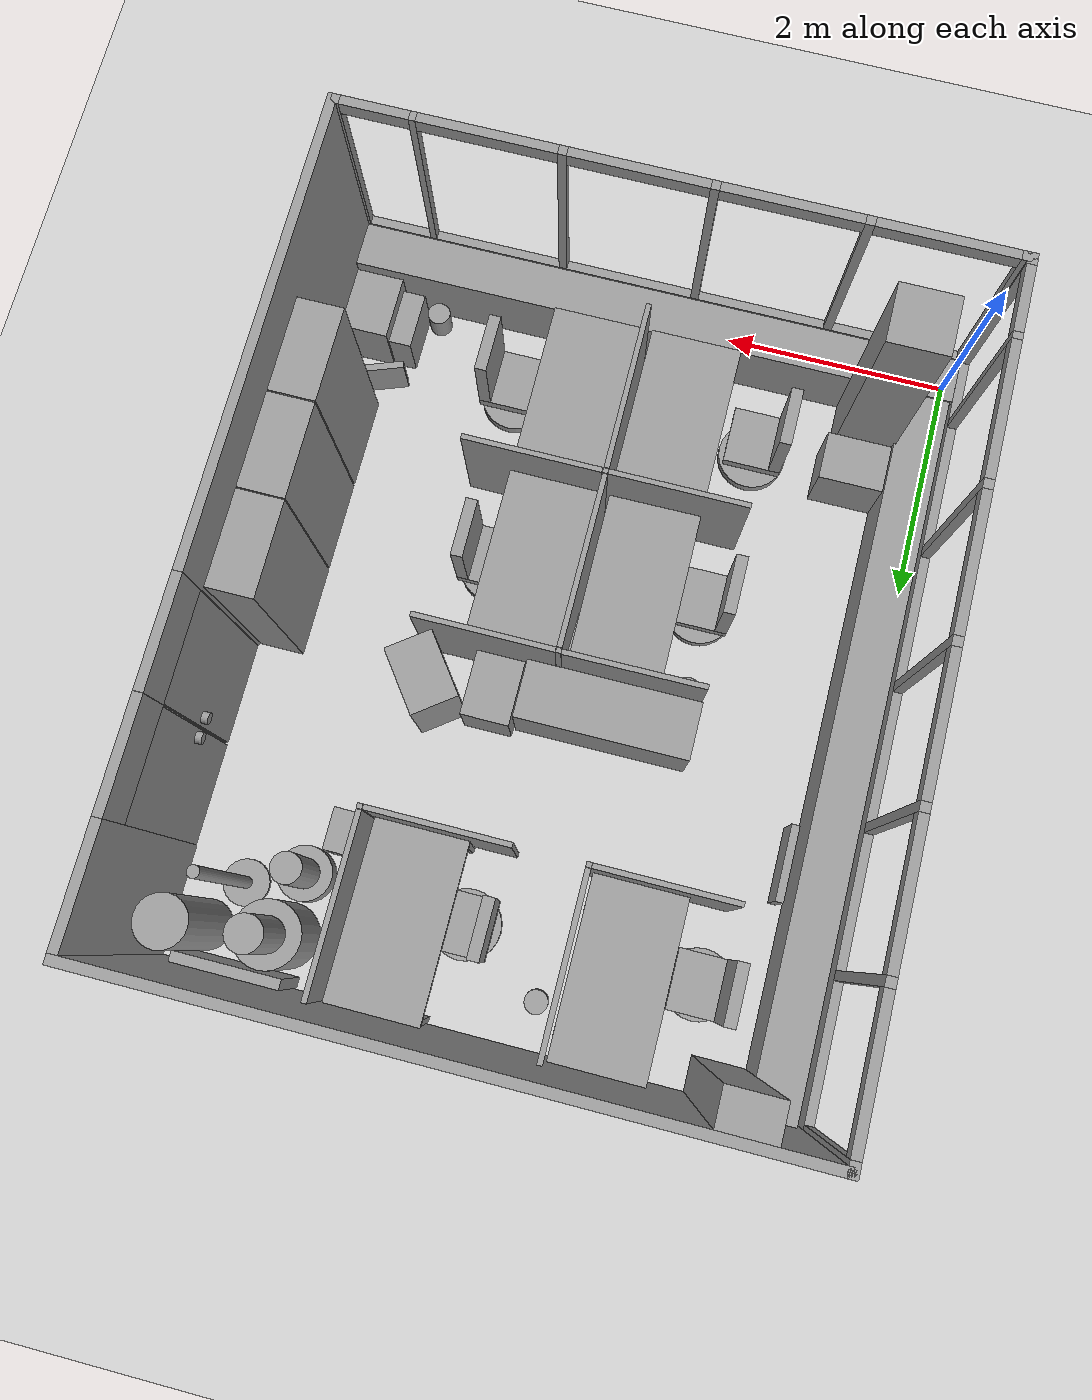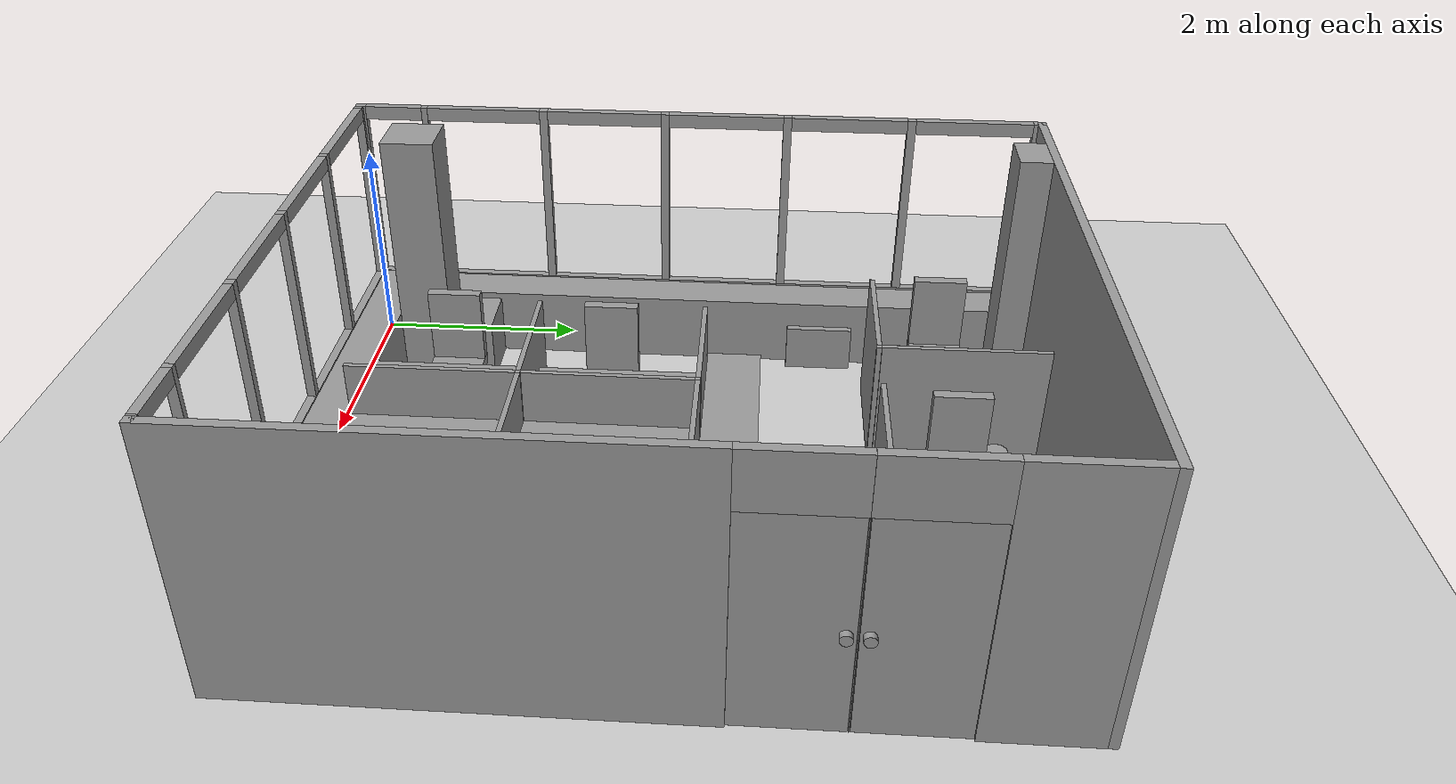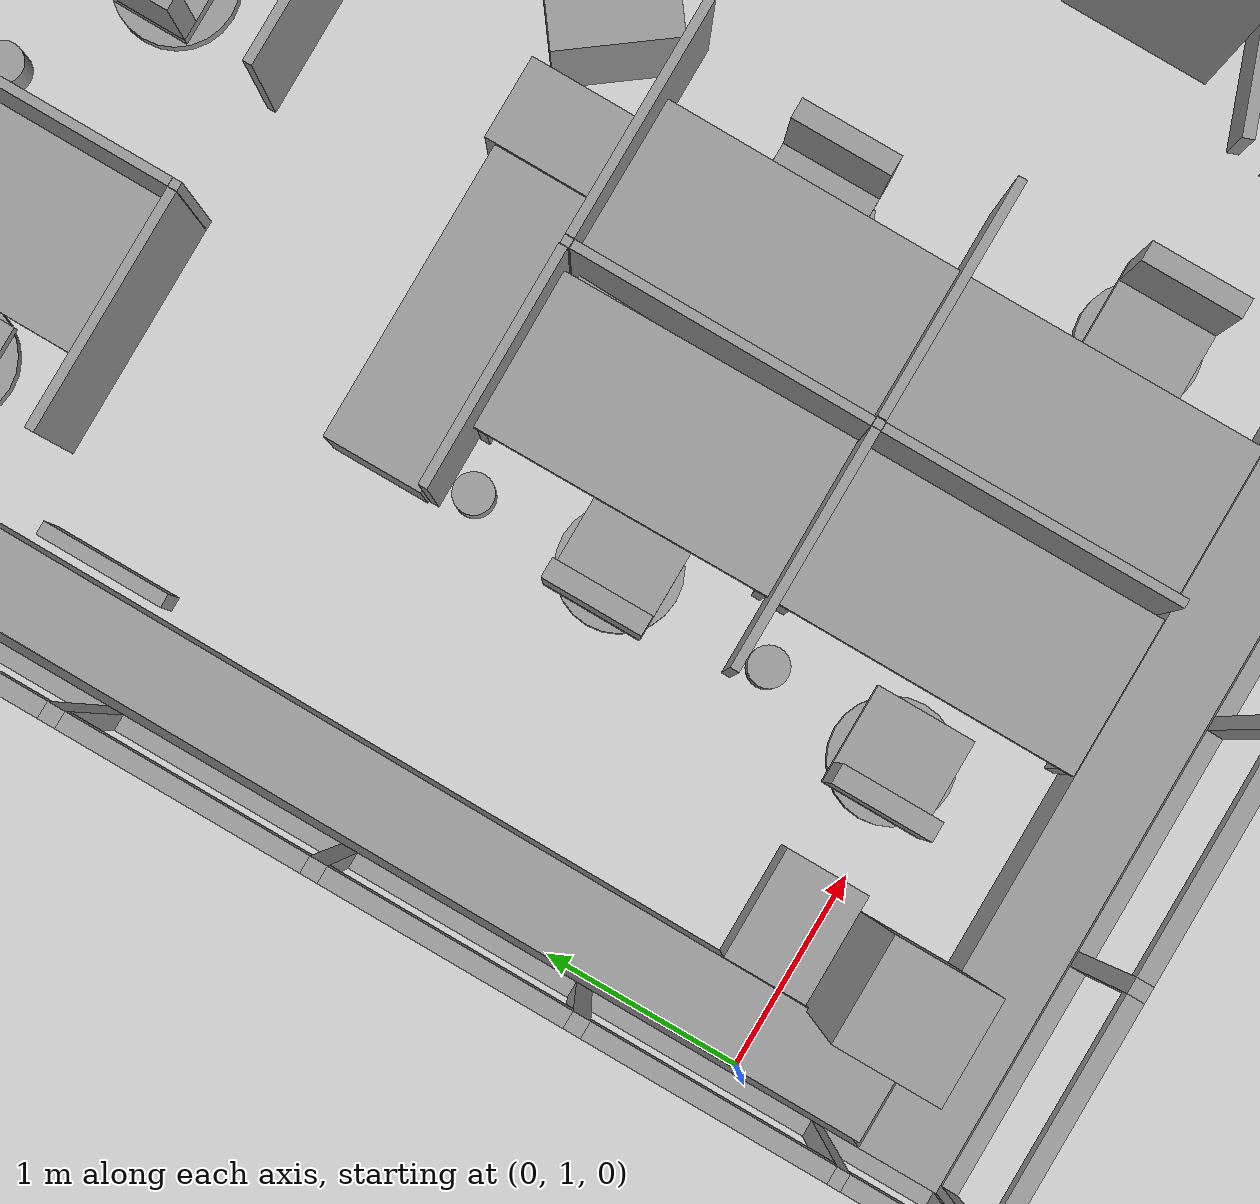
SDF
<sdf version="1.6">
 <world name="default">
  <light name="sun" type="directional">
   <pose>0 0 10 0 -0 0</pose>
   <diffuse>0.8 0.8 0.8 1</diffuse>
   <specular>0.1 0.1 0.1 1</specular>
   <attenuation>
    <range>1000</range>
    <constant>0.9</constant>
    <linear>0.01</linear>
    <quadratic>0.001</quadratic>
   </attenuation>
   <direction>-0.5 0.5 -1</direction>
  </light>
  <model name="ground_plane">
   <static>1</static>
   <link name="link">
    <collision name="collision">
     <geometry><plane><normal>0 0 1</normal><size>100 100</size></plane></geometry>
     <surface><friction><ode><mu>100</mu><mu2>50</mu2></ode></friction></surface>
    </collision>
    <visual name="visual">
     <cast_shadows>0</cast_shadows>
     <geometry><plane><normal>0 0 1</normal><size>100 100</size></plane></geometry>
     <material>
      <script><uri>file://media/materials/scripts/gazebo.material</uri><name>Gazebo/Grey</name></script>
     </material>
    </visual>
   </link>
  </model>
  <gravity>0 0 -9.8</gravity>
  <magnetic_field>6e-06 2.3e-05 -4.2e-05</magnetic_field>
  <atmosphere type="adiabatic"/>
  <physics name="default_physics" default="0" type="ode">
   <max_step_size>0.001</max_step_size>
   <real_time_factor>1</real_time_factor>
   <real_time_update_rate>1000</real_time_update_rate>
  </physics>
  <scene><ambient>0.4 0.4 0.4 1</ambient><background>0.7 0.7 0.7 1</background><shadows>1</shadows></scene>
  <spherical_coordinates>
   <surface_model>EARTH_WGS84</surface_model>
   <latitude_deg>0</latitude_deg>
   <longitude_deg>0</longitude_deg>
   <elevation>0</elevation>
   <heading_deg>0</heading_deg>
  </spherical_coordinates>
  <model name="L8401_room">
   <pose>2.69658 3.29747 0 0 -0 0</pose>
   <link name="Wall_10">
    <pose>2.74 0 0 0 -0 1.5708</pose>
    <visual name="Wall_10_Visual_0">
     <pose>-1.41 0 1.25 0 -0 0</pose>
     <geometry><box><size>3.94 0.08 2.5</size></box></geometry>
     <material>
      <script><uri>file://media/materials/scripts/gazebo.material</uri><name>Gazebo/Grey</name></script>
      <ambient>1 1 1 1</ambient>
     </material>
    </visual>
    <collision name="Wall_10_Collision_0">
     <geometry><box><size>3.94 0.08 2.5</size></box></geometry>
     <pose>-1.41 0 1.25 0 -0 0</pose>
    </collision>
    <visual name="Wall_10_Visual_1">
     <pose>1.46 0 1.25 0 -0 0</pose>
     <geometry><box><size>0.001 0.08 2.5</size></box></geometry>
     <material>
      <script><uri>file://media/materials/scripts/gazebo.material</uri><name>Gazebo/Grey</name></script>
      <ambient>1 1 1 1</ambient>
     </material>
    </visual>
    <collision name="Wall_10_Collision_1">
     <geometry><box><size>0.001 0.08 2.5</size></box></geometry>
     <pose>1.46 0 1.25 0 -0 0</pose>
    </collision>
    <visual name="Wall_10_Visual_2">
     <pose>2.87 0 1.25 0 -0 0</pose>
     <geometry><box><size>1.02 0.08 2.5</size></box></geometry>
     <material>
      <script><uri>file://media/materials/scripts/gazebo.material</uri><name>Gazebo/Grey</name></script>
      <ambient>1 1 1 1</ambient>
     </material>
    </visual>
    <collision name="Wall_10_Collision_2">
     <geometry><box><size>1.02 0.08 2.5</size></box></geometry>
     <pose>2.87 0 1.25 0 -0 0</pose>
    </collision>
    <visual name="Wall_10_Visual_3">
     <pose>1.01 0 2.25 0 -0 0</pose>
     <geometry><box><size>0.9 0.08 0.5</size></box></geometry>
     <material>
      <script><uri>file://media/materials/scripts/gazebo.material</uri><name>Gazebo/Grey</name></script>
      <ambient>1 1 1 1</ambient>
     </material>
    </visual>
    <collision name="Wall_10_Collision_3">
     <geometry><box><size>0.9 0.08 0.5</size></box></geometry>
     <pose>1.01 0 2.25 0 -0 0</pose>
    </collision>
    <visual name="Wall_10_Visual_4">
     <pose>1.91 0 2.25 0 -0 0</pose>
     <geometry><box><size>0.9 0.08 0.5</size></box></geometry>
     <material>
      <script><uri>file://media/materials/scripts/gazebo.material</uri><name>Gazebo/Grey</name></script>
      <ambient>1 1 1 1</ambient>
     </material>
    </visual>
    <collision name="Wall_10_Collision_4">
     <geometry><box><size>0.9 0.08 0.5</size></box></geometry>
     <pose>1.91 0 2.25 0 -0 0</pose>
    </collision>
   </link>
   <link name="Wall_12">
    <collision name="Wall_12_Collision">
     <geometry><box><size>5.56 0.08 2.5</size></box></geometry>
     <pose>0 0 1.25 0 -0 0</pose>
    </collision>
    <visual name="Wall_12_Visual">
     <pose>0 0 1.25 0 -0 0</pose>
     <geometry><box><size>5.56 0.08 2.5</size></box></geometry>
     <material>
      <script><uri>file://media/materials/scripts/gazebo.material</uri><name>Gazebo/Grey</name></script>
      <ambient>1 1 1 1</ambient>
     </material>
    </visual>
    <pose>0 3.34 0 0 -0 0</pose>
   </link>
   <link name="Wall_22">
    <collision name="Wall_22_Collision">
     <geometry><box><size>0.5 0.5 2.5</size></box></geometry>
     <pose>0 0 1.25 0 -0 0</pose>
    </collision>
    <visual name="Wall_22_Visual">
     <pose>0 0 1.25 0 -0 0</pose>
     <geometry><box><size>0.5 0.5 2.5</size></box></geometry>
     <material>
      <script><uri>file://media/materials/scripts/gazebo.material</uri><name>Gazebo/Grey</name></script>
      <ambient>1 1 1 1</ambient>
     </material>
    </visual>
    <pose>-2.05 -2.65 0 0 -0 0</pose>
   </link>
   <link name="Wall_24">
    <collision name="Wall_24_Collision">
     <geometry><box><size>0.45 0.3 2.5</size></box></geometry>
     <pose>0 0 1.25 0 -0 0</pose>
    </collision>
    <visual name="Wall_24_Visual">
     <pose>0 0 1.25 0 -0 0</pose>
     <geometry><box><size>0.45 0.3 2.5</size></box></geometry>
     <material>
      <script><uri>file://media/materials/scripts/gazebo.material</uri><name>Gazebo/Grey</name></script>
      <ambient>1 1 1 1</ambient>
     </material>
    </visual>
    <pose>-2.025 3.15 0 0 -0 0</pose>
   </link>
   <link name="Wall_4">
    <pose>0 -3.34 0 0 -0 0</pose>
    <visual name="Wall_4_Visual_0">
     <pose>-2.72 0 1.25 0 -0 0</pose>
     <geometry><box><size>0.12 0.08 2.5</size></box></geometry>
     <material>
      <script><uri>file://media/materials/scripts/gazebo.material</uri><name>Gazebo/Grey</name></script>
      <ambient>1 1 1 1</ambient>
     </material>
    </visual>
    <collision name="Wall_4_Collision_0">
     <geometry><box><size>0.12 0.08 2.5</size></box></geometry>
     <pose>-2.72 0 1.25 0 -0 0</pose>
    </collision>
    <visual name="Wall_4_Visual_1">
     <pose>0.06 0 0.335 0 -0 0</pose>
     <geometry><box><size>5.44 0.08 0.67</size></box></geometry>
     <material>
      <script><uri>file://media/materials/scripts/gazebo.material</uri><name>Gazebo/Grey</name></script>
      <ambient>1 1 1 1</ambient>
     </material>
    </visual>
    <collision name="Wall_4_Collision_1">
     <geometry><box><size>5.44 0.08 0.67</size></box></geometry>
     <pose>0.06 0 0.335 0 -0 0</pose>
    </collision>
    <visual name="Wall_4_Visual_2">
     <pose>-1.5025 0 1.585 0 -0 0</pose>
     <geometry><box><size>0.075 0.08 1.83</size></box></geometry>
     <material>
      <script><uri>file://media/materials/scripts/gazebo.material</uri><name>Gazebo/Grey</name></script>
      <ambient>1 1 1 1</ambient>
     </material>
    </visual>
    <collision name="Wall_4_Collision_2">
     <geometry><box><size>0.075 0.08 1.83</size></box></geometry>
     <pose>-1.5025 0 1.585 0 -0 0</pose>
    </collision>
    <visual name="Wall_4_Visual_3">
     <pose>-0.3 0 1.585 0 -0 0</pose>
     <geometry><box><size>0.07 0.08 1.83</size></box></geometry>
     <material>
      <script><uri>file://media/materials/scripts/gazebo.material</uri><name>Gazebo/Grey</name></script>
      <ambient>1 1 1 1</ambient>
     </material>
    </visual>
    <collision name="Wall_4_Collision_3">
     <geometry><box><size>0.07 0.08 1.83</size></box></geometry>
     <pose>-0.3 0 1.585 0 -0 0</pose>
    </collision>
    <visual name="Wall_4_Visual_4">
     <pose>0.900568 0 1.585 0 -0 0</pose>
     <geometry><box><size>0.071135 0.08 1.83</size></box></geometry>
     <material>
      <script><uri>file://media/materials/scripts/gazebo.material</uri><name>Gazebo/Grey</name></script>
      <ambient>1 1 1 1</ambient>
     </material>
    </visual>
    <collision name="Wall_4_Collision_4">
     <geometry><box><size>0.071135 0.08 1.83</size></box></geometry>
     <pose>0.900568 0 1.585 0 -0 0</pose>
    </collision>
    <visual name="Wall_4_Visual_5">
     <pose>2.09307 0 1.585 0 -0 0</pose>
     <geometry><box><size>0.053865 0.08 1.83</size></box></geometry>
     <material>
      <script><uri>file://media/materials/scripts/gazebo.material</uri><name>Gazebo/Grey</name></script>
      <ambient>1 1 1 1</ambient>
     </material>
    </visual>
    <collision name="Wall_4_Collision_5">
     <geometry><box><size>0.053865 0.08 1.83</size></box></geometry>
     <pose>2.09307 0 1.585 0 -0 0</pose>
    </collision>
    <visual name="Wall_4_Visual_6">
     <pose>2.73 0 1.585 0 -0 0</pose>
     <geometry><box><size>0.1 0.08 1.83</size></box></geometry>
     <material>
      <script><uri>file://media/materials/scripts/gazebo.material</uri><name>Gazebo/Grey</name></script>
      <ambient>1 1 1 1</ambient>
     </material>
    </visual>
    <collision name="Wall_4_Collision_6">
     <geometry><box><size>0.1 0.08 1.83</size></box></geometry>
     <pose>2.73 0 1.585 0 -0 0</pose>
    </collision>
    <visual name="Wall_4_Visual_7">
     <pose>-0.9 0 0.67 0 -0 0</pose>
     <geometry><box><size>1.13 0.08 0.001</size></box></geometry>
     <material>
      <script><uri>file://media/materials/scripts/gazebo.material</uri><name>Gazebo/Grey</name></script>
      <ambient>1 1 1 1</ambient>
     </material>
    </visual>
    <collision name="Wall_4_Collision_7">
     <geometry><box><size>1.13 0.08 0.001</size></box></geometry>
     <pose>-0.9 0 0.67 0 -0 0</pose>
    </collision>
    <visual name="Wall_4_Visual_8">
     <pose>0.3 0 0.67 0 -0 0</pose>
     <geometry><box><size>1.13 0.08 0.001</size></box></geometry>
     <material>
      <script><uri>file://media/materials/scripts/gazebo.material</uri><name>Gazebo/Grey</name></script>
      <ambient>1 1 1 1</ambient>
     </material>
    </visual>
    <collision name="Wall_4_Collision_8">
     <geometry><box><size>1.13 0.08 0.001</size></box></geometry>
     <pose>0.3 0 0.67 0 -0 0</pose>
    </collision>
    <visual name="Wall_4_Visual_9">
     <pose>1.50114 0 0.67 0 -0 0</pose>
     <geometry><box><size>1.13 0.08 0.001</size></box></geometry>
     <material>
      <script><uri>file://media/materials/scripts/gazebo.material</uri><name>Gazebo/Grey</name></script>
      <ambient>1 1 1 1</ambient>
     </material>
    </visual>
    <collision name="Wall_4_Collision_9">
     <geometry><box><size>1.13 0.08 0.001</size></box></geometry>
     <pose>1.50114 0 0.67 0 -0 0</pose>
    </collision>
    <visual name="Wall_4_Visual_10">
     <pose>2.4 0 0.67 0 -0 0</pose>
     <geometry><box><size>0.56 0.08 0.001</size></box></geometry>
     <material>
      <script><uri>file://media/materials/scripts/gazebo.material</uri><name>Gazebo/Grey</name></script>
      <ambient>1 1 1 1</ambient>
     </material>
    </visual>
    <collision name="Wall_4_Collision_10">
     <geometry><box><size>0.56 0.08 0.001</size></box></geometry>
     <pose>2.4 0 0.67 0 -0 0</pose>
    </collision>
    <visual name="Wall_4_Visual_11">
     <pose>-2.1 0 2.435 0 -0 0</pose>
     <geometry><box><size>1.12 0.08 0.13</size></box></geometry>
     <material>
      <script><uri>file://media/materials/scripts/gazebo.material</uri><name>Gazebo/Grey</name></script>
      <ambient>1 1 1 1</ambient>
     </material>
    </visual>
    <collision name="Wall_4_Collision_11">
     <geometry><box><size>1.12 0.08 0.13</size></box></geometry>
     <pose>-2.1 0 2.435 0 -0 0</pose>
    </collision>
    <visual name="Wall_4_Visual_12">
     <pose>-0.9 0 2.435 0 -0 0</pose>
     <geometry><box><size>1.13 0.08 0.13</size></box></geometry>
     <material>
      <script><uri>file://media/materials/scripts/gazebo.material</uri><name>Gazebo/Grey</name></script>
      <ambient>1 1 1 1</ambient>
     </material>
    </visual>
    <collision name="Wall_4_Collision_12">
     <geometry><box><size>1.13 0.08 0.13</size></box></geometry>
     <pose>-0.9 0 2.435 0 -0 0</pose>
    </collision>
    <visual name="Wall_4_Visual_13">
     <pose>0.3 0 2.435 0 -0 0</pose>
     <geometry><box><size>1.13 0.08 0.13</size></box></geometry>
     <material>
      <script><uri>file://media/materials/scripts/gazebo.material</uri><name>Gazebo/Grey</name></script>
      <ambient>1 1 1 1</ambient>
     </material>
    </visual>
    <collision name="Wall_4_Collision_13">
     <geometry><box><size>1.13 0.08 0.13</size></box></geometry>
     <pose>0.3 0 2.435 0 -0 0</pose>
    </collision>
    <visual name="Wall_4_Visual_14">
     <pose>1.50114 0 2.435 0 -0 0</pose>
     <geometry><box><size>1.13 0.08 0.13</size></box></geometry>
     <material>
      <script><uri>file://media/materials/scripts/gazebo.material</uri><name>Gazebo/Grey</name></script>
      <ambient>1 1 1 1</ambient>
     </material>
    </visual>
    <collision name="Wall_4_Collision_14">
     <geometry><box><size>1.13 0.08 0.13</size></box></geometry>
     <pose>1.50114 0 2.435 0 -0 0</pose>
    </collision>
    <visual name="Wall_4_Visual_15">
     <pose>2.4 0 2.435 0 -0 0</pose>
     <geometry><box><size>0.56 0.08 0.13</size></box></geometry>
     <material>
      <script><uri>file://media/materials/scripts/gazebo.material</uri><name>Gazebo/Grey</name></script>
      <ambient>1 1 1 1</ambient>
     </material>
    </visual>
    <collision name="Wall_4_Collision_15">
     <geometry><box><size>0.56 0.08 0.13</size></box></geometry>
     <pose>2.4 0 2.435 0 -0 0</pose>
    </collision>
   </link>
   <link name="Wall_6">
    <pose>-2.74 0 0 0 -0 1.5708</pose>
    <visual name="Wall_6_Visual_0">
     <pose>-3.33 0 1.25 0 -0 0</pose>
     <geometry><box><size>0.1 0.08 2.5</size></box></geometry>
     <material>
      <script><uri>file://media/materials/scripts/gazebo.material</uri><name>Gazebo/Grey</name></script>
      <ambient>1 1 1 1</ambient>
     </material>
    </visual>
    <collision name="Wall_6_Collision_0">
     <geometry><box><size>0.1 0.08 2.5</size></box></geometry>
     <pose>-3.33 0 1.25 0 -0 0</pose>
    </collision>
    <visual name="Wall_6_Visual_1">
     <pose>0.05 0 0.335 0 -0 0</pose>
     <geometry><box><size>6.66 0.08 0.67</size></box></geometry>
     <material>
      <script><uri>file://media/materials/scripts/gazebo.material</uri><name>Gazebo/Grey</name></script>
      <ambient>1 1 1 1</ambient>
     </material>
    </visual>
    <collision name="Wall_6_Collision_1">
     <geometry><box><size>6.66 0.08 0.67</size></box></geometry>
     <pose>0.05 0 0.335 0 -0 0</pose>
    </collision>
    <visual name="Wall_6_Visual_2">
     <pose>-2.69 0 1.585 0 -0 0</pose>
     <geometry><box><size>0.06 0.08 1.83</size></box></geometry>
     <material>
      <script><uri>file://media/materials/scripts/gazebo.material</uri><name>Gazebo/Grey</name></script>
      <ambient>1 1 1 1</ambient>
     </material>
    </visual>
    <collision name="Wall_6_Collision_2">
     <geometry><box><size>0.06 0.08 1.83</size></box></geometry>
     <pose>-2.69 0 1.585 0 -0 0</pose>
    </collision>
    <visual name="Wall_6_Visual_3">
     <pose>-1.5 0 1.585 0 -0 0</pose>
     <geometry><box><size>0.08 0.08 1.83</size></box></geometry>
     <material>
      <script><uri>file://media/materials/scripts/gazebo.material</uri><name>Gazebo/Grey</name></script>
      <ambient>1 1 1 1</ambient>
     </material>
    </visual>
    <collision name="Wall_6_Collision_3">
     <geometry><box><size>0.08 0.08 1.83</size></box></geometry>
     <pose>-1.5 0 1.585 0 -0 0</pose>
    </collision>
    <visual name="Wall_6_Visual_4">
     <pose>-0.3 0 1.585 0 -0 0</pose>
     <geometry><box><size>0.08 0.08 1.83</size></box></geometry>
     <material>
      <script><uri>file://media/materials/scripts/gazebo.material</uri><name>Gazebo/Grey</name></script>
      <ambient>1 1 1 1</ambient>
     </material>
    </visual>
    <collision name="Wall_6_Collision_4">
     <geometry><box><size>0.08 0.08 1.83</size></box></geometry>
     <pose>-0.3 0 1.585 0 -0 0</pose>
    </collision>
    <visual name="Wall_6_Visual_5">
     <pose>0.9 0 1.585 0 -0 0</pose>
     <geometry><box><size>0.08 0.08 1.83</size></box></geometry>
     <material>
      <script><uri>file://media/materials/scripts/gazebo.material</uri><name>Gazebo/Grey</name></script>
      <ambient>1 1 1 1</ambient>
     </material>
    </visual>
    <collision name="Wall_6_Collision_5">
     <geometry><box><size>0.08 0.08 1.83</size></box></geometry>
     <pose>0.9 0 1.585 0 -0 0</pose>
    </collision>
    <visual name="Wall_6_Visual_6">
     <pose>2.1 0 1.585 0 -0 0</pose>
     <geometry><box><size>0.08 0.08 1.83</size></box></geometry>
     <material>
      <script><uri>file://media/materials/scripts/gazebo.material</uri><name>Gazebo/Grey</name></script>
      <ambient>1 1 1 1</ambient>
     </material>
    </visual>
    <collision name="Wall_6_Collision_6">
     <geometry><box><size>0.08 0.08 1.83</size></box></geometry>
     <pose>2.1 0 1.585 0 -0 0</pose>
    </collision>
    <visual name="Wall_6_Visual_7">
     <pose>3.32 0 1.585 0 -0 0</pose>
     <geometry><box><size>0.12 0.08 1.83</size></box></geometry>
     <material>
      <script><uri>file://media/materials/scripts/gazebo.material</uri><name>Gazebo/Grey</name></script>
      <ambient>1 1 1 1</ambient>
     </material>
    </visual>
    <collision name="Wall_6_Collision_7">
     <geometry><box><size>0.12 0.08 1.83</size></box></geometry>
     <pose>3.32 0 1.585 0 -0 0</pose>
    </collision>
    <visual name="Wall_6_Visual_8">
     <pose>-3 0 2.435 0 -0 0</pose>
     <geometry><box><size>0.56 0.08 0.13</size></box></geometry>
     <material>
      <script><uri>file://media/materials/scripts/gazebo.material</uri><name>Gazebo/Grey</name></script>
      <ambient>1 1 1 1</ambient>
     </material>
    </visual>
    <collision name="Wall_6_Collision_8">
     <geometry><box><size>0.56 0.08 0.13</size></box></geometry>
     <pose>-3 0 2.435 0 -0 0</pose>
    </collision>
    <visual name="Wall_6_Visual_9">
     <pose>-2.1 0 2.435 0 -0 0</pose>
     <geometry><box><size>1.12 0.08 0.13</size></box></geometry>
     <material>
      <script><uri>file://media/materials/scripts/gazebo.material</uri><name>Gazebo/Grey</name></script>
      <ambient>1 1 1 1</ambient>
     </material>
    </visual>
    <collision name="Wall_6_Collision_9">
     <geometry><box><size>1.12 0.08 0.13</size></box></geometry>
     <pose>-2.1 0 2.435 0 -0 0</pose>
    </collision>
    <visual name="Wall_6_Visual_10">
     <pose>-0.9 0 2.435 0 -0 0</pose>
     <geometry><box><size>1.12 0.08 0.13</size></box></geometry>
     <material>
      <script><uri>file://media/materials/scripts/gazebo.material</uri><name>Gazebo/Grey</name></script>
      <ambient>1 1 1 1</ambient>
     </material>
    </visual>
    <collision name="Wall_6_Collision_10">
     <geometry><box><size>1.12 0.08 0.13</size></box></geometry>
     <pose>-0.9 0 2.435 0 -0 0</pose>
    </collision>
    <visual name="Wall_6_Visual_11">
     <pose>0.3 0 2.435 0 -0 0</pose>
     <geometry><box><size>1.12 0.08 0.13</size></box></geometry>
     <material>
      <script><uri>file://media/materials/scripts/gazebo.material</uri><name>Gazebo/Grey</name></script>
      <ambient>1 1 1 1</ambient>
     </material>
    </visual>
    <collision name="Wall_6_Collision_11">
     <geometry><box><size>1.12 0.08 0.13</size></box></geometry>
     <pose>0.3 0 2.435 0 -0 0</pose>
    </collision>
    <visual name="Wall_6_Visual_12">
     <pose>1.5 0 2.435 0 -0 0</pose>
     <geometry><box><size>1.12 0.08 0.13</size></box></geometry>
     <material>
      <script><uri>file://media/materials/scripts/gazebo.material</uri><name>Gazebo/Grey</name></script>
      <ambient>1 1 1 1</ambient>
     </material>
    </visual>
    <collision name="Wall_6_Collision_12">
     <geometry><box><size>1.12 0.08 0.13</size></box></geometry>
     <pose>1.5 0 2.435 0 -0 0</pose>
    </collision>
    <visual name="Wall_6_Visual_13">
     <pose>2.7 0 2.435 0 -0 0</pose>
     <geometry><box><size>1.12 0.08 0.13</size></box></geometry>
     <material>
      <script><uri>file://media/materials/scripts/gazebo.material</uri><name>Gazebo/Grey</name></script>
      <ambient>1 1 1 1</ambient>
     </material>
    </visual>
    <collision name="Wall_6_Collision_13">
     <geometry><box><size>1.12 0.08 0.13</size></box></geometry>
     <pose>2.7 0 2.435 0 -0 0</pose>
    </collision>
   </link>
   <static>1</static>
  </model>
  <model name="L8401_mounted_heater">
   <link name="link_1">
    <pose>1.23386 -1.6503 -0.000337 0 -0 0</pose>
    <inertial>
     <mass>1.40657</mass>
     <inertia>
      <ixx>0.0695898</ixx>
      <ixy>0</ixy>
      <ixz>0</ixz>
      <iyy>3.47219</iyy>
      <iyz>0</iyz>
      <izz>3.43877</izz>
     </inertia>
    </inertial>
    <visual name="visual">
     <geometry><box><size>5.40211 0.392756 0.662878</size></box></geometry>
     <material>
      <lighting>1</lighting>
      <script><uri>file://media/materials/scripts/gazebo.material</uri><name>Gazebo/Grey</name></script>
      <ambient>0.3 0.3 0.3 1</ambient>
      <diffuse>0.7 0.7 0.7 1</diffuse>
      <specular>0.01 0.01 0.01 1</specular>
      <emissive>0 0 0 1</emissive>
      <shader type="vertex"><normal_map>__default__</normal_map></shader>
     </material>
    </visual>
    <collision name="collision">
     <geometry><box><size>5.40211 0.392756 0.662878</size></box></geometry>
     <surface>
      <friction>
       <ode><mu>1</mu><mu2>1</mu2><fdir1>0 0 0</fdir1><slip1>0</slip1><slip2>0</slip2></ode>
       <torsional>
        <coefficient>1</coefficient>
        <patch_radius>0</patch_radius>
        <surface_radius>0</surface_radius>
        <use_patch_radius>1</use_patch_radius>
        <ode><slip>0</slip></ode>
       </torsional>
      </friction>
      <bounce><restitution_coefficient>0</restitution_coefficient><threshold>1e+06</threshold></bounce>
      <contact>
       <collide_without_contact>0</collide_without_contact>
       <collide_without_contact_bitmask>1</collide_without_contact_bitmask>
       <collide_bitmask>1</collide_bitmask>
       <ode>
        <soft_cfm>0</soft_cfm>
        <soft_erp>0.2</soft_erp>
        <kp>1e+13</kp>
        <kd>1</kd>
        <max_vel>0.01</max_vel>
        <min_depth>0</min_depth>
       </ode>
       <bullet>
        <split_impulse>1</split_impulse>
        <split_impulse_penetration_threshold>-0.01</split_impulse_penetration_threshold>
        <soft_cfm>0</soft_cfm>
        <soft_erp>0.2</soft_erp>
        <kp>1e+13</kp>
        <kd>1</kd>
       </bullet>
      </contact>
     </surface>
    </collision>
   </link>
   <link name="link_1_clone">
    <pose>-1.23386 1.6503 0.000337 0 0 -1.57467</pose>
    <inertial>
     <mass>1.62191</mass>
     <inertia>
      <ixx>0.0809796</ixx>
      <ixy>0</ixy>
      <ixz>0</ixz>
      <iyy>5.24067</iyy>
      <iyz>0</iyz>
      <izz>5.20139</izz>
     </inertia>
    </inertial>
    <visual name="visual">
     <geometry><box><size>6.19103 0.392756 0.666978</size></box></geometry>
     <material>
      <lighting>1</lighting>
      <script><uri>file://media/materials/scripts/gazebo.material</uri><name>Gazebo/Grey</name></script>
      <ambient>0.3 0.3 0.3 1</ambient>
      <diffuse>0.7 0.7 0.7 1</diffuse>
      <specular>0.01 0.01 0.01 1</specular>
      <emissive>0 0 0 1</emissive>
      <shader type="vertex"><normal_map>__default__</normal_map></shader>
     </material>
    </visual>
    <collision name="collision">
     <geometry><box><size>6.19103 0.392756 0.666978</size></box></geometry>
     <surface>
      <friction>
       <ode><mu>1</mu><mu2>1</mu2><fdir1>0 0 0</fdir1><slip1>0</slip1><slip2>0</slip2></ode>
       <torsional>
        <coefficient>1</coefficient>
        <patch_radius>0</patch_radius>
        <surface_radius>0</surface_radius>
        <use_patch_radius>1</use_patch_radius>
        <ode><slip>0</slip></ode>
       </torsional>
      </friction>
      <bounce><restitution_coefficient>0</restitution_coefficient><threshold>1e+06</threshold></bounce>
      <contact>
       <collide_without_contact>0</collide_without_contact>
       <collide_without_contact_bitmask>1</collide_without_contact_bitmask>
       <collide_bitmask>1</collide_bitmask>
       <ode>
        <soft_cfm>0</soft_cfm>
        <soft_erp>0.2</soft_erp>
        <kp>1e+13</kp>
        <kd>1</kd>
        <max_vel>0.01</max_vel>
        <min_depth>0</min_depth>
       </ode>
       <bullet>
        <split_impulse>1</split_impulse>
        <split_impulse_penetration_threshold>-0.01</split_impulse_penetration_threshold>
        <soft_cfm>0</soft_cfm>
        <soft_erp>0.2</soft_erp>
        <kp>1e+13</kp>
        <kd>1</kd>
       </bullet>
      </contact>
     </surface>
    </collision>
   </link>
   <static>1</static>
   <pose>1.46087 1.8518 0.337569 1e-05 -4.1e-05 -5.2e-05</pose>
  </model>
  <model name="L8401_cabinet_1">
   <link name="link">
    <inertial>
     <mass>1</mass>
     <inertia>
      <ixx>0.166667</ixx>
      <ixy>0</ixy>
      <ixz>0</ixz>
      <iyy>0.166667</iyy>
      <iyz>0</iyz>
      <izz>0.166667</izz>
     </inertia>
    </inertial>
    <visual name="visual">
     <geometry><box><size>0.39 0.8 2</size></box></geometry>
     <material>
      <script><name>Gazebo/Grey</name><uri>file://media/materials/scripts/gazebo.material</uri></script>
      <ambient>0.3 0.3 0.3 1</ambient>
      <diffuse>0.7 0.7 0.7 1</diffuse>
      <specular>0.01 0.01 0.01 1</specular>
      <emissive>0 0 0 1</emissive>
      <shader type="vertex"><normal_map>__default__</normal_map></shader>
     </material>
    </visual>
    <collision name="collision">
     <geometry><box><size>0.39 0.8 2</size></box></geometry>
     <surface>
      <friction>
       <ode><mu>1</mu><mu2>1</mu2><fdir1>0 0 0</fdir1><slip1>0</slip1><slip2>0</slip2></ode>
       <torsional>
        <coefficient>1</coefficient>
        <patch_radius>0</patch_radius>
        <surface_radius>0</surface_radius>
        <use_patch_radius>1</use_patch_radius>
        <ode><slip>0</slip></ode>
       </torsional>
      </friction>
      <bounce><restitution_coefficient>0</restitution_coefficient><threshold>1e+06</threshold></bounce>
      <contact>
       <collide_without_contact>0</collide_without_contact>
       <collide_without_contact_bitmask>1</collide_without_contact_bitmask>
       <collide_bitmask>1</collide_bitmask>
       <ode>
        <soft_cfm>0</soft_cfm>
        <soft_erp>0.2</soft_erp>
        <kp>1e+13</kp>
        <kd>1</kd>
        <max_vel>0.01</max_vel>
        <min_depth>0</min_depth>
       </ode>
       <bullet>
        <split_impulse>1</split_impulse>
        <split_impulse_penetration_threshold>-0.01</split_impulse_penetration_threshold>
        <soft_cfm>0</soft_cfm>
        <soft_erp>0.2</soft_erp>
        <kp>1e+13</kp>
        <kd>1</kd>
       </bullet>
      </contact>
     </surface>
    </collision>
   </link>
   <static>1</static>
   <pose>5.18748 3.43007 0.999999 -1e-06 1e-06 3.8e-05</pose>
  </model>
  <model name="L8401_cabinet_1_clone">
   <link name="link">
    <inertial>
     <mass>1</mass>
     <inertia>
      <ixx>0.166667</ixx>
      <ixy>0</ixy>
      <ixz>0</ixz>
      <iyy>0.166667</iyy>
      <iyz>0</iyz>
      <izz>0.166667</izz>
     </inertia>
    </inertial>
    <visual name="visual">
     <geometry><box><size>0.39 0.8 2</size></box></geometry>
     <material>
      <script><name>Gazebo/Grey</name><uri>file://media/materials/scripts/gazebo.material</uri></script>
      <ambient>0.3 0.3 0.3 1</ambient>
      <diffuse>0.7 0.7 0.7 1</diffuse>
      <specular>0.01 0.01 0.01 1</specular>
      <emissive>0 0 0 1</emissive>
      <shader type="vertex"><normal_map>__default__</normal_map></shader>
     </material>
    </visual>
    <collision name="collision">
     <geometry><box><size>0.39 0.8 2</size></box></geometry>
     <surface>
      <friction>
       <ode><mu>1</mu><mu2>1</mu2><fdir1>0 0 0</fdir1><slip1>0</slip1><slip2>0</slip2></ode>
       <torsional>
        <coefficient>1</coefficient>
        <patch_radius>0</patch_radius>
        <surface_radius>0</surface_radius>
        <use_patch_radius>1</use_patch_radius>
        <ode><slip>0</slip></ode>
       </torsional>
      </friction>
      <bounce><restitution_coefficient>0</restitution_coefficient><threshold>1e+06</threshold></bounce>
      <contact>
       <collide_without_contact>0</collide_without_contact>
       <collide_without_contact_bitmask>1</collide_without_contact_bitmask>
       <collide_bitmask>1</collide_bitmask>
       <ode>
        <soft_cfm>0</soft_cfm>
        <soft_erp>0.2</soft_erp>
        <kp>1e+13</kp>
        <kd>1</kd>
        <max_vel>0.01</max_vel>
        <min_depth>0</min_depth>
       </ode>
       <bullet>
        <split_impulse>1</split_impulse>
        <split_impulse_penetration_threshold>-0.01</split_impulse_penetration_threshold>
        <soft_cfm>0</soft_cfm>
        <soft_erp>0.2</soft_erp>
        <kp>1e+13</kp>
        <kd>1</kd>
       </bullet>
      </contact>
     </surface>
    </collision>
   </link>
   <static>1</static>
   <pose>5.18824 2.62085 0.999999 3e-06 -0 0.00016</pose>
  </model>
  <model name="L8401_cabinet_1_clone_0">
   <link name="link">
    <inertial>
     <mass>1</mass>
     <inertia>
      <ixx>0.166667</ixx>
      <ixy>0</ixy>
      <ixz>0</ixz>
      <iyy>0.166667</iyy>
      <iyz>0</iyz>
      <izz>0.166667</izz>
     </inertia>
    </inertial>
    <visual name="visual">
     <geometry><box><size>0.39 0.8 2</size></box></geometry>
     <material>
      <script><name>Gazebo/Grey</name><uri>file://media/materials/scripts/gazebo.material</uri></script>
      <ambient>0.3 0.3 0.3 1</ambient>
      <diffuse>0.7 0.7 0.7 1</diffuse>
      <specular>0.01 0.01 0.01 1</specular>
      <emissive>0 0 0 1</emissive>
      <shader type="vertex"><normal_map>__default__</normal_map></shader>
     </material>
    </visual>
    <collision name="collision">
     <geometry><box><size>0.39 0.8 2</size></box></geometry>
     <surface>
      <friction>
       <ode><mu>1</mu><mu2>1</mu2><fdir1>0 0 0</fdir1><slip1>0</slip1><slip2>0</slip2></ode>
       <torsional>
        <coefficient>1</coefficient>
        <patch_radius>0</patch_radius>
        <surface_radius>0</surface_radius>
        <use_patch_radius>1</use_patch_radius>
        <ode><slip>0</slip></ode>
       </torsional>
      </friction>
      <bounce><restitution_coefficient>0</restitution_coefficient><threshold>1e+06</threshold></bounce>
      <contact>
       <collide_without_contact>0</collide_without_contact>
       <collide_without_contact_bitmask>1</collide_without_contact_bitmask>
       <collide_bitmask>1</collide_bitmask>
       <ode>
        <soft_cfm>0</soft_cfm>
        <soft_erp>0.2</soft_erp>
        <kp>1e+13</kp>
        <kd>1</kd>
        <max_vel>0.01</max_vel>
        <min_depth>0</min_depth>
       </ode>
       <bullet>
        <split_impulse>1</split_impulse>
        <split_impulse_penetration_threshold>-0.01</split_impulse_penetration_threshold>
        <soft_cfm>0</soft_cfm>
        <soft_erp>0.2</soft_erp>
        <kp>1e+13</kp>
        <kd>1</kd>
       </bullet>
      </contact>
     </surface>
    </collision>
   </link>
   <static>1</static>
   <pose>5.18768 1.81 0.999999 1e-06 -1e-06 9e-06</pose>
  </model>
  <model name="L8401_panel_B_0">
   <link name="link_0">
    <pose>0 0 0 0 -0 1.57</pose>
    <inertial>
     <mass>1</mass>
     <inertia>
      <ixx>0.166667</ixx>
      <ixy>0</ixy>
      <ixz>0</ixz>
      <iyy>0.166667</iyy>
      <iyz>0</iyz>
      <izz>0.166667</izz>
     </inertia>
    </inertial>
    <visual name="visual">
     <geometry><box><size>1.5 0.045 1.23</size></box></geometry>
     <material>
      <lighting>1</lighting>
      <script><uri>file://media/materials/scripts/gazebo.material</uri><name>Gazebo/Grey</name></script>
      <ambient>0.3 0.3 0.3 1</ambient>
      <diffuse>0.7 0.7 0.7 1</diffuse>
      <specular>0.01 0.01 0.01 1</specular>
      <emissive>0 0 0 1</emissive>
      <shader type="vertex"><normal_map>__default__</normal_map></shader>
     </material>
    </visual>
    <collision name="collision">
     <geometry><box><size>1.5 0.045 1.23</size></box></geometry>
     <surface>
      <friction>
       <ode><mu>1</mu><mu2>1</mu2><fdir1>0 0 0</fdir1><slip1>0</slip1><slip2>0</slip2></ode>
       <torsional>
        <coefficient>1</coefficient>
        <patch_radius>0</patch_radius>
        <surface_radius>0</surface_radius>
        <use_patch_radius>1</use_patch_radius>
        <ode><slip>0</slip></ode>
       </torsional>
      </friction>
      <bounce><restitution_coefficient>0</restitution_coefficient><threshold>1e+06</threshold></bounce>
      <contact>
       <collide_without_contact>0</collide_without_contact>
       <collide_without_contact_bitmask>1</collide_without_contact_bitmask>
       <collide_bitmask>1</collide_bitmask>
       <ode>
        <soft_cfm>0</soft_cfm>
        <soft_erp>0.2</soft_erp>
        <kp>1e+13</kp>
        <kd>1</kd>
        <max_vel>0.01</max_vel>
        <min_depth>0</min_depth>
       </ode>
       <bullet>
        <split_impulse>1</split_impulse>
        <split_impulse_penetration_threshold>-0.01</split_impulse_penetration_threshold>
        <soft_cfm>0</soft_cfm>
        <soft_erp>0.2</soft_erp>
        <kp>1e+13</kp>
        <kd>1</kd>
       </bullet>
      </contact>
     </surface>
    </collision>
   </link>
   <static>1</static>
   <pose>2.73777 1.16621 0.615 0 -0 0.00224</pose>
  </model>
  <model name="L8401_desk">
   <link name="link_0">
    <pose>0.358907 -0.716347 -0.07 0 -0 3.14159</pose>
    <inertial>
     <mass>0.00540124</mass>
     <inertia>
      <ixx>0.00024509</ixx>
      <ixy>0</ixy>
      <ixz>0</ixz>
      <iyy>0.00024438</iyy>
      <iyz>0</iyz>
      <izz>6.68e-06</izz>
     </inertia>
    </inertial>
    <visual name="visual">
     <geometry><box><size>0.05 0.05 0.7</size></box></geometry>
     <material>
      <lighting>1</lighting>
      <script><uri>file://media/materials/scripts/gazebo.material</uri><name>Gazebo/Grey</name></script>
      <ambient>0.3 0.3 0.3 1</ambient>
      <diffuse>0.7 0.7 0.7 1</diffuse>
      <specular>0.01 0.01 0.01 1</specular>
      <emissive>0 0 0 1</emissive>
      <shader type="vertex"><normal_map>__default__</normal_map></shader>
     </material>
    </visual>
    <collision name="collision">
     <geometry><box><size>0.05 0.05 0.7</size></box></geometry>
     <surface>
      <friction>
       <ode><mu>1</mu><mu2>1</mu2><fdir1>0 0 0</fdir1><slip1>0</slip1><slip2>0</slip2></ode>
       <torsional>
        <coefficient>1</coefficient>
        <patch_radius>0</patch_radius>
        <surface_radius>0</surface_radius>
        <use_patch_radius>1</use_patch_radius>
        <ode><slip>0</slip></ode>
       </torsional>
      </friction>
      <bounce><restitution_coefficient>0</restitution_coefficient><threshold>1e+06</threshold></bounce>
      <contact>
       <collide_without_contact>0</collide_without_contact>
       <collide_without_contact_bitmask>1</collide_without_contact_bitmask>
       <collide_bitmask>1</collide_bitmask>
       <ode>
        <soft_cfm>0</soft_cfm>
        <soft_erp>0.2</soft_erp>
        <kp>1e+13</kp>
        <kd>1</kd>
        <max_vel>0.01</max_vel>
        <min_depth>0</min_depth>
       </ode>
       <bullet>
        <split_impulse>1</split_impulse>
        <split_impulse_penetration_threshold>-0.01</split_impulse_penetration_threshold>
        <soft_cfm>0</soft_cfm>
        <soft_erp>0.2</soft_erp>
        <kp>1e+13</kp>
        <kd>1</kd>
       </bullet>
      </contact>
     </surface>
    </collision>
   </link>
   <link name="link_0_clone">
    <pose>-0.368381 -0.716242 -0.07 0 -0 3.14159</pose>
    <inertial>
     <mass>0.00540124</mass>
     <inertia>
      <ixx>0.00024509</ixx>
      <ixy>0</ixy>
      <ixz>0</ixz>
      <iyy>0.00024438</iyy>
      <iyz>0</iyz>
      <izz>6.68e-06</izz>
     </inertia>
    </inertial>
    <visual name="visual">
     <geometry><box><size>0.05 0.05 0.7</size></box></geometry>
     <material>
      <lighting>1</lighting>
      <script><uri>file://media/materials/scripts/gazebo.material</uri><name>Gazebo/Grey</name></script>
      <ambient>0.3 0.3 0.3 1</ambient>
      <diffuse>0.7 0.7 0.7 1</diffuse>
      <specular>0.01 0.01 0.01 1</specular>
      <emissive>0 0 0 1</emissive>
      <shader type="vertex"><normal_map>__default__</normal_map></shader>
     </material>
    </visual>
    <collision name="collision">
     <geometry><box><size>0.05 0.05 0.7</size></box></geometry>
     <surface>
      <friction>
       <ode><mu>1</mu><mu2>1</mu2><fdir1>0 0 0</fdir1><slip1>0</slip1><slip2>0</slip2></ode>
       <torsional>
        <coefficient>1</coefficient>
        <patch_radius>0</patch_radius>
        <surface_radius>0</surface_radius>
        <use_patch_radius>1</use_patch_radius>
        <ode><slip>0</slip></ode>
       </torsional>
      </friction>
      <bounce><restitution_coefficient>0</restitution_coefficient><threshold>1e+06</threshold></bounce>
      <contact>
       <collide_without_contact>0</collide_without_contact>
       <collide_without_contact_bitmask>1</collide_without_contact_bitmask>
       <collide_bitmask>1</collide_bitmask>
       <ode>
        <soft_cfm>0</soft_cfm>
        <soft_erp>0.2</soft_erp>
        <kp>1e+13</kp>
        <kd>1</kd>
        <max_vel>0.01</max_vel>
        <min_depth>0</min_depth>
       </ode>
       <bullet>
        <split_impulse>1</split_impulse>
        <split_impulse_penetration_threshold>-0.01</split_impulse_penetration_threshold>
        <soft_cfm>0</soft_cfm>
        <soft_erp>0.2</soft_erp>
        <kp>1e+13</kp>
        <kd>1</kd>
       </bullet>
      </contact>
     </surface>
    </collision>
   </link>
   <link name="link_0_clone_0">
    <pose>-0.368174 0.719141 -0.07 0 -0 3.14159</pose>
    <inertial>
     <mass>0.00540124</mass>
     <inertia>
      <ixx>0.00024509</ixx>
      <ixy>0</ixy>
      <ixz>0</ixz>
      <iyy>0.00024438</iyy>
      <iyz>0</iyz>
      <izz>6.68e-06</izz>
     </inertia>
    </inertial>
    <visual name="visual">
     <geometry><box><size>0.05 0.05 0.7</size></box></geometry>
     <material>
      <lighting>1</lighting>
      <script><uri>file://media/materials/scripts/gazebo.material</uri><name>Gazebo/Grey</name></script>
      <ambient>0.3 0.3 0.3 1</ambient>
      <diffuse>0.7 0.7 0.7 1</diffuse>
      <specular>0.01 0.01 0.01 1</specular>
      <emissive>0 0 0 1</emissive>
      <shader type="vertex"><normal_map>__default__</normal_map></shader>
     </material>
    </visual>
    <collision name="collision">
     <geometry><box><size>0.05 0.05 0.7</size></box></geometry>
     <surface>
      <friction>
       <ode><mu>1</mu><mu2>1</mu2><fdir1>0 0 0</fdir1><slip1>0</slip1><slip2>0</slip2></ode>
       <torsional>
        <coefficient>1</coefficient>
        <patch_radius>0</patch_radius>
        <surface_radius>0</surface_radius>
        <use_patch_radius>1</use_patch_radius>
        <ode><slip>0</slip></ode>
       </torsional>
      </friction>
      <bounce><restitution_coefficient>0</restitution_coefficient><threshold>1e+06</threshold></bounce>
      <contact>
       <collide_without_contact>0</collide_without_contact>
       <collide_without_contact_bitmask>1</collide_without_contact_bitmask>
       <collide_bitmask>1</collide_bitmask>
       <ode>
        <soft_cfm>0</soft_cfm>
        <soft_erp>0.2</soft_erp>
        <kp>1e+13</kp>
        <kd>1</kd>
        <max_vel>0.01</max_vel>
        <min_depth>0</min_depth>
       </ode>
       <bullet>
        <split_impulse>1</split_impulse>
        <split_impulse_penetration_threshold>-0.01</split_impulse_penetration_threshold>
        <soft_cfm>0</soft_cfm>
        <soft_erp>0.2</soft_erp>
        <kp>1e+13</kp>
        <kd>1</kd>
       </bullet>
      </contact>
     </surface>
    </collision>
   </link>
   <link name="link_0_clone_1">
    <pose>0.359113 0.719037 -0.07 0 -0 3.14159</pose>
    <inertial>
     <mass>0.00540124</mass>
     <inertia>
      <ixx>0.00024509</ixx>
      <ixy>0</ixy>
      <ixz>0</ixz>
      <iyy>0.00024438</iyy>
      <iyz>0</iyz>
      <izz>6.68e-06</izz>
     </inertia>
    </inertial>
    <visual name="visual">
     <geometry><box><size>0.05 0.05 0.7</size></box></geometry>
     <material>
      <lighting>1</lighting>
      <script><uri>file://media/materials/scripts/gazebo.material</uri><name>Gazebo/Grey</name></script>
      <ambient>0.3 0.3 0.3 1</ambient>
      <diffuse>0.7 0.7 0.7 1</diffuse>
      <specular>0.01 0.01 0.01 1</specular>
      <emissive>0 0 0 1</emissive>
      <shader type="vertex"><normal_map>__default__</normal_map></shader>
     </material>
    </visual>
    <collision name="collision">
     <geometry><box><size>0.05 0.05 0.7</size></box></geometry>
     <surface>
      <friction>
       <ode><mu>1</mu><mu2>1</mu2><fdir1>0 0 0</fdir1><slip1>0</slip1><slip2>0</slip2></ode>
       <torsional>
        <coefficient>1</coefficient>
        <patch_radius>0</patch_radius>
        <surface_radius>0</surface_radius>
        <use_patch_radius>1</use_patch_radius>
        <ode><slip>0</slip></ode>
       </torsional>
      </friction>
      <bounce><restitution_coefficient>0</restitution_coefficient><threshold>1e+06</threshold></bounce>
      <contact>
       <collide_without_contact>0</collide_without_contact>
       <collide_without_contact_bitmask>1</collide_without_contact_bitmask>
       <collide_bitmask>1</collide_bitmask>
       <ode>
        <soft_cfm>0</soft_cfm>
        <soft_erp>0.2</soft_erp>
        <kp>1e+13</kp>
        <kd>1</kd>
        <max_vel>0.01</max_vel>
        <min_depth>0</min_depth>
       </ode>
       <bullet>
        <split_impulse>1</split_impulse>
        <split_impulse_penetration_threshold>-0.01</split_impulse_penetration_threshold>
        <soft_cfm>0</soft_cfm>
        <soft_erp>0.2</soft_erp>
        <kp>1e+13</kp>
        <kd>1</kd>
       </bullet>
      </contact>
     </surface>
    </collision>
   </link>
   <link name="link_1">
    <pose>-6e-05 0.001672 0.28 0 -0 0</pose>
    <inertial>
     <mass>0.0467165</mass>
     <inertia>
      <ixx>0.00864379</ixx>
      <ixy>0</ixy>
      <ixz>0</ixz>
      <iyy>0.00285842</iyy>
      <iyz>0</iyz>
      <izz>0.0114918</izz>
     </inertia>
    </inertial>
    <visual name="visual">
     <geometry><box><size>0.8 1.5 0.06</size></box></geometry>
     <material>
      <lighting>1</lighting>
      <script><uri>file://media/materials/scripts/gazebo.material</uri><name>Gazebo/Grey</name></script>
      <ambient>0.3 0.3 0.3 1</ambient>
      <diffuse>0.7 0.7 0.7 1</diffuse>
      <specular>0.01 0.01 0.01 1</specular>
      <emissive>0 0 0 1</emissive>
      <shader type="vertex"><normal_map>__default__</normal_map></shader>
     </material>
    </visual>
    <collision name="collision">
     <geometry><box><size>0.8 1.5 0.06</size></box></geometry>
     <surface>
      <friction>
       <ode><mu>1</mu><mu2>1</mu2><fdir1>0 0 0</fdir1><slip1>0</slip1><slip2>0</slip2></ode>
       <torsional>
        <coefficient>1</coefficient>
        <patch_radius>0</patch_radius>
        <surface_radius>0</surface_radius>
        <use_patch_radius>1</use_patch_radius>
        <ode><slip>0</slip></ode>
       </torsional>
      </friction>
      <bounce><restitution_coefficient>0</restitution_coefficient><threshold>1e+06</threshold></bounce>
      <contact>
       <collide_without_contact>0</collide_without_contact>
       <collide_without_contact_bitmask>1</collide_without_contact_bitmask>
       <collide_bitmask>1</collide_bitmask>
       <ode>
        <soft_cfm>0</soft_cfm>
        <soft_erp>0.2</soft_erp>
        <kp>1e+13</kp>
        <kd>1</kd>
        <max_vel>0.01</max_vel>
        <min_depth>0</min_depth>
       </ode>
       <bullet>
        <split_impulse>1</split_impulse>
        <split_impulse_penetration_threshold>-0.01</split_impulse_penetration_threshold>
        <soft_cfm>0</soft_cfm>
        <soft_erp>0.2</soft_erp>
        <kp>1e+13</kp>
        <kd>1</kd>
       </bullet>
      </contact>
     </surface>
    </collision>
   </link>
   <joint name="link_1_JOINT_0" type="fixed">
    <parent>link_1</parent>
    <child>link_0</child>
    <pose>0 0 0 -0.01 -0.02 -0.01</pose>
    <physics>
     <ode><limit><cfm>0</cfm><erp>0.2</erp></limit><suspension><cfm>0</cfm><erp>0.2</erp></suspension></ode>
    </physics>
   </joint>
   <joint name="link_1_JOINT_1" type="fixed">
    <parent>link_1</parent>
    <child>link_0_clone</child>
    <physics>
     <ode><limit><cfm>0</cfm><erp>0.2</erp></limit><suspension><cfm>0</cfm><erp>0.2</erp></suspension></ode>
    </physics>
   </joint>
   <joint name="link_1_JOINT_2" type="fixed">
    <parent>link_1</parent>
    <child>link_0_clone_1</child>
    <physics>
     <ode><limit><cfm>0</cfm><erp>0.2</erp></limit><suspension><cfm>0</cfm><erp>0.2</erp></suspension></ode>
    </physics>
   </joint>
   <joint name="link_1_JOINT_3" type="fixed">
    <parent>link_1</parent>
    <child>link_0_clone_0</child>
    <physics>
     <ode><limit><cfm>0</cfm><erp>0.2</erp></limit><suspension><cfm>0</cfm><erp>0.2</erp></suspension></ode>
    </physics>
   </joint>
   <static>1</static>
   <pose>3.16035 1.15824 0.420003 3e-06 3e-06 0.001445</pose>
  </model>
  <model name="L8401_desk_clone">
   <link name="link_0">
    <pose>0.358907 -0.716347 -0.07 0 -0 3.14159</pose>
    <inertial>
     <mass>0.00540124</mass>
     <inertia>
      <ixx>0.00024509</ixx>
      <ixy>0</ixy>
      <ixz>0</ixz>
      <iyy>0.00024438</iyy>
      <iyz>0</iyz>
      <izz>6.68e-06</izz>
     </inertia>
    </inertial>
    <visual name="visual">
     <geometry><box><size>0.05 0.05 0.7</size></box></geometry>
     <material>
      <lighting>1</lighting>
      <script><uri>file://media/materials/scripts/gazebo.material</uri><name>Gazebo/Grey</name></script>
      <ambient>0.3 0.3 0.3 1</ambient>
      <diffuse>0.7 0.7 0.7 1</diffuse>
      <specular>0.01 0.01 0.01 1</specular>
      <emissive>0 0 0 1</emissive>
      <shader type="vertex"><normal_map>__default__</normal_map></shader>
     </material>
    </visual>
    <collision name="collision">
     <geometry><box><size>0.05 0.05 0.7</size></box></geometry>
     <surface>
      <friction>
       <ode><mu>1</mu><mu2>1</mu2><fdir1>0 0 0</fdir1><slip1>0</slip1><slip2>0</slip2></ode>
       <torsional>
        <coefficient>1</coefficient>
        <patch_radius>0</patch_radius>
        <surface_radius>0</surface_radius>
        <use_patch_radius>1</use_patch_radius>
        <ode><slip>0</slip></ode>
       </torsional>
      </friction>
      <bounce><restitution_coefficient>0</restitution_coefficient><threshold>1e+06</threshold></bounce>
      <contact>
       <collide_without_contact>0</collide_without_contact>
       <collide_without_contact_bitmask>1</collide_without_contact_bitmask>
       <collide_bitmask>1</collide_bitmask>
       <ode>
        <soft_cfm>0</soft_cfm>
        <soft_erp>0.2</soft_erp>
        <kp>1e+13</kp>
        <kd>1</kd>
        <max_vel>0.01</max_vel>
        <min_depth>0</min_depth>
       </ode>
       <bullet>
        <split_impulse>1</split_impulse>
        <split_impulse_penetration_threshold>-0.01</split_impulse_penetration_threshold>
        <soft_cfm>0</soft_cfm>
        <soft_erp>0.2</soft_erp>
        <kp>1e+13</kp>
        <kd>1</kd>
       </bullet>
      </contact>
     </surface>
    </collision>
   </link>
   <link name="link_0_clone">
    <pose>-0.368381 -0.716242 -0.07 0 -0 3.14159</pose>
    <inertial>
     <mass>0.00540124</mass>
     <inertia>
      <ixx>0.00024509</ixx>
      <ixy>0</ixy>
      <ixz>0</ixz>
      <iyy>0.00024438</iyy>
      <iyz>0</iyz>
      <izz>6.68e-06</izz>
     </inertia>
    </inertial>
    <visual name="visual">
     <geometry><box><size>0.05 0.05 0.7</size></box></geometry>
     <material>
      <lighting>1</lighting>
      <script><uri>file://media/materials/scripts/gazebo.material</uri><name>Gazebo/Grey</name></script>
      <ambient>0.3 0.3 0.3 1</ambient>
      <diffuse>0.7 0.7 0.7 1</diffuse>
      <specular>0.01 0.01 0.01 1</specular>
      <emissive>0 0 0 1</emissive>
      <shader type="vertex"><normal_map>__default__</normal_map></shader>
     </material>
    </visual>
    <collision name="collision">
     <geometry><box><size>0.05 0.05 0.7</size></box></geometry>
     <surface>
      <friction>
       <ode><mu>1</mu><mu2>1</mu2><fdir1>0 0 0</fdir1><slip1>0</slip1><slip2>0</slip2></ode>
       <torsional>
        <coefficient>1</coefficient>
        <patch_radius>0</patch_radius>
        <surface_radius>0</surface_radius>
        <use_patch_radius>1</use_patch_radius>
        <ode><slip>0</slip></ode>
       </torsional>
      </friction>
      <bounce><restitution_coefficient>0</restitution_coefficient><threshold>1e+06</threshold></bounce>
      <contact>
       <collide_without_contact>0</collide_without_contact>
       <collide_without_contact_bitmask>1</collide_without_contact_bitmask>
       <collide_bitmask>1</collide_bitmask>
       <ode>
        <soft_cfm>0</soft_cfm>
        <soft_erp>0.2</soft_erp>
        <kp>1e+13</kp>
        <kd>1</kd>
        <max_vel>0.01</max_vel>
        <min_depth>0</min_depth>
       </ode>
       <bullet>
        <split_impulse>1</split_impulse>
        <split_impulse_penetration_threshold>-0.01</split_impulse_penetration_threshold>
        <soft_cfm>0</soft_cfm>
        <soft_erp>0.2</soft_erp>
        <kp>1e+13</kp>
        <kd>1</kd>
       </bullet>
      </contact>
     </surface>
    </collision>
   </link>
   <link name="link_0_clone_0">
    <pose>-0.368174 0.719141 -0.07 0 -0 3.14159</pose>
    <inertial>
     <mass>0.00540124</mass>
     <inertia>
      <ixx>0.00024509</ixx>
      <ixy>0</ixy>
      <ixz>0</ixz>
      <iyy>0.00024438</iyy>
      <iyz>0</iyz>
      <izz>6.68e-06</izz>
     </inertia>
    </inertial>
    <visual name="visual">
     <geometry><box><size>0.05 0.05 0.7</size></box></geometry>
     <material>
      <lighting>1</lighting>
      <script><uri>file://media/materials/scripts/gazebo.material</uri><name>Gazebo/Grey</name></script>
      <ambient>0.3 0.3 0.3 1</ambient>
      <diffuse>0.7 0.7 0.7 1</diffuse>
      <specular>0.01 0.01 0.01 1</specular>
      <emissive>0 0 0 1</emissive>
      <shader type="vertex"><normal_map>__default__</normal_map></shader>
     </material>
    </visual>
    <collision name="collision">
     <geometry><box><size>0.05 0.05 0.7</size></box></geometry>
     <surface>
      <friction>
       <ode><mu>1</mu><mu2>1</mu2><fdir1>0 0 0</fdir1><slip1>0</slip1><slip2>0</slip2></ode>
       <torsional>
        <coefficient>1</coefficient>
        <patch_radius>0</patch_radius>
        <surface_radius>0</surface_radius>
        <use_patch_radius>1</use_patch_radius>
        <ode><slip>0</slip></ode>
       </torsional>
      </friction>
      <bounce><restitution_coefficient>0</restitution_coefficient><threshold>1e+06</threshold></bounce>
      <contact>
       <collide_without_contact>0</collide_without_contact>
       <collide_without_contact_bitmask>1</collide_without_contact_bitmask>
       <collide_bitmask>1</collide_bitmask>
       <ode>
        <soft_cfm>0</soft_cfm>
        <soft_erp>0.2</soft_erp>
        <kp>1e+13</kp>
        <kd>1</kd>
        <max_vel>0.01</max_vel>
        <min_depth>0</min_depth>
       </ode>
       <bullet>
        <split_impulse>1</split_impulse>
        <split_impulse_penetration_threshold>-0.01</split_impulse_penetration_threshold>
        <soft_cfm>0</soft_cfm>
        <soft_erp>0.2</soft_erp>
        <kp>1e+13</kp>
        <kd>1</kd>
       </bullet>
      </contact>
     </surface>
    </collision>
   </link>
   <link name="link_0_clone_1">
    <pose>0.359113 0.719037 -0.07 0 -0 3.14159</pose>
    <inertial>
     <mass>0.00540124</mass>
     <inertia>
      <ixx>0.00024509</ixx>
      <ixy>0</ixy>
      <ixz>0</ixz>
      <iyy>0.00024438</iyy>
      <iyz>0</iyz>
      <izz>6.68e-06</izz>
     </inertia>
    </inertial>
    <visual name="visual">
     <geometry><box><size>0.05 0.05 0.7</size></box></geometry>
     <material>
      <lighting>1</lighting>
      <script><uri>file://media/materials/scripts/gazebo.material</uri><name>Gazebo/Grey</name></script>
      <ambient>0.3 0.3 0.3 1</ambient>
      <diffuse>0.7 0.7 0.7 1</diffuse>
      <specular>0.01 0.01 0.01 1</specular>
      <emissive>0 0 0 1</emissive>
      <shader type="vertex"><normal_map>__default__</normal_map></shader>
     </material>
    </visual>
    <collision name="collision">
     <geometry><box><size>0.05 0.05 0.7</size></box></geometry>
     <surface>
      <friction>
       <ode><mu>1</mu><mu2>1</mu2><fdir1>0 0 0</fdir1><slip1>0</slip1><slip2>0</slip2></ode>
       <torsional>
        <coefficient>1</coefficient>
        <patch_radius>0</patch_radius>
        <surface_radius>0</surface_radius>
        <use_patch_radius>1</use_patch_radius>
        <ode><slip>0</slip></ode>
       </torsional>
      </friction>
      <bounce><restitution_coefficient>0</restitution_coefficient><threshold>1e+06</threshold></bounce>
      <contact>
       <collide_without_contact>0</collide_without_contact>
       <collide_without_contact_bitmask>1</collide_without_contact_bitmask>
       <collide_bitmask>1</collide_bitmask>
       <ode>
        <soft_cfm>0</soft_cfm>
        <soft_erp>0.2</soft_erp>
        <kp>1e+13</kp>
        <kd>1</kd>
        <max_vel>0.01</max_vel>
        <min_depth>0</min_depth>
       </ode>
       <bullet>
        <split_impulse>1</split_impulse>
        <split_impulse_penetration_threshold>-0.01</split_impulse_penetration_threshold>
        <soft_cfm>0</soft_cfm>
        <soft_erp>0.2</soft_erp>
        <kp>1e+13</kp>
        <kd>1</kd>
       </bullet>
      </contact>
     </surface>
    </collision>
   </link>
   <link name="link_1">
    <pose>-6e-05 0.001672 0.28 0 -0 0</pose>
    <inertial>
     <mass>0.0467165</mass>
     <inertia>
      <ixx>0.00864379</ixx>
      <ixy>0</ixy>
      <ixz>0</ixz>
      <iyy>0.00285842</iyy>
      <iyz>0</iyz>
      <izz>0.0114918</izz>
     </inertia>
    </inertial>
    <visual name="visual">
     <geometry><box><size>0.8 1.5 0.06</size></box></geometry>
     <material>
      <lighting>1</lighting>
      <script><uri>file://media/materials/scripts/gazebo.material</uri><name>Gazebo/Grey</name></script>
      <ambient>0.3 0.3 0.3 1</ambient>
      <diffuse>0.7 0.7 0.7 1</diffuse>
      <specular>0.01 0.01 0.01 1</specular>
      <emissive>0 0 0 1</emissive>
      <shader type="vertex"><normal_map>__default__</normal_map></shader>
     </material>
    </visual>
    <collision name="collision">
     <geometry><box><size>0.8 1.5 0.06</size></box></geometry>
     <surface>
      <friction>
       <ode><mu>1</mu><mu2>1</mu2><fdir1>0 0 0</fdir1><slip1>0</slip1><slip2>0</slip2></ode>
       <torsional>
        <coefficient>1</coefficient>
        <patch_radius>0</patch_radius>
        <surface_radius>0</surface_radius>
        <use_patch_radius>1</use_patch_radius>
        <ode><slip>0</slip></ode>
       </torsional>
      </friction>
      <bounce><restitution_coefficient>0</restitution_coefficient><threshold>1e+06</threshold></bounce>
      <contact>
       <collide_without_contact>0</collide_without_contact>
       <collide_without_contact_bitmask>1</collide_without_contact_bitmask>
       <collide_bitmask>1</collide_bitmask>
       <ode>
        <soft_cfm>0</soft_cfm>
        <soft_erp>0.2</soft_erp>
        <kp>1e+13</kp>
        <kd>1</kd>
        <max_vel>0.01</max_vel>
        <min_depth>0</min_depth>
       </ode>
       <bullet>
        <split_impulse>1</split_impulse>
        <split_impulse_penetration_threshold>-0.01</split_impulse_penetration_threshold>
        <soft_cfm>0</soft_cfm>
        <soft_erp>0.2</soft_erp>
        <kp>1e+13</kp>
        <kd>1</kd>
       </bullet>
      </contact>
     </surface>
    </collision>
   </link>
   <joint name="link_1_JOINT_0" type="fixed">
    <parent>link_1</parent>
    <child>link_0</child>
    <pose>0 0 0 -0.01 -0.02 -0.01</pose>
    <physics>
     <ode><limit><cfm>0</cfm><erp>0.2</erp></limit><suspension><cfm>0</cfm><erp>0.2</erp></suspension></ode>
    </physics>
   </joint>
   <joint name="link_1_JOINT_1" type="fixed">
    <parent>link_1</parent>
    <child>link_0_clone</child>
    <physics>
     <ode><limit><cfm>0</cfm><erp>0.2</erp></limit><suspension><cfm>0</cfm><erp>0.2</erp></suspension></ode>
    </physics>
   </joint>
   <joint name="link_1_JOINT_2" type="fixed">
    <parent>link_1</parent>
    <child>link_0_clone_1</child>
    <physics>
     <ode><limit><cfm>0</cfm><erp>0.2</erp></limit><suspension><cfm>0</cfm><erp>0.2</erp></suspension></ode>
    </physics>
   </joint>
   <joint name="link_1_JOINT_3" type="fixed">
    <parent>link_1</parent>
    <child>link_0_clone_0</child>
    <physics>
     <ode><limit><cfm>0</cfm><erp>0.2</erp></limit><suspension><cfm>0</cfm><erp>0.2</erp></suspension></ode>
    </physics>
   </joint>
   <static>1</static>
   <pose>3.16329 2.71354 0.420005 6e-06 2e-06 -0.00312</pose>
  </model>
  <model name="L8401_desk_clone_0">
   <link name="link_0">
    <pose>0.358907 -0.716347 -0.07 0 -0 3.14159</pose>
    <inertial>
     <mass>0.00540124</mass>
     <inertia>
      <ixx>0.00024509</ixx>
      <ixy>0</ixy>
      <ixz>0</ixz>
      <iyy>0.00024438</iyy>
      <iyz>0</iyz>
      <izz>6.68e-06</izz>
     </inertia>
    </inertial>
    <visual name="visual">
     <geometry><box><size>0.05 0.05 0.7</size></box></geometry>
     <material>
      <lighting>1</lighting>
      <script><uri>file://media/materials/scripts/gazebo.material</uri><name>Gazebo/Grey</name></script>
      <ambient>0.3 0.3 0.3 1</ambient>
      <diffuse>0.7 0.7 0.7 1</diffuse>
      <specular>0.01 0.01 0.01 1</specular>
      <emissive>0 0 0 1</emissive>
      <shader type="vertex"><normal_map>__default__</normal_map></shader>
     </material>
    </visual>
    <collision name="collision">
     <geometry><box><size>0.05 0.05 0.7</size></box></geometry>
     <surface>
      <friction>
       <ode><mu>1</mu><mu2>1</mu2><fdir1>0 0 0</fdir1><slip1>0</slip1><slip2>0</slip2></ode>
       <torsional>
        <coefficient>1</coefficient>
        <patch_radius>0</patch_radius>
        <surface_radius>0</surface_radius>
        <use_patch_radius>1</use_patch_radius>
        <ode><slip>0</slip></ode>
       </torsional>
      </friction>
      <bounce><restitution_coefficient>0</restitution_coefficient><threshold>1e+06</threshold></bounce>
      <contact>
       <collide_without_contact>0</collide_without_contact>
       <collide_without_contact_bitmask>1</collide_without_contact_bitmask>
       <collide_bitmask>1</collide_bitmask>
       <ode>
        <soft_cfm>0</soft_cfm>
        <soft_erp>0.2</soft_erp>
        <kp>1e+13</kp>
        <kd>1</kd>
        <max_vel>0.01</max_vel>
        <min_depth>0</min_depth>
       </ode>
       <bullet>
        <split_impulse>1</split_impulse>
        <split_impulse_penetration_threshold>-0.01</split_impulse_penetration_threshold>
        <soft_cfm>0</soft_cfm>
        <soft_erp>0.2</soft_erp>
        <kp>1e+13</kp>
        <kd>1</kd>
       </bullet>
      </contact>
     </surface>
    </collision>
   </link>
   <link name="link_0_clone">
    <pose>-0.368381 -0.716242 -0.07 0 -0 3.14159</pose>
    <inertial>
     <mass>0.00540124</mass>
     <inertia>
      <ixx>0.00024509</ixx>
      <ixy>0</ixy>
      <ixz>0</ixz>
      <iyy>0.00024438</iyy>
      <iyz>0</iyz>
      <izz>6.68e-06</izz>
     </inertia>
    </inertial>
    <visual name="visual">
     <geometry><box><size>0.05 0.05 0.7</size></box></geometry>
     <material>
      <lighting>1</lighting>
      <script><uri>file://media/materials/scripts/gazebo.material</uri><name>Gazebo/Grey</name></script>
      <ambient>0.3 0.3 0.3 1</ambient>
      <diffuse>0.7 0.7 0.7 1</diffuse>
      <specular>0.01 0.01 0.01 1</specular>
      <emissive>0 0 0 1</emissive>
      <shader type="vertex"><normal_map>__default__</normal_map></shader>
     </material>
    </visual>
    <collision name="collision">
     <geometry><box><size>0.05 0.05 0.7</size></box></geometry>
     <surface>
      <friction>
       <ode><mu>1</mu><mu2>1</mu2><fdir1>0 0 0</fdir1><slip1>0</slip1><slip2>0</slip2></ode>
       <torsional>
        <coefficient>1</coefficient>
        <patch_radius>0</patch_radius>
        <surface_radius>0</surface_radius>
        <use_patch_radius>1</use_patch_radius>
        <ode><slip>0</slip></ode>
       </torsional>
      </friction>
      <bounce><restitution_coefficient>0</restitution_coefficient><threshold>1e+06</threshold></bounce>
      <contact>
       <collide_without_contact>0</collide_without_contact>
       <collide_without_contact_bitmask>1</collide_without_contact_bitmask>
       <collide_bitmask>1</collide_bitmask>
       <ode>
        <soft_cfm>0</soft_cfm>
        <soft_erp>0.2</soft_erp>
        <kp>1e+13</kp>
        <kd>1</kd>
        <max_vel>0.01</max_vel>
        <min_depth>0</min_depth>
       </ode>
       <bullet>
        <split_impulse>1</split_impulse>
        <split_impulse_penetration_threshold>-0.01</split_impulse_penetration_threshold>
        <soft_cfm>0</soft_cfm>
        <soft_erp>0.2</soft_erp>
        <kp>1e+13</kp>
        <kd>1</kd>
       </bullet>
      </contact>
     </surface>
    </collision>
   </link>
   <link name="link_0_clone_0">
    <pose>-0.368174 0.719141 -0.07 0 -0 3.14159</pose>
    <inertial>
     <mass>0.00540124</mass>
     <inertia>
      <ixx>0.00024509</ixx>
      <ixy>0</ixy>
      <ixz>0</ixz>
      <iyy>0.00024438</iyy>
      <iyz>0</iyz>
      <izz>6.68e-06</izz>
     </inertia>
    </inertial>
    <visual name="visual">
     <geometry><box><size>0.05 0.05 0.7</size></box></geometry>
     <material>
      <lighting>1</lighting>
      <script><uri>file://media/materials/scripts/gazebo.material</uri><name>Gazebo/Grey</name></script>
      <ambient>0.3 0.3 0.3 1</ambient>
      <diffuse>0.7 0.7 0.7 1</diffuse>
      <specular>0.01 0.01 0.01 1</specular>
      <emissive>0 0 0 1</emissive>
      <shader type="vertex"><normal_map>__default__</normal_map></shader>
     </material>
    </visual>
    <collision name="collision">
     <geometry><box><size>0.05 0.05 0.7</size></box></geometry>
     <surface>
      <friction>
       <ode><mu>1</mu><mu2>1</mu2><fdir1>0 0 0</fdir1><slip1>0</slip1><slip2>0</slip2></ode>
       <torsional>
        <coefficient>1</coefficient>
        <patch_radius>0</patch_radius>
        <surface_radius>0</surface_radius>
        <use_patch_radius>1</use_patch_radius>
        <ode><slip>0</slip></ode>
       </torsional>
      </friction>
      <bounce><restitution_coefficient>0</restitution_coefficient><threshold>1e+06</threshold></bounce>
      <contact>
       <collide_without_contact>0</collide_without_contact>
       <collide_without_contact_bitmask>1</collide_without_contact_bitmask>
       <collide_bitmask>1</collide_bitmask>
       <ode>
        <soft_cfm>0</soft_cfm>
        <soft_erp>0.2</soft_erp>
        <kp>1e+13</kp>
        <kd>1</kd>
        <max_vel>0.01</max_vel>
        <min_depth>0</min_depth>
       </ode>
       <bullet>
        <split_impulse>1</split_impulse>
        <split_impulse_penetration_threshold>-0.01</split_impulse_penetration_threshold>
        <soft_cfm>0</soft_cfm>
        <soft_erp>0.2</soft_erp>
        <kp>1e+13</kp>
        <kd>1</kd>
       </bullet>
      </contact>
     </surface>
    </collision>
   </link>
   <link name="link_0_clone_1">
    <pose>0.359113 0.719037 -0.07 0 -0 3.14159</pose>
    <inertial>
     <mass>0.00540124</mass>
     <inertia>
      <ixx>0.00024509</ixx>
      <ixy>0</ixy>
      <ixz>0</ixz>
      <iyy>0.00024438</iyy>
      <iyz>0</iyz>
      <izz>6.68e-06</izz>
     </inertia>
    </inertial>
    <visual name="visual">
     <geometry><box><size>0.05 0.05 0.7</size></box></geometry>
     <material>
      <lighting>1</lighting>
      <script><uri>file://media/materials/scripts/gazebo.material</uri><name>Gazebo/Grey</name></script>
      <ambient>0.3 0.3 0.3 1</ambient>
      <diffuse>0.7 0.7 0.7 1</diffuse>
      <specular>0.01 0.01 0.01 1</specular>
      <emissive>0 0 0 1</emissive>
      <shader type="vertex"><normal_map>__default__</normal_map></shader>
     </material>
    </visual>
    <collision name="collision">
     <geometry><box><size>0.05 0.05 0.7</size></box></geometry>
     <surface>
      <friction>
       <ode><mu>1</mu><mu2>1</mu2><fdir1>0 0 0</fdir1><slip1>0</slip1><slip2>0</slip2></ode>
       <torsional>
        <coefficient>1</coefficient>
        <patch_radius>0</patch_radius>
        <surface_radius>0</surface_radius>
        <use_patch_radius>1</use_patch_radius>
        <ode><slip>0</slip></ode>
       </torsional>
      </friction>
      <bounce><restitution_coefficient>0</restitution_coefficient><threshold>1e+06</threshold></bounce>
      <contact>
       <collide_without_contact>0</collide_without_contact>
       <collide_without_contact_bitmask>1</collide_without_contact_bitmask>
       <collide_bitmask>1</collide_bitmask>
       <ode>
        <soft_cfm>0</soft_cfm>
        <soft_erp>0.2</soft_erp>
        <kp>1e+13</kp>
        <kd>1</kd>
        <max_vel>0.01</max_vel>
        <min_depth>0</min_depth>
       </ode>
       <bullet>
        <split_impulse>1</split_impulse>
        <split_impulse_penetration_threshold>-0.01</split_impulse_penetration_threshold>
        <soft_cfm>0</soft_cfm>
        <soft_erp>0.2</soft_erp>
        <kp>1e+13</kp>
        <kd>1</kd>
       </bullet>
      </contact>
     </surface>
    </collision>
   </link>
   <link name="link_1">
    <pose>-6e-05 0.001672 0.28 0 -0 0</pose>
    <inertial>
     <mass>0.0467165</mass>
     <inertia>
      <ixx>0.00864379</ixx>
      <ixy>0</ixy>
      <ixz>0</ixz>
      <iyy>0.00285842</iyy>
      <iyz>0</iyz>
      <izz>0.0114918</izz>
     </inertia>
    </inertial>
    <visual name="visual">
     <geometry><box><size>0.8 1.5 0.06</size></box></geometry>
     <material>
      <lighting>1</lighting>
      <script><uri>file://media/materials/scripts/gazebo.material</uri><name>Gazebo/Grey</name></script>
      <ambient>0.3 0.3 0.3 1</ambient>
      <diffuse>0.7 0.7 0.7 1</diffuse>
      <specular>0.01 0.01 0.01 1</specular>
      <emissive>0 0 0 1</emissive>
      <shader type="vertex"><normal_map>__default__</normal_map></shader>
     </material>
    </visual>
    <collision name="collision">
     <geometry><box><size>0.8 1.5 0.06</size></box></geometry>
     <surface>
      <friction>
       <ode><mu>1</mu><mu2>1</mu2><fdir1>0 0 0</fdir1><slip1>0</slip1><slip2>0</slip2></ode>
       <torsional>
        <coefficient>1</coefficient>
        <patch_radius>0</patch_radius>
        <surface_radius>0</surface_radius>
        <use_patch_radius>1</use_patch_radius>
        <ode><slip>0</slip></ode>
       </torsional>
      </friction>
      <bounce><restitution_coefficient>0</restitution_coefficient><threshold>1e+06</threshold></bounce>
      <contact>
       <collide_without_contact>0</collide_without_contact>
       <collide_without_contact_bitmask>1</collide_without_contact_bitmask>
       <collide_bitmask>1</collide_bitmask>
       <ode>
        <soft_cfm>0</soft_cfm>
        <soft_erp>0.2</soft_erp>
        <kp>1e+13</kp>
        <kd>1</kd>
        <max_vel>0.01</max_vel>
        <min_depth>0</min_depth>
       </ode>
       <bullet>
        <split_impulse>1</split_impulse>
        <split_impulse_penetration_threshold>-0.01</split_impulse_penetration_threshold>
        <soft_cfm>0</soft_cfm>
        <soft_erp>0.2</soft_erp>
        <kp>1e+13</kp>
        <kd>1</kd>
       </bullet>
      </contact>
     </surface>
    </collision>
   </link>
   <joint name="link_1_JOINT_0" type="fixed">
    <parent>link_1</parent>
    <child>link_0</child>
    <pose>0 0 0 -0.01 -0.02 -0.01</pose>
    <physics>
     <ode><limit><cfm>0</cfm><erp>0.2</erp></limit><suspension><cfm>0</cfm><erp>0.2</erp></suspension></ode>
    </physics>
   </joint>
   <joint name="link_1_JOINT_1" type="fixed">
    <parent>link_1</parent>
    <child>link_0_clone</child>
    <physics>
     <ode><limit><cfm>0</cfm><erp>0.2</erp></limit><suspension><cfm>0</cfm><erp>0.2</erp></suspension></ode>
    </physics>
   </joint>
   <joint name="link_1_JOINT_2" type="fixed">
    <parent>link_1</parent>
    <child>link_0_clone_1</child>
    <physics>
     <ode><limit><cfm>0</cfm><erp>0.2</erp></limit><suspension><cfm>0</cfm><erp>0.2</erp></suspension></ode>
    </physics>
   </joint>
   <joint name="link_1_JOINT_3" type="fixed">
    <parent>link_1</parent>
    <child>link_0_clone_0</child>
    <physics>
     <ode><limit><cfm>0</cfm><erp>0.2</erp></limit><suspension><cfm>0</cfm><erp>0.2</erp></suspension></ode>
    </physics>
   </joint>
   <static>1</static>
   <pose>2.28207 1.15713 0.420003 3e-06 2e-06 0.000315</pose>
  </model>
  <model name="L8401_desk_clone_1">
   <link name="link_0">
    <pose>0.358907 -0.716347 -0.07 0 -0 3.14159</pose>
    <inertial>
     <mass>0.00540124</mass>
     <inertia>
      <ixx>0.00024509</ixx>
      <ixy>0</ixy>
      <ixz>0</ixz>
      <iyy>0.00024438</iyy>
      <iyz>0</iyz>
      <izz>6.68e-06</izz>
     </inertia>
    </inertial>
    <visual name="visual">
     <geometry><box><size>0.05 0.05 0.7</size></box></geometry>
     <material>
      <lighting>1</lighting>
      <script><uri>file://media/materials/scripts/gazebo.material</uri><name>Gazebo/Grey</name></script>
      <ambient>0.3 0.3 0.3 1</ambient>
      <diffuse>0.7 0.7 0.7 1</diffuse>
      <specular>0.01 0.01 0.01 1</specular>
      <emissive>0 0 0 1</emissive>
      <shader type="vertex"><normal_map>__default__</normal_map></shader>
     </material>
    </visual>
    <collision name="collision">
     <geometry><box><size>0.05 0.05 0.7</size></box></geometry>
     <surface>
      <friction>
       <ode><mu>1</mu><mu2>1</mu2><fdir1>0 0 0</fdir1><slip1>0</slip1><slip2>0</slip2></ode>
       <torsional>
        <coefficient>1</coefficient>
        <patch_radius>0</patch_radius>
        <surface_radius>0</surface_radius>
        <use_patch_radius>1</use_patch_radius>
        <ode><slip>0</slip></ode>
       </torsional>
      </friction>
      <bounce><restitution_coefficient>0</restitution_coefficient><threshold>1e+06</threshold></bounce>
      <contact>
       <collide_without_contact>0</collide_without_contact>
       <collide_without_contact_bitmask>1</collide_without_contact_bitmask>
       <collide_bitmask>1</collide_bitmask>
       <ode>
        <soft_cfm>0</soft_cfm>
        <soft_erp>0.2</soft_erp>
        <kp>1e+13</kp>
        <kd>1</kd>
        <max_vel>0.01</max_vel>
        <min_depth>0</min_depth>
       </ode>
       <bullet>
        <split_impulse>1</split_impulse>
        <split_impulse_penetration_threshold>-0.01</split_impulse_penetration_threshold>
        <soft_cfm>0</soft_cfm>
        <soft_erp>0.2</soft_erp>
        <kp>1e+13</kp>
        <kd>1</kd>
       </bullet>
      </contact>
     </surface>
    </collision>
   </link>
   <link name="link_0_clone">
    <pose>-0.368381 -0.716242 -0.07 0 -0 3.14159</pose>
    <inertial>
     <mass>0.00540124</mass>
     <inertia>
      <ixx>0.00024509</ixx>
      <ixy>0</ixy>
      <ixz>0</ixz>
      <iyy>0.00024438</iyy>
      <iyz>0</iyz>
      <izz>6.68e-06</izz>
     </inertia>
    </inertial>
    <visual name="visual">
     <geometry><box><size>0.05 0.05 0.7</size></box></geometry>
     <material>
      <lighting>1</lighting>
      <script><uri>file://media/materials/scripts/gazebo.material</uri><name>Gazebo/Grey</name></script>
      <ambient>0.3 0.3 0.3 1</ambient>
      <diffuse>0.7 0.7 0.7 1</diffuse>
      <specular>0.01 0.01 0.01 1</specular>
      <emissive>0 0 0 1</emissive>
      <shader type="vertex"><normal_map>__default__</normal_map></shader>
     </material>
    </visual>
    <collision name="collision">
     <geometry><box><size>0.05 0.05 0.7</size></box></geometry>
     <surface>
      <friction>
       <ode><mu>1</mu><mu2>1</mu2><fdir1>0 0 0</fdir1><slip1>0</slip1><slip2>0</slip2></ode>
       <torsional>
        <coefficient>1</coefficient>
        <patch_radius>0</patch_radius>
        <surface_radius>0</surface_radius>
        <use_patch_radius>1</use_patch_radius>
        <ode><slip>0</slip></ode>
       </torsional>
      </friction>
      <bounce><restitution_coefficient>0</restitution_coefficient><threshold>1e+06</threshold></bounce>
      <contact>
       <collide_without_contact>0</collide_without_contact>
       <collide_without_contact_bitmask>1</collide_without_contact_bitmask>
       <collide_bitmask>1</collide_bitmask>
       <ode>
        <soft_cfm>0</soft_cfm>
        <soft_erp>0.2</soft_erp>
        <kp>1e+13</kp>
        <kd>1</kd>
        <max_vel>0.01</max_vel>
        <min_depth>0</min_depth>
       </ode>
       <bullet>
        <split_impulse>1</split_impulse>
        <split_impulse_penetration_threshold>-0.01</split_impulse_penetration_threshold>
        <soft_cfm>0</soft_cfm>
        <soft_erp>0.2</soft_erp>
        <kp>1e+13</kp>
        <kd>1</kd>
       </bullet>
      </contact>
     </surface>
    </collision>
   </link>
   <link name="link_0_clone_0">
    <pose>-0.368174 0.719141 -0.07 0 -0 3.14159</pose>
    <inertial>
     <mass>0.00540124</mass>
     <inertia>
      <ixx>0.00024509</ixx>
      <ixy>0</ixy>
      <ixz>0</ixz>
      <iyy>0.00024438</iyy>
      <iyz>0</iyz>
      <izz>6.68e-06</izz>
     </inertia>
    </inertial>
    <visual name="visual">
     <geometry><box><size>0.05 0.05 0.7</size></box></geometry>
     <material>
      <lighting>1</lighting>
      <script><uri>file://media/materials/scripts/gazebo.material</uri><name>Gazebo/Grey</name></script>
      <ambient>0.3 0.3 0.3 1</ambient>
      <diffuse>0.7 0.7 0.7 1</diffuse>
      <specular>0.01 0.01 0.01 1</specular>
      <emissive>0 0 0 1</emissive>
      <shader type="vertex"><normal_map>__default__</normal_map></shader>
     </material>
    </visual>
    <collision name="collision">
     <geometry><box><size>0.05 0.05 0.7</size></box></geometry>
     <surface>
      <friction>
       <ode><mu>1</mu><mu2>1</mu2><fdir1>0 0 0</fdir1><slip1>0</slip1><slip2>0</slip2></ode>
       <torsional>
        <coefficient>1</coefficient>
        <patch_radius>0</patch_radius>
        <surface_radius>0</surface_radius>
        <use_patch_radius>1</use_patch_radius>
        <ode><slip>0</slip></ode>
       </torsional>
      </friction>
      <bounce><restitution_coefficient>0</restitution_coefficient><threshold>1e+06</threshold></bounce>
      <contact>
       <collide_without_contact>0</collide_without_contact>
       <collide_without_contact_bitmask>1</collide_without_contact_bitmask>
       <collide_bitmask>1</collide_bitmask>
       <ode>
        <soft_cfm>0</soft_cfm>
        <soft_erp>0.2</soft_erp>
        <kp>1e+13</kp>
        <kd>1</kd>
        <max_vel>0.01</max_vel>
        <min_depth>0</min_depth>
       </ode>
       <bullet>
        <split_impulse>1</split_impulse>
        <split_impulse_penetration_threshold>-0.01</split_impulse_penetration_threshold>
        <soft_cfm>0</soft_cfm>
        <soft_erp>0.2</soft_erp>
        <kp>1e+13</kp>
        <kd>1</kd>
       </bullet>
      </contact>
     </surface>
    </collision>
   </link>
   <link name="link_0_clone_1">
    <pose>0.359113 0.719037 -0.07 0 -0 3.14159</pose>
    <inertial>
     <mass>0.00540124</mass>
     <inertia>
      <ixx>0.00024509</ixx>
      <ixy>0</ixy>
      <ixz>0</ixz>
      <iyy>0.00024438</iyy>
      <iyz>0</iyz>
      <izz>6.68e-06</izz>
     </inertia>
    </inertial>
    <visual name="visual">
     <geometry><box><size>0.05 0.05 0.7</size></box></geometry>
     <material>
      <lighting>1</lighting>
      <script><uri>file://media/materials/scripts/gazebo.material</uri><name>Gazebo/Grey</name></script>
      <ambient>0.3 0.3 0.3 1</ambient>
      <diffuse>0.7 0.7 0.7 1</diffuse>
      <specular>0.01 0.01 0.01 1</specular>
      <emissive>0 0 0 1</emissive>
      <shader type="vertex"><normal_map>__default__</normal_map></shader>
     </material>
    </visual>
    <collision name="collision">
     <geometry><box><size>0.05 0.05 0.7</size></box></geometry>
     <surface>
      <friction>
       <ode><mu>1</mu><mu2>1</mu2><fdir1>0 0 0</fdir1><slip1>0</slip1><slip2>0</slip2></ode>
       <torsional>
        <coefficient>1</coefficient>
        <patch_radius>0</patch_radius>
        <surface_radius>0</surface_radius>
        <use_patch_radius>1</use_patch_radius>
        <ode><slip>0</slip></ode>
       </torsional>
      </friction>
      <bounce><restitution_coefficient>0</restitution_coefficient><threshold>1e+06</threshold></bounce>
      <contact>
       <collide_without_contact>0</collide_without_contact>
       <collide_without_contact_bitmask>1</collide_without_contact_bitmask>
       <collide_bitmask>1</collide_bitmask>
       <ode>
        <soft_cfm>0</soft_cfm>
        <soft_erp>0.2</soft_erp>
        <kp>1e+13</kp>
        <kd>1</kd>
        <max_vel>0.01</max_vel>
        <min_depth>0</min_depth>
       </ode>
       <bullet>
        <split_impulse>1</split_impulse>
        <split_impulse_penetration_threshold>-0.01</split_impulse_penetration_threshold>
        <soft_cfm>0</soft_cfm>
        <soft_erp>0.2</soft_erp>
        <kp>1e+13</kp>
        <kd>1</kd>
       </bullet>
      </contact>
     </surface>
    </collision>
   </link>
   <link name="link_1">
    <pose>-6e-05 0.001672 0.28 0 -0 0</pose>
    <inertial>
     <mass>0.0467165</mass>
     <inertia>
      <ixx>0.00864379</ixx>
      <ixy>0</ixy>
      <ixz>0</ixz>
      <iyy>0.00285842</iyy>
      <iyz>0</iyz>
      <izz>0.0114918</izz>
     </inertia>
    </inertial>
    <visual name="visual">
     <geometry><box><size>0.8 1.5 0.06</size></box></geometry>
     <material>
      <lighting>1</lighting>
      <script><uri>file://media/materials/scripts/gazebo.material</uri><name>Gazebo/Grey</name></script>
      <ambient>0.3 0.3 0.3 1</ambient>
      <diffuse>0.7 0.7 0.7 1</diffuse>
      <specular>0.01 0.01 0.01 1</specular>
      <emissive>0 0 0 1</emissive>
      <shader type="vertex"><normal_map>__default__</normal_map></shader>
     </material>
    </visual>
    <collision name="collision">
     <geometry><box><size>0.8 1.5 0.06</size></box></geometry>
     <surface>
      <friction>
       <ode><mu>1</mu><mu2>1</mu2><fdir1>0 0 0</fdir1><slip1>0</slip1><slip2>0</slip2></ode>
       <torsional>
        <coefficient>1</coefficient>
        <patch_radius>0</patch_radius>
        <surface_radius>0</surface_radius>
        <use_patch_radius>1</use_patch_radius>
        <ode><slip>0</slip></ode>
       </torsional>
      </friction>
      <bounce><restitution_coefficient>0</restitution_coefficient><threshold>1e+06</threshold></bounce>
      <contact>
       <collide_without_contact>0</collide_without_contact>
       <collide_without_contact_bitmask>1</collide_without_contact_bitmask>
       <collide_bitmask>1</collide_bitmask>
       <ode>
        <soft_cfm>0</soft_cfm>
        <soft_erp>0.2</soft_erp>
        <kp>1e+13</kp>
        <kd>1</kd>
        <max_vel>0.01</max_vel>
        <min_depth>0</min_depth>
       </ode>
       <bullet>
        <split_impulse>1</split_impulse>
        <split_impulse_penetration_threshold>-0.01</split_impulse_penetration_threshold>
        <soft_cfm>0</soft_cfm>
        <soft_erp>0.2</soft_erp>
        <kp>1e+13</kp>
        <kd>1</kd>
       </bullet>
      </contact>
     </surface>
    </collision>
   </link>
   <joint name="link_1_JOINT_0" type="fixed">
    <parent>link_1</parent>
    <child>link_0</child>
    <pose>0 0 0 -0.01 -0.02 -0.01</pose>
    <physics>
     <ode><limit><cfm>0</cfm><erp>0.2</erp></limit><suspension><cfm>0</cfm><erp>0.2</erp></suspension></ode>
    </physics>
   </joint>
   <joint name="link_1_JOINT_1" type="fixed">
    <parent>link_1</parent>
    <child>link_0_clone</child>
    <physics>
     <ode><limit><cfm>0</cfm><erp>0.2</erp></limit><suspension><cfm>0</cfm><erp>0.2</erp></suspension></ode>
    </physics>
   </joint>
   <joint name="link_1_JOINT_2" type="fixed">
    <parent>link_1</parent>
    <child>link_0_clone_1</child>
    <physics>
     <ode><limit><cfm>0</cfm><erp>0.2</erp></limit><suspension><cfm>0</cfm><erp>0.2</erp></suspension></ode>
    </physics>
   </joint>
   <joint name="link_1_JOINT_3" type="fixed">
    <parent>link_1</parent>
    <child>link_0_clone_0</child>
    <physics>
     <ode><limit><cfm>0</cfm><erp>0.2</erp></limit><suspension><cfm>0</cfm><erp>0.2</erp></suspension></ode>
    </physics>
   </joint>
   <static>1</static>
   <pose>2.27935 2.7194 0.419998 2e-06 2e-06 0.006835</pose>
  </model>
  <model name="L8401_panel_A_0">
   <link name="link_0">
    <inertial>
     <mass>1</mass>
     <inertia>
      <ixx>0.166667</ixx>
      <ixy>0</ixy>
      <ixz>0</ixz>
      <iyy>0.166667</iyy>
      <iyz>0</iyz>
      <izz>0.166667</izz>
     </inertia>
    </inertial>
    <visual name="visual">
     <geometry><box><size>1.2 0.045 1.23</size></box></geometry>
     <material>
      <lighting>1</lighting>
      <script><uri>file://media/materials/scripts/gazebo.material</uri><name>Gazebo/Grey</name></script>
      <ambient>0.3 0.3 0.3 1</ambient>
      <diffuse>0.7 0.7 0.7 1</diffuse>
      <specular>0.01 0.01 0.01 1</specular>
      <emissive>0 0 0 1</emissive>
      <shader type="vertex"><normal_map>__default__</normal_map></shader>
     </material>
    </visual>
    <collision name="collision">
     <geometry><box><size>1.2 0.045 1.23</size></box></geometry>
     <surface>
      <friction>
       <ode><mu>1</mu><mu2>1</mu2><fdir1>0 0 0</fdir1><slip1>0</slip1><slip2>0</slip2></ode>
       <torsional>
        <coefficient>1</coefficient>
        <patch_radius>0</patch_radius>
        <surface_radius>0</surface_radius>
        <use_patch_radius>1</use_patch_radius>
        <ode><slip>0</slip></ode>
       </torsional>
      </friction>
      <bounce><restitution_coefficient>0</restitution_coefficient><threshold>1e+06</threshold></bounce>
      <contact>
       <collide_without_contact>0</collide_without_contact>
       <collide_without_contact_bitmask>1</collide_without_contact_bitmask>
       <collide_bitmask>1</collide_bitmask>
       <ode>
        <soft_cfm>0</soft_cfm>
        <soft_erp>0.2</soft_erp>
        <kp>1e+13</kp>
        <kd>1</kd>
        <max_vel>0.01</max_vel>
        <min_depth>0</min_depth>
       </ode>
       <bullet>
        <split_impulse>1</split_impulse>
        <split_impulse_penetration_threshold>-0.01</split_impulse_penetration_threshold>
        <soft_cfm>0</soft_cfm>
        <soft_erp>0.2</soft_erp>
        <kp>1e+13</kp>
        <kd>1</kd>
       </bullet>
      </contact>
     </surface>
    </collision>
   </link>
   <static>1</static>
   <pose>3.36548 1.94169 0.615 7.6e-05 1.4e-05 -0.000888</pose>
  </model>
  <model name="L8401_desk_clone_2">
   <link name="link_0">
    <pose>0.358907 -0.716347 -0.07 0 -0 3.14159</pose>
    <inertial>
     <mass>0.00540124</mass>
     <inertia>
      <ixx>0.00024509</ixx>
      <ixy>0</ixy>
      <ixz>0</ixz>
      <iyy>0.00024438</iyy>
      <iyz>0</iyz>
      <izz>6.68e-06</izz>
     </inertia>
    </inertial>
    <visual name="visual">
     <geometry><box><size>0.05 0.05 0.7</size></box></geometry>
     <material>
      <lighting>1</lighting>
      <script><uri>file://media/materials/scripts/gazebo.material</uri><name>Gazebo/Grey</name></script>
      <ambient>0.3 0.3 0.3 1</ambient>
      <diffuse>0.7 0.7 0.7 1</diffuse>
      <specular>0.01 0.01 0.01 1</specular>
      <emissive>0 0 0 1</emissive>
      <shader type="vertex"><normal_map>__default__</normal_map></shader>
     </material>
    </visual>
    <collision name="collision">
     <geometry><box><size>0.05 0.05 0.7</size></box></geometry>
     <surface>
      <friction>
       <ode><mu>1</mu><mu2>1</mu2><fdir1>0 0 0</fdir1><slip1>0</slip1><slip2>0</slip2></ode>
       <torsional>
        <coefficient>1</coefficient>
        <patch_radius>0</patch_radius>
        <surface_radius>0</surface_radius>
        <use_patch_radius>1</use_patch_radius>
        <ode><slip>0</slip></ode>
       </torsional>
      </friction>
      <bounce><restitution_coefficient>0</restitution_coefficient><threshold>1e+06</threshold></bounce>
      <contact>
       <collide_without_contact>0</collide_without_contact>
       <collide_without_contact_bitmask>1</collide_without_contact_bitmask>
       <collide_bitmask>1</collide_bitmask>
       <ode>
        <soft_cfm>0</soft_cfm>
        <soft_erp>0.2</soft_erp>
        <kp>1e+13</kp>
        <kd>1</kd>
        <max_vel>0.01</max_vel>
        <min_depth>0</min_depth>
       </ode>
       <bullet>
        <split_impulse>1</split_impulse>
        <split_impulse_penetration_threshold>-0.01</split_impulse_penetration_threshold>
        <soft_cfm>0</soft_cfm>
        <soft_erp>0.2</soft_erp>
        <kp>1e+13</kp>
        <kd>1</kd>
       </bullet>
      </contact>
     </surface>
    </collision>
   </link>
   <link name="link_0_clone">
    <pose>-0.368381 -0.716242 -0.07 0 -0 3.14159</pose>
    <inertial>
     <mass>0.00540124</mass>
     <inertia>
      <ixx>0.00024509</ixx>
      <ixy>0</ixy>
      <ixz>0</ixz>
      <iyy>0.00024438</iyy>
      <iyz>0</iyz>
      <izz>6.68e-06</izz>
     </inertia>
    </inertial>
    <visual name="visual">
     <geometry><box><size>0.05 0.05 0.7</size></box></geometry>
     <material>
      <lighting>1</lighting>
      <script><uri>file://media/materials/scripts/gazebo.material</uri><name>Gazebo/Grey</name></script>
      <ambient>0.3 0.3 0.3 1</ambient>
      <diffuse>0.7 0.7 0.7 1</diffuse>
      <specular>0.01 0.01 0.01 1</specular>
      <emissive>0 0 0 1</emissive>
      <shader type="vertex"><normal_map>__default__</normal_map></shader>
     </material>
    </visual>
    <collision name="collision">
     <geometry><box><size>0.05 0.05 0.7</size></box></geometry>
     <surface>
      <friction>
       <ode><mu>1</mu><mu2>1</mu2><fdir1>0 0 0</fdir1><slip1>0</slip1><slip2>0</slip2></ode>
       <torsional>
        <coefficient>1</coefficient>
        <patch_radius>0</patch_radius>
        <surface_radius>0</surface_radius>
        <use_patch_radius>1</use_patch_radius>
        <ode><slip>0</slip></ode>
       </torsional>
      </friction>
      <bounce><restitution_coefficient>0</restitution_coefficient><threshold>1e+06</threshold></bounce>
      <contact>
       <collide_without_contact>0</collide_without_contact>
       <collide_without_contact_bitmask>1</collide_without_contact_bitmask>
       <collide_bitmask>1</collide_bitmask>
       <ode>
        <soft_cfm>0</soft_cfm>
        <soft_erp>0.2</soft_erp>
        <kp>1e+13</kp>
        <kd>1</kd>
        <max_vel>0.01</max_vel>
        <min_depth>0</min_depth>
       </ode>
       <bullet>
        <split_impulse>1</split_impulse>
        <split_impulse_penetration_threshold>-0.01</split_impulse_penetration_threshold>
        <soft_cfm>0</soft_cfm>
        <soft_erp>0.2</soft_erp>
        <kp>1e+13</kp>
        <kd>1</kd>
       </bullet>
      </contact>
     </surface>
    </collision>
   </link>
   <link name="link_0_clone_0">
    <pose>-0.368174 0.719141 -0.07 0 -0 3.14159</pose>
    <inertial>
     <mass>0.00540124</mass>
     <inertia>
      <ixx>0.00024509</ixx>
      <ixy>0</ixy>
      <ixz>0</ixz>
      <iyy>0.00024438</iyy>
      <iyz>0</iyz>
      <izz>6.68e-06</izz>
     </inertia>
    </inertial>
    <visual name="visual">
     <geometry><box><size>0.05 0.05 0.7</size></box></geometry>
     <material>
      <lighting>1</lighting>
      <script><uri>file://media/materials/scripts/gazebo.material</uri><name>Gazebo/Grey</name></script>
      <ambient>0.3 0.3 0.3 1</ambient>
      <diffuse>0.7 0.7 0.7 1</diffuse>
      <specular>0.01 0.01 0.01 1</specular>
      <emissive>0 0 0 1</emissive>
      <shader type="vertex"><normal_map>__default__</normal_map></shader>
     </material>
    </visual>
    <collision name="collision">
     <geometry><box><size>0.05 0.05 0.7</size></box></geometry>
     <surface>
      <friction>
       <ode><mu>1</mu><mu2>1</mu2><fdir1>0 0 0</fdir1><slip1>0</slip1><slip2>0</slip2></ode>
       <torsional>
        <coefficient>1</coefficient>
        <patch_radius>0</patch_radius>
        <surface_radius>0</surface_radius>
        <use_patch_radius>1</use_patch_radius>
        <ode><slip>0</slip></ode>
       </torsional>
      </friction>
      <bounce><restitution_coefficient>0</restitution_coefficient><threshold>1e+06</threshold></bounce>
      <contact>
       <collide_without_contact>0</collide_without_contact>
       <collide_without_contact_bitmask>1</collide_without_contact_bitmask>
       <collide_bitmask>1</collide_bitmask>
       <ode>
        <soft_cfm>0</soft_cfm>
        <soft_erp>0.2</soft_erp>
        <kp>1e+13</kp>
        <kd>1</kd>
        <max_vel>0.01</max_vel>
        <min_depth>0</min_depth>
       </ode>
       <bullet>
        <split_impulse>1</split_impulse>
        <split_impulse_penetration_threshold>-0.01</split_impulse_penetration_threshold>
        <soft_cfm>0</soft_cfm>
        <soft_erp>0.2</soft_erp>
        <kp>1e+13</kp>
        <kd>1</kd>
       </bullet>
      </contact>
     </surface>
    </collision>
   </link>
   <link name="link_0_clone_1">
    <pose>0.359113 0.719037 -0.07 0 -0 3.14159</pose>
    <inertial>
     <mass>0.00540124</mass>
     <inertia>
      <ixx>0.00024509</ixx>
      <ixy>0</ixy>
      <ixz>0</ixz>
      <iyy>0.00024438</iyy>
      <iyz>0</iyz>
      <izz>6.68e-06</izz>
     </inertia>
    </inertial>
    <visual name="visual">
     <geometry><box><size>0.05 0.05 0.7</size></box></geometry>
     <material>
      <lighting>1</lighting>
      <script><uri>file://media/materials/scripts/gazebo.material</uri><name>Gazebo/Grey</name></script>
      <ambient>0.3 0.3 0.3 1</ambient>
      <diffuse>0.7 0.7 0.7 1</diffuse>
      <specular>0.01 0.01 0.01 1</specular>
      <emissive>0 0 0 1</emissive>
      <shader type="vertex"><normal_map>__default__</normal_map></shader>
     </material>
    </visual>
    <collision name="collision">
     <geometry><box><size>0.05 0.05 0.7</size></box></geometry>
     <surface>
      <friction>
       <ode><mu>1</mu><mu2>1</mu2><fdir1>0 0 0</fdir1><slip1>0</slip1><slip2>0</slip2></ode>
       <torsional>
        <coefficient>1</coefficient>
        <patch_radius>0</patch_radius>
        <surface_radius>0</surface_radius>
        <use_patch_radius>1</use_patch_radius>
        <ode><slip>0</slip></ode>
       </torsional>
      </friction>
      <bounce><restitution_coefficient>0</restitution_coefficient><threshold>1e+06</threshold></bounce>
      <contact>
       <collide_without_contact>0</collide_without_contact>
       <collide_without_contact_bitmask>1</collide_without_contact_bitmask>
       <collide_bitmask>1</collide_bitmask>
       <ode>
        <soft_cfm>0</soft_cfm>
        <soft_erp>0.2</soft_erp>
        <kp>1e+13</kp>
        <kd>1</kd>
        <max_vel>0.01</max_vel>
        <min_depth>0</min_depth>
       </ode>
       <bullet>
        <split_impulse>1</split_impulse>
        <split_impulse_penetration_threshold>-0.01</split_impulse_penetration_threshold>
        <soft_cfm>0</soft_cfm>
        <soft_erp>0.2</soft_erp>
        <kp>1e+13</kp>
        <kd>1</kd>
       </bullet>
      </contact>
     </surface>
    </collision>
   </link>
   <link name="link_1">
    <pose>-6e-05 0.001672 0.28 0 -0 0</pose>
    <inertial>
     <mass>0.0467165</mass>
     <inertia>
      <ixx>0.00864379</ixx>
      <ixy>0</ixy>
      <ixz>0</ixz>
      <iyy>0.00285842</iyy>
      <iyz>0</iyz>
      <izz>0.0114918</izz>
     </inertia>
    </inertial>
    <visual name="visual">
     <geometry><box><size>0.8 1.5 0.06</size></box></geometry>
     <material>
      <lighting>1</lighting>
      <script><uri>file://media/materials/scripts/gazebo.material</uri><name>Gazebo/Grey</name></script>
      <ambient>0.3 0.3 0.3 1</ambient>
      <diffuse>0.7 0.7 0.7 1</diffuse>
      <specular>0.01 0.01 0.01 1</specular>
      <emissive>0 0 0 1</emissive>
      <shader type="vertex"><normal_map>__default__</normal_map></shader>
     </material>
    </visual>
    <collision name="collision">
     <geometry><box><size>0.8 1.5 0.06</size></box></geometry>
     <surface>
      <friction>
       <ode><mu>1</mu><mu2>1</mu2><fdir1>0 0 0</fdir1><slip1>0</slip1><slip2>0</slip2></ode>
       <torsional>
        <coefficient>1</coefficient>
        <patch_radius>0</patch_radius>
        <surface_radius>0</surface_radius>
        <use_patch_radius>1</use_patch_radius>
        <ode><slip>0</slip></ode>
       </torsional>
      </friction>
      <bounce><restitution_coefficient>0</restitution_coefficient><threshold>1e+06</threshold></bounce>
      <contact>
       <collide_without_contact>0</collide_without_contact>
       <collide_without_contact_bitmask>1</collide_without_contact_bitmask>
       <collide_bitmask>1</collide_bitmask>
       <ode>
        <soft_cfm>0</soft_cfm>
        <soft_erp>0.2</soft_erp>
        <kp>1e+13</kp>
        <kd>1</kd>
        <max_vel>0.01</max_vel>
        <min_depth>0</min_depth>
       </ode>
       <bullet>
        <split_impulse>1</split_impulse>
        <split_impulse_penetration_threshold>-0.01</split_impulse_penetration_threshold>
        <soft_cfm>0</soft_cfm>
        <soft_erp>0.2</soft_erp>
        <kp>1e+13</kp>
        <kd>1</kd>
       </bullet>
      </contact>
     </surface>
    </collision>
   </link>
   <joint name="link_1_JOINT_0" type="fixed">
    <parent>link_1</parent>
    <child>link_0</child>
    <pose>0 0 0 -0.01 -0.02 -0.01</pose>
    <physics>
     <ode><limit><cfm>0</cfm><erp>0.2</erp></limit><suspension><cfm>0</cfm><erp>0.2</erp></suspension></ode>
    </physics>
   </joint>
   <joint name="link_1_JOINT_1" type="fixed">
    <parent>link_1</parent>
    <child>link_0_clone</child>
    <physics>
     <ode><limit><cfm>0</cfm><erp>0.2</erp></limit><suspension><cfm>0</cfm><erp>0.2</erp></suspension></ode>
    </physics>
   </joint>
   <joint name="link_1_JOINT_2" type="fixed">
    <parent>link_1</parent>
    <child>link_0_clone_1</child>
    <physics>
     <ode><limit><cfm>0</cfm><erp>0.2</erp></limit><suspension><cfm>0</cfm><erp>0.2</erp></suspension></ode>
    </physics>
   </joint>
   <joint name="link_1_JOINT_3" type="fixed">
    <parent>link_1</parent>
    <child>link_0_clone_0</child>
    <physics>
     <ode><limit><cfm>0</cfm><erp>0.2</erp></limit><suspension><cfm>0</cfm><erp>0.2</erp></suspension></ode>
    </physics>
   </joint>
   <static>1</static>
   <pose>3.47357 5.83966 0.420003 3e-06 2e-06 -0.00208</pose>
  </model>
  <model name="L8401_desk_clone_4">
   <link name="link_0">
    <pose>0.358907 -0.716347 -0.07 0 -0 3.14159</pose>
    <inertial>
     <mass>0.00540124</mass>
     <inertia>
      <ixx>0.00024509</ixx>
      <ixy>0</ixy>
      <ixz>0</ixz>
      <iyy>0.00024438</iyy>
      <iyz>0</iyz>
      <izz>6.68e-06</izz>
     </inertia>
    </inertial>
    <visual name="visual">
     <geometry><box><size>0.05 0.05 0.7</size></box></geometry>
     <material>
      <lighting>1</lighting>
      <script><uri>file://media/materials/scripts/gazebo.material</uri><name>Gazebo/Grey</name></script>
      <ambient>0.3 0.3 0.3 1</ambient>
      <diffuse>0.7 0.7 0.7 1</diffuse>
      <specular>0.01 0.01 0.01 1</specular>
      <emissive>0 0 0 1</emissive>
      <shader type="vertex"><normal_map>__default__</normal_map></shader>
     </material>
    </visual>
    <collision name="collision">
     <geometry><box><size>0.05 0.05 0.7</size></box></geometry>
     <surface>
      <friction>
       <ode><mu>1</mu><mu2>1</mu2><fdir1>0 0 0</fdir1><slip1>0</slip1><slip2>0</slip2></ode>
       <torsional>
        <coefficient>1</coefficient>
        <patch_radius>0</patch_radius>
        <surface_radius>0</surface_radius>
        <use_patch_radius>1</use_patch_radius>
        <ode><slip>0</slip></ode>
       </torsional>
      </friction>
      <bounce><restitution_coefficient>0</restitution_coefficient><threshold>1e+06</threshold></bounce>
      <contact>
       <collide_without_contact>0</collide_without_contact>
       <collide_without_contact_bitmask>1</collide_without_contact_bitmask>
       <collide_bitmask>1</collide_bitmask>
       <ode>
        <soft_cfm>0</soft_cfm>
        <soft_erp>0.2</soft_erp>
        <kp>1e+13</kp>
        <kd>1</kd>
        <max_vel>0.01</max_vel>
        <min_depth>0</min_depth>
       </ode>
       <bullet>
        <split_impulse>1</split_impulse>
        <split_impulse_penetration_threshold>-0.01</split_impulse_penetration_threshold>
        <soft_cfm>0</soft_cfm>
        <soft_erp>0.2</soft_erp>
        <kp>1e+13</kp>
        <kd>1</kd>
       </bullet>
      </contact>
     </surface>
    </collision>
   </link>
   <link name="link_0_clone">
    <pose>-0.368381 -0.716242 -0.07 0 -0 3.14159</pose>
    <inertial>
     <mass>0.00540124</mass>
     <inertia>
      <ixx>0.00024509</ixx>
      <ixy>0</ixy>
      <ixz>0</ixz>
      <iyy>0.00024438</iyy>
      <iyz>0</iyz>
      <izz>6.68e-06</izz>
     </inertia>
    </inertial>
    <visual name="visual">
     <geometry><box><size>0.05 0.05 0.7</size></box></geometry>
     <material>
      <lighting>1</lighting>
      <script><uri>file://media/materials/scripts/gazebo.material</uri><name>Gazebo/Grey</name></script>
      <ambient>0.3 0.3 0.3 1</ambient>
      <diffuse>0.7 0.7 0.7 1</diffuse>
      <specular>0.01 0.01 0.01 1</specular>
      <emissive>0 0 0 1</emissive>
      <shader type="vertex"><normal_map>__default__</normal_map></shader>
     </material>
    </visual>
    <collision name="collision">
     <geometry><box><size>0.05 0.05 0.7</size></box></geometry>
     <surface>
      <friction>
       <ode><mu>1</mu><mu2>1</mu2><fdir1>0 0 0</fdir1><slip1>0</slip1><slip2>0</slip2></ode>
       <torsional>
        <coefficient>1</coefficient>
        <patch_radius>0</patch_radius>
        <surface_radius>0</surface_radius>
        <use_patch_radius>1</use_patch_radius>
        <ode><slip>0</slip></ode>
       </torsional>
      </friction>
      <bounce><restitution_coefficient>0</restitution_coefficient><threshold>1e+06</threshold></bounce>
      <contact>
       <collide_without_contact>0</collide_without_contact>
       <collide_without_contact_bitmask>1</collide_without_contact_bitmask>
       <collide_bitmask>1</collide_bitmask>
       <ode>
        <soft_cfm>0</soft_cfm>
        <soft_erp>0.2</soft_erp>
        <kp>1e+13</kp>
        <kd>1</kd>
        <max_vel>0.01</max_vel>
        <min_depth>0</min_depth>
       </ode>
       <bullet>
        <split_impulse>1</split_impulse>
        <split_impulse_penetration_threshold>-0.01</split_impulse_penetration_threshold>
        <soft_cfm>0</soft_cfm>
        <soft_erp>0.2</soft_erp>
        <kp>1e+13</kp>
        <kd>1</kd>
       </bullet>
      </contact>
     </surface>
    </collision>
   </link>
   <link name="link_0_clone_0">
    <pose>-0.368174 0.719141 -0.07 0 -0 3.14159</pose>
    <inertial>
     <mass>0.00540124</mass>
     <inertia>
      <ixx>0.00024509</ixx>
      <ixy>0</ixy>
      <ixz>0</ixz>
      <iyy>0.00024438</iyy>
      <iyz>0</iyz>
      <izz>6.68e-06</izz>
     </inertia>
    </inertial>
    <visual name="visual">
     <geometry><box><size>0.05 0.05 0.7</size></box></geometry>
     <material>
      <lighting>1</lighting>
      <script><uri>file://media/materials/scripts/gazebo.material</uri><name>Gazebo/Grey</name></script>
      <ambient>0.3 0.3 0.3 1</ambient>
      <diffuse>0.7 0.7 0.7 1</diffuse>
      <specular>0.01 0.01 0.01 1</specular>
      <emissive>0 0 0 1</emissive>
      <shader type="vertex"><normal_map>__default__</normal_map></shader>
     </material>
    </visual>
    <collision name="collision">
     <geometry><box><size>0.05 0.05 0.7</size></box></geometry>
     <surface>
      <friction>
       <ode><mu>1</mu><mu2>1</mu2><fdir1>0 0 0</fdir1><slip1>0</slip1><slip2>0</slip2></ode>
       <torsional>
        <coefficient>1</coefficient>
        <patch_radius>0</patch_radius>
        <surface_radius>0</surface_radius>
        <use_patch_radius>1</use_patch_radius>
        <ode><slip>0</slip></ode>
       </torsional>
      </friction>
      <bounce><restitution_coefficient>0</restitution_coefficient><threshold>1e+06</threshold></bounce>
      <contact>
       <collide_without_contact>0</collide_without_contact>
       <collide_without_contact_bitmask>1</collide_without_contact_bitmask>
       <collide_bitmask>1</collide_bitmask>
       <ode>
        <soft_cfm>0</soft_cfm>
        <soft_erp>0.2</soft_erp>
        <kp>1e+13</kp>
        <kd>1</kd>
        <max_vel>0.01</max_vel>
        <min_depth>0</min_depth>
       </ode>
       <bullet>
        <split_impulse>1</split_impulse>
        <split_impulse_penetration_threshold>-0.01</split_impulse_penetration_threshold>
        <soft_cfm>0</soft_cfm>
        <soft_erp>0.2</soft_erp>
        <kp>1e+13</kp>
        <kd>1</kd>
       </bullet>
      </contact>
     </surface>
    </collision>
   </link>
   <link name="link_0_clone_1">
    <pose>0.359113 0.719037 -0.07 0 -0 3.14159</pose>
    <inertial>
     <mass>0.00540124</mass>
     <inertia>
      <ixx>0.00024509</ixx>
      <ixy>0</ixy>
      <ixz>0</ixz>
      <iyy>0.00024438</iyy>
      <iyz>0</iyz>
      <izz>6.68e-06</izz>
     </inertia>
    </inertial>
    <visual name="visual">
     <geometry><box><size>0.05 0.05 0.7</size></box></geometry>
     <material>
      <lighting>1</lighting>
      <script><uri>file://media/materials/scripts/gazebo.material</uri><name>Gazebo/Grey</name></script>
      <ambient>0.3 0.3 0.3 1</ambient>
      <diffuse>0.7 0.7 0.7 1</diffuse>
      <specular>0.01 0.01 0.01 1</specular>
      <emissive>0 0 0 1</emissive>
      <shader type="vertex"><normal_map>__default__</normal_map></shader>
     </material>
    </visual>
    <collision name="collision">
     <geometry><box><size>0.05 0.05 0.7</size></box></geometry>
     <surface>
      <friction>
       <ode><mu>1</mu><mu2>1</mu2><fdir1>0 0 0</fdir1><slip1>0</slip1><slip2>0</slip2></ode>
       <torsional>
        <coefficient>1</coefficient>
        <patch_radius>0</patch_radius>
        <surface_radius>0</surface_radius>
        <use_patch_radius>1</use_patch_radius>
        <ode><slip>0</slip></ode>
       </torsional>
      </friction>
      <bounce><restitution_coefficient>0</restitution_coefficient><threshold>1e+06</threshold></bounce>
      <contact>
       <collide_without_contact>0</collide_without_contact>
       <collide_without_contact_bitmask>1</collide_without_contact_bitmask>
       <collide_bitmask>1</collide_bitmask>
       <ode>
        <soft_cfm>0</soft_cfm>
        <soft_erp>0.2</soft_erp>
        <kp>1e+13</kp>
        <kd>1</kd>
        <max_vel>0.01</max_vel>
        <min_depth>0</min_depth>
       </ode>
       <bullet>
        <split_impulse>1</split_impulse>
        <split_impulse_penetration_threshold>-0.01</split_impulse_penetration_threshold>
        <soft_cfm>0</soft_cfm>
        <soft_erp>0.2</soft_erp>
        <kp>1e+13</kp>
        <kd>1</kd>
       </bullet>
      </contact>
     </surface>
    </collision>
   </link>
   <link name="link_1">
    <pose>-6e-05 0.001672 0.28 0 -0 0</pose>
    <inertial>
     <mass>0.0467165</mass>
     <inertia>
      <ixx>0.00864379</ixx>
      <ixy>0</ixy>
      <ixz>0</ixz>
      <iyy>0.00285842</iyy>
      <iyz>0</iyz>
      <izz>0.0114918</izz>
     </inertia>
    </inertial>
    <visual name="visual">
     <geometry><box><size>0.8 1.5 0.06</size></box></geometry>
     <material>
      <lighting>1</lighting>
      <script><uri>file://media/materials/scripts/gazebo.material</uri><name>Gazebo/Grey</name></script>
      <ambient>0.3 0.3 0.3 1</ambient>
      <diffuse>0.7 0.7 0.7 1</diffuse>
      <specular>0.01 0.01 0.01 1</specular>
      <emissive>0 0 0 1</emissive>
      <shader type="vertex"><normal_map>__default__</normal_map></shader>
     </material>
    </visual>
    <collision name="collision">
     <geometry><box><size>0.8 1.5 0.06</size></box></geometry>
     <surface>
      <friction>
       <ode><mu>1</mu><mu2>1</mu2><fdir1>0 0 0</fdir1><slip1>0</slip1><slip2>0</slip2></ode>
       <torsional>
        <coefficient>1</coefficient>
        <patch_radius>0</patch_radius>
        <surface_radius>0</surface_radius>
        <use_patch_radius>1</use_patch_radius>
        <ode><slip>0</slip></ode>
       </torsional>
      </friction>
      <bounce><restitution_coefficient>0</restitution_coefficient><threshold>1e+06</threshold></bounce>
      <contact>
       <collide_without_contact>0</collide_without_contact>
       <collide_without_contact_bitmask>1</collide_without_contact_bitmask>
       <collide_bitmask>1</collide_bitmask>
       <ode>
        <soft_cfm>0</soft_cfm>
        <soft_erp>0.2</soft_erp>
        <kp>1e+13</kp>
        <kd>1</kd>
        <max_vel>0.01</max_vel>
        <min_depth>0</min_depth>
       </ode>
       <bullet>
        <split_impulse>1</split_impulse>
        <split_impulse_penetration_threshold>-0.01</split_impulse_penetration_threshold>
        <soft_cfm>0</soft_cfm>
        <soft_erp>0.2</soft_erp>
        <kp>1e+13</kp>
        <kd>1</kd>
       </bullet>
      </contact>
     </surface>
    </collision>
   </link>
   <joint name="link_1_JOINT_0" type="fixed">
    <parent>link_1</parent>
    <child>link_0</child>
    <pose>0 0 0 -0.01 -0.02 -0.01</pose>
    <physics>
     <ode><limit><cfm>0</cfm><erp>0.2</erp></limit><suspension><cfm>0</cfm><erp>0.2</erp></suspension></ode>
    </physics>
   </joint>
   <joint name="link_1_JOINT_1" type="fixed">
    <parent>link_1</parent>
    <child>link_0_clone</child>
    <physics>
     <ode><limit><cfm>0</cfm><erp>0.2</erp></limit><suspension><cfm>0</cfm><erp>0.2</erp></suspension></ode>
    </physics>
   </joint>
   <joint name="link_1_JOINT_2" type="fixed">
    <parent>link_1</parent>
    <child>link_0_clone_1</child>
    <physics>
     <ode><limit><cfm>0</cfm><erp>0.2</erp></limit><suspension><cfm>0</cfm><erp>0.2</erp></suspension></ode>
    </physics>
   </joint>
   <joint name="link_1_JOINT_3" type="fixed">
    <parent>link_1</parent>
    <child>link_0_clone_0</child>
    <physics>
     <ode><limit><cfm>0</cfm><erp>0.2</erp></limit><suspension><cfm>0</cfm><erp>0.2</erp></suspension></ode>
    </physics>
   </joint>
   <static>1</static>
   <pose>1.65203 5.83864 0.420003 3e-06 2e-06 -0.00181</pose>
  </model>
  <model name="L8401_panel_B_0_clone">
   <link name="link_0">
    <pose>0 0 0 0 -0 1.57</pose>
    <inertial>
     <mass>1</mass>
     <inertia>
      <ixx>0.166667</ixx>
      <ixy>0</ixy>
      <ixz>0</ixz>
      <iyy>0.166667</iyy>
      <iyz>0</iyz>
      <izz>0.166667</izz>
     </inertia>
    </inertial>
    <visual name="visual">
     <geometry><box><size>1.5 0.045 1.23</size></box></geometry>
     <material>
      <lighting>1</lighting>
      <script><uri>file://media/materials/scripts/gazebo.material</uri><name>Gazebo/Grey</name></script>
      <ambient>0.3 0.3 0.3 1</ambient>
      <diffuse>0.7 0.7 0.7 1</diffuse>
      <specular>0.01 0.01 0.01 1</specular>
      <emissive>0 0 0 1</emissive>
      <shader type="vertex"><normal_map>__default__</normal_map></shader>
     </material>
    </visual>
    <collision name="collision">
     <geometry><box><size>1.5 0.045 1.23</size></box></geometry>
     <surface>
      <friction>
       <ode><mu>1</mu><mu2>1</mu2><fdir1>0 0 0</fdir1><slip1>0</slip1><slip2>0</slip2></ode>
       <torsional>
        <coefficient>1</coefficient>
        <patch_radius>0</patch_radius>
        <surface_radius>0</surface_radius>
        <use_patch_radius>1</use_patch_radius>
        <ode><slip>0</slip></ode>
       </torsional>
      </friction>
      <bounce><restitution_coefficient>0</restitution_coefficient><threshold>1e+06</threshold></bounce>
      <contact>
       <collide_without_contact>0</collide_without_contact>
       <collide_without_contact_bitmask>1</collide_without_contact_bitmask>
       <collide_bitmask>1</collide_bitmask>
       <ode>
        <soft_cfm>0</soft_cfm>
        <soft_erp>0.2</soft_erp>
        <kp>1e+13</kp>
        <kd>1</kd>
        <max_vel>0.01</max_vel>
        <min_depth>0</min_depth>
       </ode>
       <bullet>
        <split_impulse>1</split_impulse>
        <split_impulse_penetration_threshold>-0.01</split_impulse_penetration_threshold>
        <soft_cfm>0</soft_cfm>
        <soft_erp>0.2</soft_erp>
        <kp>1e+13</kp>
        <kd>1</kd>
       </bullet>
      </contact>
     </surface>
    </collision>
   </link>
   <static>1</static>
   <pose>2.73802 2.7168 0.61499 -0 2e-06 -0.0022</pose>
  </model>
  <model name="L8401_panel_B_0_clone_0">
   <link name="link_0">
    <pose>0 0 0 0 -0 1.57</pose>
    <inertial>
     <mass>1</mass>
     <inertia>
      <ixx>0.166667</ixx>
      <ixy>0</ixy>
      <ixz>0</ixz>
      <iyy>0.166667</iyy>
      <iyz>0</iyz>
      <izz>0.166667</izz>
     </inertia>
    </inertial>
    <visual name="visual">
     <geometry><box><size>1.5 0.045 1.23</size></box></geometry>
     <material>
      <lighting>1</lighting>
      <script><uri>file://media/materials/scripts/gazebo.material</uri><name>Gazebo/Grey</name></script>
      <ambient>0.3 0.3 0.3 1</ambient>
      <diffuse>0.7 0.7 0.7 1</diffuse>
      <specular>0.01 0.01 0.01 1</specular>
      <emissive>0 0 0 1</emissive>
      <shader type="vertex"><normal_map>__default__</normal_map></shader>
     </material>
    </visual>
    <collision name="collision">
     <geometry><box><size>1.5 0.045 1.23</size></box></geometry>
     <surface>
      <friction>
       <ode><mu>1</mu><mu2>1</mu2><fdir1>0 0 0</fdir1><slip1>0</slip1><slip2>0</slip2></ode>
       <torsional>
        <coefficient>1</coefficient>
        <patch_radius>0</patch_radius>
        <surface_radius>0</surface_radius>
        <use_patch_radius>1</use_patch_radius>
        <ode><slip>0</slip></ode>
       </torsional>
      </friction>
      <bounce><restitution_coefficient>0</restitution_coefficient><threshold>1e+06</threshold></bounce>
      <contact>
       <collide_without_contact>0</collide_without_contact>
       <collide_without_contact_bitmask>1</collide_without_contact_bitmask>
       <collide_bitmask>1</collide_bitmask>
       <ode>
        <soft_cfm>0</soft_cfm>
        <soft_erp>0.2</soft_erp>
        <kp>1e+13</kp>
        <kd>1</kd>
        <max_vel>0.01</max_vel>
        <min_depth>0</min_depth>
       </ode>
       <bullet>
        <split_impulse>1</split_impulse>
        <split_impulse_penetration_threshold>-0.01</split_impulse_penetration_threshold>
        <soft_cfm>0</soft_cfm>
        <soft_erp>0.2</soft_erp>
        <kp>1e+13</kp>
        <kd>1</kd>
       </bullet>
      </contact>
     </surface>
    </collision>
   </link>
   <static>1</static>
   <pose>3.92948 5.84221 0.615 0 7e-06 0.00107</pose>
  </model>
  <model name="L8401_panel_B_0_clone_1">
   <link name="link_0">
    <pose>0 0 0 0 -0 1.57</pose>
    <inertial>
     <mass>1</mass>
     <inertia>
      <ixx>0.166667</ixx>
      <ixy>0</ixy>
      <ixz>0</ixz>
      <iyy>0.166667</iyy>
      <iyz>0</iyz>
      <izz>0.166667</izz>
     </inertia>
    </inertial>
    <visual name="visual">
     <geometry><box><size>1.5 0.045 1.23</size></box></geometry>
     <material>
      <lighting>1</lighting>
      <script><uri>file://media/materials/scripts/gazebo.material</uri><name>Gazebo/Grey</name></script>
      <ambient>0.3 0.3 0.3 1</ambient>
      <diffuse>0.7 0.7 0.7 1</diffuse>
      <specular>0.01 0.01 0.01 1</specular>
      <emissive>0 0 0 1</emissive>
      <shader type="vertex"><normal_map>__default__</normal_map></shader>
     </material>
    </visual>
    <collision name="collision">
     <geometry><box><size>1.5 0.045 1.23</size></box></geometry>
     <surface>
      <friction>
       <ode><mu>1</mu><mu2>1</mu2><fdir1>0 0 0</fdir1><slip1>0</slip1><slip2>0</slip2></ode>
       <torsional>
        <coefficient>1</coefficient>
        <patch_radius>0</patch_radius>
        <surface_radius>0</surface_radius>
        <use_patch_radius>1</use_patch_radius>
        <ode><slip>0</slip></ode>
       </torsional>
      </friction>
      <bounce><restitution_coefficient>0</restitution_coefficient><threshold>1e+06</threshold></bounce>
      <contact>
       <collide_without_contact>0</collide_without_contact>
       <collide_without_contact_bitmask>1</collide_without_contact_bitmask>
       <collide_bitmask>1</collide_bitmask>
       <ode>
        <soft_cfm>0</soft_cfm>
        <soft_erp>0.2</soft_erp>
        <kp>1e+13</kp>
        <kd>1</kd>
        <max_vel>0.01</max_vel>
        <min_depth>0</min_depth>
       </ode>
       <bullet>
        <split_impulse>1</split_impulse>
        <split_impulse_penetration_threshold>-0.01</split_impulse_penetration_threshold>
        <soft_cfm>0</soft_cfm>
        <soft_erp>0.2</soft_erp>
        <kp>1e+13</kp>
        <kd>1</kd>
       </bullet>
      </contact>
     </surface>
    </collision>
   </link>
   <static>1</static>
   <pose>2.09722 5.84075 0.615 0 -0 0.0005</pose>
  </model>
  <model name="L8401_panel_A_0_clone">
   <link name="link_0">
    <inertial>
     <mass>1</mass>
     <inertia>
      <ixx>0.166667</ixx>
      <ixy>0</ixy>
      <ixz>0</ixz>
      <iyy>0.166667</iyy>
      <iyz>0</iyz>
      <izz>0.166667</izz>
     </inertia>
    </inertial>
    <visual name="visual">
     <geometry><box><size>1.2 0.045 1.23</size></box></geometry>
     <material>
      <lighting>1</lighting>
      <script><uri>file://media/materials/scripts/gazebo.material</uri><name>Gazebo/Grey</name></script>
      <ambient>0.3 0.3 0.3 1</ambient>
      <diffuse>0.7 0.7 0.7 1</diffuse>
      <specular>0.01 0.01 0.01 1</specular>
      <emissive>0 0 0 1</emissive>
      <shader type="vertex"><normal_map>__default__</normal_map></shader>
     </material>
    </visual>
    <collision name="collision">
     <geometry><box><size>1.2 0.045 1.23</size></box></geometry>
     <surface>
      <friction>
       <ode><mu>1</mu><mu2>1</mu2><fdir1>0 0 0</fdir1><slip1>0</slip1><slip2>0</slip2></ode>
       <torsional>
        <coefficient>1</coefficient>
        <patch_radius>0</patch_radius>
        <surface_radius>0</surface_radius>
        <use_patch_radius>1</use_patch_radius>
        <ode><slip>0</slip></ode>
       </torsional>
      </friction>
      <bounce><restitution_coefficient>0</restitution_coefficient><threshold>1e+06</threshold></bounce>
      <contact>
       <collide_without_contact>0</collide_without_contact>
       <collide_without_contact_bitmask>1</collide_without_contact_bitmask>
       <collide_bitmask>1</collide_bitmask>
       <ode>
        <soft_cfm>0</soft_cfm>
        <soft_erp>0.2</soft_erp>
        <kp>1e+13</kp>
        <kd>1</kd>
        <max_vel>0.01</max_vel>
        <min_depth>0</min_depth>
       </ode>
       <bullet>
        <split_impulse>1</split_impulse>
        <split_impulse_penetration_threshold>-0.01</split_impulse_penetration_threshold>
        <soft_cfm>0</soft_cfm>
        <soft_erp>0.2</soft_erp>
        <kp>1e+13</kp>
        <kd>1</kd>
       </bullet>
      </contact>
     </surface>
    </collision>
   </link>
   <static>1</static>
   <pose>2.11523 1.94144 0.615002 5e-06 -3e-06 2e-06</pose>
  </model>
  <model name="L8401_panel_A_0_clone_0">
   <link name="link_0">
    <inertial>
     <mass>1</mass>
     <inertia>
      <ixx>0.166667</ixx>
      <ixy>0</ixy>
      <ixz>0</ixz>
      <iyy>0.166667</iyy>
      <iyz>0</iyz>
      <izz>0.166667</izz>
     </inertia>
    </inertial>
    <visual name="visual">
     <geometry><box><size>1.2 0.045 1.23</size></box></geometry>
     <material>
      <lighting>1</lighting>
      <script><uri>file://media/materials/scripts/gazebo.material</uri><name>Gazebo/Grey</name></script>
      <ambient>0.3 0.3 0.3 1</ambient>
      <diffuse>0.7 0.7 0.7 1</diffuse>
      <specular>0.01 0.01 0.01 1</specular>
      <emissive>0 0 0 1</emissive>
      <shader type="vertex"><normal_map>__default__</normal_map></shader>
     </material>
    </visual>
    <collision name="collision">
     <geometry><box><size>1.2 0.045 1.23</size></box></geometry>
     <surface>
      <friction>
       <ode><mu>1</mu><mu2>1</mu2><fdir1>0 0 0</fdir1><slip1>0</slip1><slip2>0</slip2></ode>
       <torsional>
        <coefficient>1</coefficient>
        <patch_radius>0</patch_radius>
        <surface_radius>0</surface_radius>
        <use_patch_radius>1</use_patch_radius>
        <ode><slip>0</slip></ode>
       </torsional>
      </friction>
      <bounce><restitution_coefficient>0</restitution_coefficient><threshold>1e+06</threshold></bounce>
      <contact>
       <collide_without_contact>0</collide_without_contact>
       <collide_without_contact_bitmask>1</collide_without_contact_bitmask>
       <collide_bitmask>1</collide_bitmask>
       <ode>
        <soft_cfm>0</soft_cfm>
        <soft_erp>0.2</soft_erp>
        <kp>1e+13</kp>
        <kd>1</kd>
        <max_vel>0.01</max_vel>
        <min_depth>0</min_depth>
       </ode>
       <bullet>
        <split_impulse>1</split_impulse>
        <split_impulse_penetration_threshold>-0.01</split_impulse_penetration_threshold>
        <soft_cfm>0</soft_cfm>
        <soft_erp>0.2</soft_erp>
        <kp>1e+13</kp>
        <kd>1</kd>
       </bullet>
      </contact>
     </surface>
    </collision>
   </link>
   <static>1</static>
   <pose>2.1146 3.4938 0.614998 2e-06 -3e-06 0.005175</pose>
  </model>
  <model name="L8401_panel_A_0_clone_1">
   <link name="link_0">
    <inertial>
     <mass>1</mass>
     <inertia>
      <ixx>0.166667</ixx>
      <ixy>0</ixy>
      <ixz>0</ixz>
      <iyy>0.166667</iyy>
      <iyz>0</iyz>
      <izz>0.166667</izz>
     </inertia>
    </inertial>
    <visual name="visual">
     <geometry><box><size>1.2 0.045 1.23</size></box></geometry>
     <material>
      <lighting>1</lighting>
      <script><uri>file://media/materials/scripts/gazebo.material</uri><name>Gazebo/Grey</name></script>
      <ambient>0.3 0.3 0.3 1</ambient>
      <diffuse>0.7 0.7 0.7 1</diffuse>
      <specular>0.01 0.01 0.01 1</specular>
      <emissive>0 0 0 1</emissive>
      <shader type="vertex"><normal_map>__default__</normal_map></shader>
     </material>
    </visual>
    <collision name="collision">
     <geometry><box><size>1.2 0.045 1.23</size></box></geometry>
     <surface>
      <friction>
       <ode><mu>1</mu><mu2>1</mu2><fdir1>0 0 0</fdir1><slip1>0</slip1><slip2>0</slip2></ode>
       <torsional>
        <coefficient>1</coefficient>
        <patch_radius>0</patch_radius>
        <surface_radius>0</surface_radius>
        <use_patch_radius>1</use_patch_radius>
        <ode><slip>0</slip></ode>
       </torsional>
      </friction>
      <bounce><restitution_coefficient>0</restitution_coefficient><threshold>1e+06</threshold></bounce>
      <contact>
       <collide_without_contact>0</collide_without_contact>
       <collide_without_contact_bitmask>1</collide_without_contact_bitmask>
       <collide_bitmask>1</collide_bitmask>
       <ode>
        <soft_cfm>0</soft_cfm>
        <soft_erp>0.2</soft_erp>
        <kp>1e+13</kp>
        <kd>1</kd>
        <max_vel>0.01</max_vel>
        <min_depth>0</min_depth>
       </ode>
       <bullet>
        <split_impulse>1</split_impulse>
        <split_impulse_penetration_threshold>-0.01</split_impulse_penetration_threshold>
        <soft_cfm>0</soft_cfm>
        <soft_erp>0.2</soft_erp>
        <kp>1e+13</kp>
        <kd>1</kd>
       </bullet>
      </contact>
     </surface>
    </collision>
   </link>
   <static>1</static>
   <pose>3.36411 3.49268 0.615002 5e-06 3e-06 -2.3e-05</pose>
  </model>
  <model name="L8401_panel_A_0_clone_2">
   <link name="link_0">
    <inertial>
     <mass>1</mass>
     <inertia>
      <ixx>0.166667</ixx>
      <ixy>0</ixy>
      <ixz>0</ixz>
      <iyy>0.166667</iyy>
      <iyz>0</iyz>
      <izz>0.166667</izz>
     </inertia>
    </inertial>
    <visual name="visual">
     <geometry><box><size>1.2 0.045 1.23</size></box></geometry>
     <material>
      <lighting>1</lighting>
      <script><uri>file://media/materials/scripts/gazebo.material</uri><name>Gazebo/Grey</name></script>
      <ambient>0.3 0.3 0.3 1</ambient>
      <diffuse>0.7 0.7 0.7 1</diffuse>
      <specular>0.01 0.01 0.01 1</specular>
      <emissive>0 0 0 1</emissive>
      <shader type="vertex"><normal_map>__default__</normal_map></shader>
     </material>
    </visual>
    <collision name="collision">
     <geometry><box><size>1.2 0.045 1.23</size></box></geometry>
     <surface>
      <friction>
       <ode><mu>1</mu><mu2>1</mu2><fdir1>0 0 0</fdir1><slip1>0</slip1><slip2>0</slip2></ode>
       <torsional>
        <coefficient>1</coefficient>
        <patch_radius>0</patch_radius>
        <surface_radius>0</surface_radius>
        <use_patch_radius>1</use_patch_radius>
        <ode><slip>0</slip></ode>
       </torsional>
      </friction>
      <bounce><restitution_coefficient>0</restitution_coefficient><threshold>1e+06</threshold></bounce>
      <contact>
       <collide_without_contact>0</collide_without_contact>
       <collide_without_contact_bitmask>1</collide_without_contact_bitmask>
       <collide_bitmask>1</collide_bitmask>
       <ode>
        <soft_cfm>0</soft_cfm>
        <soft_erp>0.2</soft_erp>
        <kp>1e+13</kp>
        <kd>1</kd>
        <max_vel>0.01</max_vel>
        <min_depth>0</min_depth>
       </ode>
       <bullet>
        <split_impulse>1</split_impulse>
        <split_impulse_penetration_threshold>-0.01</split_impulse_penetration_threshold>
        <soft_cfm>0</soft_cfm>
        <soft_erp>0.2</soft_erp>
        <kp>1e+13</kp>
        <kd>1</kd>
       </bullet>
      </contact>
     </surface>
    </collision>
   </link>
   <static>1</static>
   <pose>1.4722 5.06743 0.614991 2e-06 0 -0.000597</pose>
  </model>
  <model name="L8401_panel_A_0_clone_3">
   <link name="link_0">
    <inertial>
     <mass>1</mass>
     <inertia>
      <ixx>0.166667</ixx>
      <ixy>0</ixy>
      <ixz>0</ixz>
      <iyy>0.166667</iyy>
      <iyz>0</iyz>
      <izz>0.166667</izz>
     </inertia>
    </inertial>
    <visual name="visual">
     <geometry><box><size>1.2 0.045 1.23</size></box></geometry>
     <material>
      <lighting>1</lighting>
      <script><uri>file://media/materials/scripts/gazebo.material</uri><name>Gazebo/Grey</name></script>
      <ambient>0.3 0.3 0.3 1</ambient>
      <diffuse>0.7 0.7 0.7 1</diffuse>
      <specular>0.01 0.01 0.01 1</specular>
      <emissive>0 0 0 1</emissive>
      <shader type="vertex"><normal_map>__default__</normal_map></shader>
     </material>
    </visual>
    <collision name="collision">
     <geometry><box><size>1.2 0.045 1.23</size></box></geometry>
     <surface>
      <friction>
       <ode><mu>1</mu><mu2>1</mu2><fdir1>0 0 0</fdir1><slip1>0</slip1><slip2>0</slip2></ode>
       <torsional>
        <coefficient>1</coefficient>
        <patch_radius>0</patch_radius>
        <surface_radius>0</surface_radius>
        <use_patch_radius>1</use_patch_radius>
        <ode><slip>0</slip></ode>
       </torsional>
      </friction>
      <bounce><restitution_coefficient>0</restitution_coefficient><threshold>1e+06</threshold></bounce>
      <contact>
       <collide_without_contact>0</collide_without_contact>
       <collide_without_contact_bitmask>1</collide_without_contact_bitmask>
       <collide_bitmask>1</collide_bitmask>
       <ode>
        <soft_cfm>0</soft_cfm>
        <soft_erp>0.2</soft_erp>
        <kp>1e+13</kp>
        <kd>1</kd>
        <max_vel>0.01</max_vel>
        <min_depth>0</min_depth>
       </ode>
       <bullet>
        <split_impulse>1</split_impulse>
        <split_impulse_penetration_threshold>-0.01</split_impulse_penetration_threshold>
        <soft_cfm>0</soft_cfm>
        <soft_erp>0.2</soft_erp>
        <kp>1e+13</kp>
        <kd>1</kd>
       </bullet>
      </contact>
     </surface>
    </collision>
   </link>
   <static>1</static>
   <pose>3.30448 5.06713 0.614998 -2e-06 3e-06 -0.001554</pose>
  </model>
  <model name="L8401_panel_C_0">
   <link name="link_0">
    <inertial>
     <mass>1</mass>
     <inertia>
      <ixx>0.166667</ixx>
      <ixy>0</ixy>
      <ixz>0</ixz>
      <iyy>0.166667</iyy>
      <iyz>0</iyz>
      <izz>0.166667</izz>
     </inertia>
    </inertial>
    <visual name="visual">
     <geometry><box><size>0.045 0.045 1.23</size></box></geometry>
     <material>
      <lighting>1</lighting>
      <script><uri>file://media/materials/scripts/gazebo.material</uri><name>Gazebo/Grey</name></script>
      <ambient>0.3 0.3 0.3 1</ambient>
      <diffuse>0.7 0.7 0.7 1</diffuse>
      <specular>0.01 0.01 0.01 1</specular>
      <emissive>0 0 0 1</emissive>
      <shader type="vertex"><normal_map>__default__</normal_map></shader>
     </material>
    </visual>
    <collision name="collision">
     <geometry><box><size>0.045 0.045 1.23</size></box></geometry>
     <surface>
      <friction>
       <ode><mu>1</mu><mu2>1</mu2><fdir1>0 0 0</fdir1><slip1>0</slip1><slip2>0</slip2></ode>
       <torsional>
        <coefficient>1</coefficient>
        <patch_radius>0</patch_radius>
        <surface_radius>0</surface_radius>
        <use_patch_radius>1</use_patch_radius>
        <ode><slip>0</slip></ode>
       </torsional>
      </friction>
      <bounce><restitution_coefficient>0</restitution_coefficient><threshold>1e+06</threshold></bounce>
      <contact>
       <collide_without_contact>0</collide_without_contact>
       <collide_without_contact_bitmask>1</collide_without_contact_bitmask>
       <collide_bitmask>1</collide_bitmask>
       <ode>
        <soft_cfm>0</soft_cfm>
        <soft_erp>0.2</soft_erp>
        <kp>1e+13</kp>
        <kd>1</kd>
        <max_vel>0.01</max_vel>
        <min_depth>0</min_depth>
       </ode>
       <bullet>
        <split_impulse>1</split_impulse>
        <split_impulse_penetration_threshold>-0.01</split_impulse_penetration_threshold>
        <soft_cfm>0</soft_cfm>
        <soft_erp>0.2</soft_erp>
        <kp>1e+13</kp>
        <kd>1</kd>
       </bullet>
      </contact>
     </surface>
    </collision>
   </link>
   <static>1</static>
   <pose>2.73908 3.4926 0.615 -1.1e-05 -6e-06 9e-06</pose>
  </model>
  <model name="L8401_panel_C_0_clone">
   <link name="link_0">
    <inertial>
     <mass>1</mass>
     <inertia>
      <ixx>0.166667</ixx>
      <ixy>0</ixy>
      <ixz>0</ixz>
      <iyy>0.166667</iyy>
      <iyz>0</iyz>
      <izz>0.166667</izz>
     </inertia>
    </inertial>
    <visual name="visual">
     <geometry><box><size>0.045 0.045 1.23</size></box></geometry>
     <material>
      <lighting>1</lighting>
      <script><uri>file://media/materials/scripts/gazebo.material</uri><name>Gazebo/Grey</name></script>
      <ambient>0.3 0.3 0.3 1</ambient>
      <diffuse>0.7 0.7 0.7 1</diffuse>
      <specular>0.01 0.01 0.01 1</specular>
      <emissive>0 0 0 1</emissive>
      <shader type="vertex"><normal_map>__default__</normal_map></shader>
     </material>
    </visual>
    <collision name="collision">
     <geometry><box><size>0.045 0.045 1.23</size></box></geometry>
     <surface>
      <friction>
       <ode><mu>1</mu><mu2>1</mu2><fdir1>0 0 0</fdir1><slip1>0</slip1><slip2>0</slip2></ode>
       <torsional>
        <coefficient>1</coefficient>
        <patch_radius>0</patch_radius>
        <surface_radius>0</surface_radius>
        <use_patch_radius>1</use_patch_radius>
        <ode><slip>0</slip></ode>
       </torsional>
      </friction>
      <bounce><restitution_coefficient>0</restitution_coefficient><threshold>1e+06</threshold></bounce>
      <contact>
       <collide_without_contact>0</collide_without_contact>
       <collide_without_contact_bitmask>1</collide_without_contact_bitmask>
       <collide_bitmask>1</collide_bitmask>
       <ode>
        <soft_cfm>0</soft_cfm>
        <soft_erp>0.2</soft_erp>
        <kp>1e+13</kp>
        <kd>1</kd>
        <max_vel>0.01</max_vel>
        <min_depth>0</min_depth>
       </ode>
       <bullet>
        <split_impulse>1</split_impulse>
        <split_impulse_penetration_threshold>-0.01</split_impulse_penetration_threshold>
        <soft_cfm>0</soft_cfm>
        <soft_erp>0.2</soft_erp>
        <kp>1e+13</kp>
        <kd>1</kd>
       </bullet>
      </contact>
     </surface>
    </collision>
   </link>
   <static>1</static>
   <pose>2.73904 1.94128 0.615 2e-06 -1e-06 3.8e-05</pose>
  </model>
  <model name="L8401_panel_C_0_clone_0">
   <link name="link_0">
    <inertial>
     <mass>1</mass>
     <inertia>
      <ixx>0.166667</ixx>
      <ixy>0</ixy>
      <ixz>0</ixz>
      <iyy>0.166667</iyy>
      <iyz>0</iyz>
      <izz>0.166667</izz>
     </inertia>
    </inertial>
    <visual name="visual">
     <geometry><box><size>0.045 0.045 1.23</size></box></geometry>
     <material>
      <lighting>1</lighting>
      <script><uri>file://media/materials/scripts/gazebo.material</uri><name>Gazebo/Grey</name></script>
      <ambient>0.3 0.3 0.3 1</ambient>
      <diffuse>0.7 0.7 0.7 1</diffuse>
      <specular>0.01 0.01 0.01 1</specular>
      <emissive>0 0 0 1</emissive>
      <shader type="vertex"><normal_map>__default__</normal_map></shader>
     </material>
    </visual>
    <collision name="collision">
     <geometry><box><size>0.045 0.045 1.23</size></box></geometry>
     <surface>
      <friction>
       <ode><mu>1</mu><mu2>1</mu2><fdir1>0 0 0</fdir1><slip1>0</slip1><slip2>0</slip2></ode>
       <torsional>
        <coefficient>1</coefficient>
        <patch_radius>0</patch_radius>
        <surface_radius>0</surface_radius>
        <use_patch_radius>1</use_patch_radius>
        <ode><slip>0</slip></ode>
       </torsional>
      </friction>
      <bounce><restitution_coefficient>0</restitution_coefficient><threshold>1e+06</threshold></bounce>
      <contact>
       <collide_without_contact>0</collide_without_contact>
       <collide_without_contact_bitmask>1</collide_without_contact_bitmask>
       <collide_bitmask>1</collide_bitmask>
       <ode>
        <soft_cfm>0</soft_cfm>
        <soft_erp>0.2</soft_erp>
        <kp>1e+13</kp>
        <kd>1</kd>
        <max_vel>0.01</max_vel>
        <min_depth>0</min_depth>
       </ode>
       <bullet>
        <split_impulse>1</split_impulse>
        <split_impulse_penetration_threshold>-0.01</split_impulse_penetration_threshold>
        <soft_cfm>0</soft_cfm>
        <soft_erp>0.2</soft_erp>
        <kp>1e+13</kp>
        <kd>1</kd>
       </bullet>
      </contact>
     </surface>
    </collision>
   </link>
   <static>1</static>
   <pose>3.93092 5.06665 0.615 1e-06 -1e-06 8.6e-05</pose>
  </model>
  <model name="L8401_panel_C_0_clone_1">
   <link name="link_0">
    <inertial>
     <mass>1</mass>
     <inertia>
      <ixx>0.166667</ixx>
      <ixy>0</ixy>
      <ixz>0</ixz>
      <iyy>0.166667</iyy>
      <iyz>0</iyz>
      <izz>0.166667</izz>
     </inertia>
    </inertial>
    <visual name="visual">
     <geometry><box><size>0.045 0.045 1.23</size></box></geometry>
     <material>
      <lighting>1</lighting>
      <script><uri>file://media/materials/scripts/gazebo.material</uri><name>Gazebo/Grey</name></script>
      <ambient>0.3 0.3 0.3 1</ambient>
      <diffuse>0.7 0.7 0.7 1</diffuse>
      <specular>0.01 0.01 0.01 1</specular>
      <emissive>0 0 0 1</emissive>
      <shader type="vertex"><normal_map>__default__</normal_map></shader>
     </material>
    </visual>
    <collision name="collision">
     <geometry><box><size>0.045 0.045 1.23</size></box></geometry>
     <surface>
      <friction>
       <ode><mu>1</mu><mu2>1</mu2><fdir1>0 0 0</fdir1><slip1>0</slip1><slip2>0</slip2></ode>
       <torsional>
        <coefficient>1</coefficient>
        <patch_radius>0</patch_radius>
        <surface_radius>0</surface_radius>
        <use_patch_radius>1</use_patch_radius>
        <ode><slip>0</slip></ode>
       </torsional>
      </friction>
      <bounce><restitution_coefficient>0</restitution_coefficient><threshold>1e+06</threshold></bounce>
      <contact>
       <collide_without_contact>0</collide_without_contact>
       <collide_without_contact_bitmask>1</collide_without_contact_bitmask>
       <collide_bitmask>1</collide_bitmask>
       <ode>
        <soft_cfm>0</soft_cfm>
        <soft_erp>0.2</soft_erp>
        <kp>1e+13</kp>
        <kd>1</kd>
        <max_vel>0.01</max_vel>
        <min_depth>0</min_depth>
       </ode>
       <bullet>
        <split_impulse>1</split_impulse>
        <split_impulse_penetration_threshold>-0.01</split_impulse_penetration_threshold>
        <soft_cfm>0</soft_cfm>
        <soft_erp>0.2</soft_erp>
        <kp>1e+13</kp>
        <kd>1</kd>
       </bullet>
      </contact>
     </surface>
    </collision>
   </link>
   <static>1</static>
   <pose>2.0967 5.0664 0.615 1.1e-05 3e-06 0.000411</pose>
  </model>
  <model name="L8401_computer">
   <link name="link">
    <inertial>
     <mass>1</mass>
     <inertia>
      <ixx>0.166667</ixx>
      <ixy>0</ixy>
      <ixz>0</ixz>
      <iyy>0.166667</iyy>
      <iyz>0</iyz>
      <izz>0.166667</izz>
     </inertia>
    </inertial>
    <visual name="visual">
     <geometry><box><size>0.5 0.2 0.5</size></box></geometry>
     <material>
      <script><name>Gazebo/Grey</name><uri>file://media/materials/scripts/gazebo.material</uri></script>
      <ambient>0.3 0.3 0.3 1</ambient>
      <diffuse>0.7 0.7 0.7 1</diffuse>
      <specular>0.01 0.01 0.01 1</specular>
      <emissive>0 0 0 1</emissive>
      <shader type="vertex"><normal_map>__default__</normal_map></shader>
     </material>
    </visual>
    <collision name="collision">
     <geometry><box><size>0.5 0.2 0.5</size></box></geometry>
     <surface>
      <friction>
       <ode><mu>1</mu><mu2>1</mu2><fdir1>0 0 0</fdir1><slip1>0</slip1><slip2>0</slip2></ode>
       <torsional>
        <coefficient>1</coefficient>
        <patch_radius>0</patch_radius>
        <surface_radius>0</surface_radius>
        <use_patch_radius>1</use_patch_radius>
        <ode><slip>0</slip></ode>
       </torsional>
      </friction>
      <bounce><restitution_coefficient>0</restitution_coefficient><threshold>1e+06</threshold></bounce>
      <contact>
       <collide_without_contact>0</collide_without_contact>
       <collide_without_contact_bitmask>1</collide_without_contact_bitmask>
       <collide_bitmask>1</collide_bitmask>
       <ode>
        <soft_cfm>0</soft_cfm>
        <soft_erp>0.2</soft_erp>
        <kp>1e+13</kp>
        <kd>1</kd>
        <max_vel>0.01</max_vel>
        <min_depth>0</min_depth>
       </ode>
       <bullet>
        <split_impulse>1</split_impulse>
        <split_impulse_penetration_threshold>-0.01</split_impulse_penetration_threshold>
        <soft_cfm>0</soft_cfm>
        <soft_erp>0.2</soft_erp>
        <kp>1e+13</kp>
        <kd>1</kd>
       </bullet>
      </contact>
     </surface>
    </collision>
   </link>
   <static>1</static>
   <pose>3.17489 1.80029 0.25 2e-06 -0 -6.2e-05</pose>
  </model>
  <model name="L8401_computer_clone">
   <link name="link">
    <inertial>
     <mass>1</mass>
     <inertia>
      <ixx>0.166667</ixx>
      <ixy>0</ixy>
      <ixz>0</ixz>
      <iyy>0.166667</iyy>
      <iyz>0</iyz>
      <izz>0.166667</izz>
     </inertia>
    </inertial>
    <visual name="visual">
     <geometry><box><size>0.5 0.2 0.5</size></box></geometry>
     <material>
      <script><name>Gazebo/Grey</name><uri>file://media/materials/scripts/gazebo.material</uri></script>
      <ambient>0.3 0.3 0.3 1</ambient>
      <diffuse>0.7 0.7 0.7 1</diffuse>
      <specular>0.01 0.01 0.01 1</specular>
      <emissive>0 0 0 1</emissive>
      <shader type="vertex"><normal_map>__default__</normal_map></shader>
     </material>
    </visual>
    <collision name="collision">
     <geometry><box><size>0.5 0.2 0.5</size></box></geometry>
     <surface>
      <friction>
       <ode><mu>1</mu><mu2>1</mu2><fdir1>0 0 0</fdir1><slip1>0</slip1><slip2>0</slip2></ode>
       <torsional>
        <coefficient>1</coefficient>
        <patch_radius>0</patch_radius>
        <surface_radius>0</surface_radius>
        <use_patch_radius>1</use_patch_radius>
        <ode><slip>0</slip></ode>
       </torsional>
      </friction>
      <bounce><restitution_coefficient>0</restitution_coefficient><threshold>1e+06</threshold></bounce>
      <contact>
       <collide_without_contact>0</collide_without_contact>
       <collide_without_contact_bitmask>1</collide_without_contact_bitmask>
       <collide_bitmask>1</collide_bitmask>
       <ode>
        <soft_cfm>0</soft_cfm>
        <soft_erp>0.2</soft_erp>
        <kp>1e+13</kp>
        <kd>1</kd>
        <max_vel>0.01</max_vel>
        <min_depth>0</min_depth>
       </ode>
       <bullet>
        <split_impulse>1</split_impulse>
        <split_impulse_penetration_threshold>-0.01</split_impulse_penetration_threshold>
        <soft_cfm>0</soft_cfm>
        <soft_erp>0.2</soft_erp>
        <kp>1e+13</kp>
        <kd>1</kd>
       </bullet>
      </contact>
     </surface>
    </collision>
   </link>
   <static>1</static>
   <pose>3.17489 3.35275 0.25 4e-06 -0 -3.9e-05</pose>
  </model>
  <model name="L8401_computer_clone_0">
   <link name="link">
    <inertial>
     <mass>1</mass>
     <inertia>
      <ixx>0.166667</ixx>
      <ixy>0</ixy>
      <ixz>0</ixz>
      <iyy>0.166667</iyy>
      <iyz>0</iyz>
      <izz>0.166667</izz>
     </inertia>
    </inertial>
    <visual name="visual">
     <geometry><box><size>0.5 0.2 0.5</size></box></geometry>
     <material>
      <script><name>Gazebo/Grey</name><uri>file://media/materials/scripts/gazebo.material</uri></script>
      <ambient>0.3 0.3 0.3 1</ambient>
      <diffuse>0.7 0.7 0.7 1</diffuse>
      <specular>0.01 0.01 0.01 1</specular>
      <emissive>0 0 0 1</emissive>
      <shader type="vertex"><normal_map>__default__</normal_map></shader>
     </material>
    </visual>
    <collision name="collision">
     <geometry><box><size>0.5 0.2 0.5</size></box></geometry>
     <surface>
      <friction>
       <ode><mu>1</mu><mu2>1</mu2><fdir1>0 0 0</fdir1><slip1>0</slip1><slip2>0</slip2></ode>
       <torsional>
        <coefficient>1</coefficient>
        <patch_radius>0</patch_radius>
        <surface_radius>0</surface_radius>
        <use_patch_radius>1</use_patch_radius>
        <ode><slip>0</slip></ode>
       </torsional>
      </friction>
      <bounce><restitution_coefficient>0</restitution_coefficient><threshold>1e+06</threshold></bounce>
      <contact>
       <collide_without_contact>0</collide_without_contact>
       <collide_without_contact_bitmask>1</collide_without_contact_bitmask>
       <collide_bitmask>1</collide_bitmask>
       <ode>
        <soft_cfm>0</soft_cfm>
        <soft_erp>0.2</soft_erp>
        <kp>1e+13</kp>
        <kd>1</kd>
        <max_vel>0.01</max_vel>
        <min_depth>0</min_depth>
       </ode>
       <bullet>
        <split_impulse>1</split_impulse>
        <split_impulse_penetration_threshold>-0.01</split_impulse_penetration_threshold>
        <soft_cfm>0</soft_cfm>
        <soft_erp>0.2</soft_erp>
        <kp>1e+13</kp>
        <kd>1</kd>
       </bullet>
      </contact>
     </surface>
    </collision>
   </link>
   <static>1</static>
   <pose>2.28162 1.80792 0.250001 -0 2e-06 -0.000163</pose>
  </model>
  <model name="L8401_computer_clone_1">
   <link name="link">
    <inertial>
     <mass>1</mass>
     <inertia>
      <ixx>0.166667</ixx>
      <ixy>0</ixy>
      <ixz>0</ixz>
      <iyy>0.166667</iyy>
      <iyz>0</iyz>
      <izz>0.166667</izz>
     </inertia>
    </inertial>
    <visual name="visual">
     <geometry><box><size>0.5 0.2 0.5</size></box></geometry>
     <material>
      <script><name>Gazebo/Grey</name><uri>file://media/materials/scripts/gazebo.material</uri></script>
      <ambient>0.3 0.3 0.3 1</ambient>
      <diffuse>0.7 0.7 0.7 1</diffuse>
      <specular>0.01 0.01 0.01 1</specular>
      <emissive>0 0 0 1</emissive>
      <shader type="vertex"><normal_map>__default__</normal_map></shader>
     </material>
    </visual>
    <collision name="collision">
     <geometry><box><size>0.5 0.2 0.5</size></box></geometry>
     <surface>
      <friction>
       <ode><mu>1</mu><mu2>1</mu2><fdir1>0 0 0</fdir1><slip1>0</slip1><slip2>0</slip2></ode>
       <torsional>
        <coefficient>1</coefficient>
        <patch_radius>0</patch_radius>
        <surface_radius>0</surface_radius>
        <use_patch_radius>1</use_patch_radius>
        <ode><slip>0</slip></ode>
       </torsional>
      </friction>
      <bounce><restitution_coefficient>0</restitution_coefficient><threshold>1e+06</threshold></bounce>
      <contact>
       <collide_without_contact>0</collide_without_contact>
       <collide_without_contact_bitmask>1</collide_without_contact_bitmask>
       <collide_bitmask>1</collide_bitmask>
       <ode>
        <soft_cfm>0</soft_cfm>
        <soft_erp>0.2</soft_erp>
        <kp>1e+13</kp>
        <kd>1</kd>
        <max_vel>0.01</max_vel>
        <min_depth>0</min_depth>
       </ode>
       <bullet>
        <split_impulse>1</split_impulse>
        <split_impulse_penetration_threshold>-0.01</split_impulse_penetration_threshold>
        <soft_cfm>0</soft_cfm>
        <soft_erp>0.2</soft_erp>
        <kp>1e+13</kp>
        <kd>1</kd>
       </bullet>
      </contact>
     </surface>
    </collision>
   </link>
   <static>1</static>
   <pose>2.28161 2.08176 0.250001 1e-06 -2e-06 -0.000225</pose>
  </model>
  <model name="L8401_drawer_A">
   <link name="link">
    <inertial>
     <mass>1</mass>
     <inertia>
      <ixx>0.166667</ixx>
      <ixy>0</ixy>
      <ixz>0</ixz>
      <iyy>0.166667</iyy>
      <iyz>0</iyz>
      <izz>0.166667</izz>
     </inertia>
    </inertial>
    <visual name="visual">
     <geometry><box><size>0.56 0.42 0.61</size></box></geometry>
     <material>
      <script><name>Gazebo/Grey</name><uri>file://media/materials/scripts/gazebo.material</uri></script>
      <ambient>0.3 0.3 0.3 1</ambient>
      <diffuse>0.7 0.7 0.7 1</diffuse>
      <specular>0.01 0.01 0.01 1</specular>
      <emissive>0 0 0 1</emissive>
      <shader type="vertex"><normal_map>__default__</normal_map></shader>
     </material>
    </visual>
    <collision name="collision">
     <geometry><box><size>0.56 0.42 0.61</size></box></geometry>
     <surface>
      <friction>
       <ode><mu>1</mu><mu2>1</mu2><fdir1>0 0 0</fdir1><slip1>0</slip1><slip2>0</slip2></ode>
       <torsional>
        <coefficient>1</coefficient>
        <patch_radius>0</patch_radius>
        <surface_radius>0</surface_radius>
        <use_patch_radius>1</use_patch_radius>
        <ode><slip>0</slip></ode>
       </torsional>
      </friction>
      <bounce><restitution_coefficient>0</restitution_coefficient><threshold>1e+06</threshold></bounce>
      <contact>
       <collide_without_contact>0</collide_without_contact>
       <collide_without_contact_bitmask>1</collide_without_contact_bitmask>
       <collide_bitmask>1</collide_bitmask>
       <ode>
        <soft_cfm>0</soft_cfm>
        <soft_erp>0.2</soft_erp>
        <kp>1e+13</kp>
        <kd>1</kd>
        <max_vel>0.01</max_vel>
        <min_depth>0</min_depth>
       </ode>
       <bullet>
        <split_impulse>1</split_impulse>
        <split_impulse_penetration_threshold>-0.01</split_impulse_penetration_threshold>
        <soft_cfm>0</soft_cfm>
        <soft_erp>0.2</soft_erp>
        <kp>1e+13</kp>
        <kd>1</kd>
       </bullet>
      </contact>
     </surface>
    </collision>
   </link>
   <static>1</static>
   <pose>0.69612 1.11916 0.305 0 -0 0</pose>
  </model>
  <model name="L8401_drawer_A_clone">
   <link name="link">
    <inertial>
     <mass>1</mass>
     <inertia>
      <ixx>0.166667</ixx>
      <ixy>0</ixy>
      <ixz>0</ixz>
      <iyy>0.166667</iyy>
      <iyz>0</iyz>
      <izz>0.166667</izz>
     </inertia>
    </inertial>
    <visual name="visual">
     <geometry><box><size>0.56 0.42 0.61</size></box></geometry>
     <material>
      <script><name>Gazebo/Grey</name><uri>file://media/materials/scripts/gazebo.material</uri></script>
      <ambient>0.3 0.3 0.3 1</ambient>
      <diffuse>0.7 0.7 0.7 1</diffuse>
      <specular>0.01 0.01 0.01 1</specular>
      <emissive>0 0 0 1</emissive>
      <shader type="vertex"><normal_map>__default__</normal_map></shader>
     </material>
    </visual>
    <collision name="collision">
     <geometry><box><size>0.56 0.42 0.61</size></box></geometry>
     <surface>
      <friction>
       <ode><mu>1</mu><mu2>1</mu2><fdir1>0 0 0</fdir1><slip1>0</slip1><slip2>0</slip2></ode>
       <torsional>
        <coefficient>1</coefficient>
        <patch_radius>0</patch_radius>
        <surface_radius>0</surface_radius>
        <use_patch_radius>1</use_patch_radius>
        <ode><slip>0</slip></ode>
       </torsional>
      </friction>
      <bounce><restitution_coefficient>0</restitution_coefficient><threshold>1e+06</threshold></bounce>
      <contact>
       <collide_without_contact>0</collide_without_contact>
       <collide_without_contact_bitmask>1</collide_without_contact_bitmask>
       <collide_bitmask>1</collide_bitmask>
       <ode>
        <soft_cfm>0</soft_cfm>
        <soft_erp>0.2</soft_erp>
        <kp>1e+13</kp>
        <kd>1</kd>
        <max_vel>0.01</max_vel>
        <min_depth>0</min_depth>
       </ode>
       <bullet>
        <split_impulse>1</split_impulse>
        <split_impulse_penetration_threshold>-0.01</split_impulse_penetration_threshold>
        <soft_cfm>0</soft_cfm>
        <soft_erp>0.2</soft_erp>
        <kp>1e+13</kp>
        <kd>1</kd>
       </bullet>
      </contact>
     </surface>
    </collision>
   </link>
   <static>1</static>
   <pose>3.23232 3.81247 0.305 0 -0 1.57</pose>
  </model>
  <model name="L8401_drawer_A_clone_0">
   <link name="link">
    <inertial>
     <mass>1</mass>
     <inertia>
      <ixx>0.166667</ixx>
      <ixy>0</ixy>
      <ixz>0</ixz>
      <iyy>0.166667</iyy>
      <iyz>0</iyz>
      <izz>0.166667</izz>
     </inertia>
    </inertial>
    <visual name="visual">
     <geometry><box><size>0.56 0.42 0.61</size></box></geometry>
     <material>
      <script><name>Gazebo/Grey</name><uri>file://media/materials/scripts/gazebo.material</uri></script>
      <ambient>0.3 0.3 0.3 1</ambient>
      <diffuse>0.7 0.7 0.7 1</diffuse>
      <specular>0.01 0.01 0.01 1</specular>
      <emissive>0 0 0 1</emissive>
      <shader type="vertex"><normal_map>__default__</normal_map></shader>
     </material>
    </visual>
    <collision name="collision">
     <geometry><box><size>0.56 0.42 0.61</size></box></geometry>
     <surface>
      <friction>
       <ode><mu>1</mu><mu2>1</mu2><fdir1>0 0 0</fdir1><slip1>0</slip1><slip2>0</slip2></ode>
       <torsional>
        <coefficient>1</coefficient>
        <patch_radius>0</patch_radius>
        <surface_radius>0</surface_radius>
        <use_patch_radius>1</use_patch_radius>
        <ode><slip>0</slip></ode>
       </torsional>
      </friction>
      <bounce><restitution_coefficient>0</restitution_coefficient><threshold>1e+06</threshold></bounce>
      <contact>
       <collide_without_contact>0</collide_without_contact>
       <collide_without_contact_bitmask>1</collide_without_contact_bitmask>
       <collide_bitmask>1</collide_bitmask>
       <ode>
        <soft_cfm>0</soft_cfm>
        <soft_erp>0.2</soft_erp>
        <kp>1e+13</kp>
        <kd>1</kd>
        <max_vel>0.01</max_vel>
        <min_depth>0</min_depth>
       </ode>
       <bullet>
        <split_impulse>1</split_impulse>
        <split_impulse_penetration_threshold>-0.01</split_impulse_penetration_threshold>
        <soft_cfm>0</soft_cfm>
        <soft_erp>0.2</soft_erp>
        <kp>1e+13</kp>
        <kd>1</kd>
       </bullet>
      </contact>
     </surface>
    </collision>
   </link>
   <static>1</static>
   <pose>5.16961 0.708729 0.305 0 -0 1.57</pose>
  </model>
  <model name="L8401_drawer_B">
   <link name="link">
    <inertial>
     <mass>1</mass>
     <inertia>
      <ixx>0.166667</ixx>
      <ixy>0</ixy>
      <ixz>0</ixz>
      <iyy>0.166667</iyy>
      <iyz>0</iyz>
      <izz>0.166667</izz>
     </inertia>
    </inertial>
    <visual name="visual">
     <geometry><box><size>0.57 0.41 0.6</size></box></geometry>
     <material>
      <script><name>Gazebo/Grey</name><uri>file://media/materials/scripts/gazebo.material</uri></script>
      <ambient>0.3 0.3 0.3 1</ambient>
      <diffuse>0.7 0.7 0.7 1</diffuse>
      <specular>0.01 0.01 0.01 1</specular>
      <emissive>0 0 0 1</emissive>
      <shader type="vertex"><normal_map>__default__</normal_map></shader>
     </material>
    </visual>
    <collision name="collision">
     <geometry><box><size>0.57 0.41 0.6</size></box></geometry>
     <surface>
      <friction>
       <ode><mu>1</mu><mu2>1</mu2><fdir1>0 0 0</fdir1><slip1>0</slip1><slip2>0</slip2></ode>
       <torsional>
        <coefficient>1</coefficient>
        <patch_radius>0</patch_radius>
        <surface_radius>0</surface_radius>
        <use_patch_radius>1</use_patch_radius>
        <ode><slip>0</slip></ode>
       </torsional>
      </friction>
      <bounce><restitution_coefficient>0</restitution_coefficient><threshold>1e+06</threshold></bounce>
      <contact>
       <collide_without_contact>0</collide_without_contact>
       <collide_without_contact_bitmask>1</collide_without_contact_bitmask>
       <collide_bitmask>1</collide_bitmask>
       <ode>
        <soft_cfm>0</soft_cfm>
        <soft_erp>0.2</soft_erp>
        <kp>1e+13</kp>
        <kd>1</kd>
        <max_vel>0.01</max_vel>
        <min_depth>0</min_depth>
       </ode>
       <bullet>
        <split_impulse>1</split_impulse>
        <split_impulse_penetration_threshold>-0.01</split_impulse_penetration_threshold>
        <soft_cfm>0</soft_cfm>
        <soft_erp>0.2</soft_erp>
        <kp>1e+13</kp>
        <kd>1</kd>
       </bullet>
      </contact>
     </surface>
    </collision>
   </link>
   <static>1</static>
   <pose>2.41173 3.21702 0.298083 -2e-06 -3e-06 -0.032619</pose>
  </model>
  <model name="L8401_drawer_C">
   <link name="link">
    <inertial>
     <mass>1</mass>
     <inertia>
      <ixx>0.166667</ixx>
      <ixy>0</ixy>
      <ixz>0</ixz>
      <iyy>0.166667</iyy>
      <iyz>0</iyz>
      <izz>0.166667</izz>
     </inertia>
    </inertial>
    <visual name="visual">
     <geometry><box><size>1.5 0.5 0.72</size></box></geometry>
     <material>
      <script><name>Gazebo/Grey</name><uri>file://media/materials/scripts/gazebo.material</uri></script>
      <ambient>0.3 0.3 0.3 1</ambient>
      <diffuse>0.7 0.7 0.7 1</diffuse>
      <specular>0.01 0.01 0.01 1</specular>
      <emissive>0 0 0 1</emissive>
      <shader type="vertex"><normal_map>__default__</normal_map></shader>
     </material>
    </visual>
    <collision name="collision">
     <geometry><box><size>1.5 0.5 0.72</size></box></geometry>
     <surface>
      <friction>
       <ode><mu>1</mu><mu2>1</mu2><fdir1>0 0 0</fdir1><slip1>0</slip1><slip2>0</slip2></ode>
       <torsional>
        <coefficient>1</coefficient>
        <patch_radius>0</patch_radius>
        <surface_radius>0</surface_radius>
        <use_patch_radius>1</use_patch_radius>
        <ode><slip>0</slip></ode>
       </torsional>
      </friction>
      <bounce><restitution_coefficient>0</restitution_coefficient><threshold>1e+06</threshold></bounce>
      <contact>
       <collide_without_contact>0</collide_without_contact>
       <collide_without_contact_bitmask>1</collide_without_contact_bitmask>
       <collide_bitmask>1</collide_bitmask>
       <ode>
        <soft_cfm>0</soft_cfm>
        <soft_erp>0.2</soft_erp>
        <kp>1e+13</kp>
        <kd>1</kd>
        <max_vel>0.01</max_vel>
        <min_depth>0</min_depth>
       </ode>
       <bullet>
        <split_impulse>1</split_impulse>
        <split_impulse_penetration_threshold>-0.01</split_impulse_penetration_threshold>
        <soft_cfm>0</soft_cfm>
        <soft_erp>0.2</soft_erp>
        <kp>1e+13</kp>
        <kd>1</kd>
       </bullet>
      </contact>
     </surface>
    </collision>
   </link>
   <static>1</static>
   <pose>2.25362 3.7728 0.359999 -3e-06 -0 0.001591</pose>
  </model>
  <model name="L8401_computer_clone_clone">
   <link name="link">
    <inertial>
     <mass>1</mass>
     <inertia>
      <ixx>0.166667</ixx>
      <ixy>0</ixy>
      <ixz>0</ixz>
      <iyy>0.166667</iyy>
      <iyz>0</iyz>
      <izz>0.166667</izz>
     </inertia>
    </inertial>
    <visual name="visual">
     <geometry><box><size>0.5 0.2 0.5</size></box></geometry>
     <material>
      <script><name>Gazebo/Grey</name><uri>file://media/materials/scripts/gazebo.material</uri></script>
      <ambient>0.3 0.3 0.3 1</ambient>
      <diffuse>0.7 0.7 0.7 1</diffuse>
      <specular>0.01 0.01 0.01 1</specular>
      <emissive>0 0 0 1</emissive>
      <shader type="vertex"><normal_map>__default__</normal_map></shader>
     </material>
    </visual>
    <collision name="collision">
     <geometry><box><size>0.5 0.2 0.5</size></box></geometry>
     <surface>
      <friction>
       <ode><mu>1</mu><mu2>1</mu2><fdir1>0 0 0</fdir1><slip1>0</slip1><slip2>0</slip2></ode>
       <torsional>
        <coefficient>1</coefficient>
        <patch_radius>0</patch_radius>
        <surface_radius>0</surface_radius>
        <use_patch_radius>1</use_patch_radius>
        <ode><slip>0</slip></ode>
       </torsional>
      </friction>
      <bounce><restitution_coefficient>0</restitution_coefficient><threshold>1e+06</threshold></bounce>
      <contact>
       <collide_without_contact>0</collide_without_contact>
       <collide_without_contact_bitmask>1</collide_without_contact_bitmask>
       <collide_bitmask>1</collide_bitmask>
       <ode>
        <soft_cfm>0</soft_cfm>
        <soft_erp>0.2</soft_erp>
        <kp>1e+13</kp>
        <kd>1</kd>
        <max_vel>0.01</max_vel>
        <min_depth>0</min_depth>
       </ode>
       <bullet>
        <split_impulse>1</split_impulse>
        <split_impulse_penetration_threshold>-0.01</split_impulse_penetration_threshold>
        <soft_cfm>0</soft_cfm>
        <soft_erp>0.2</soft_erp>
        <kp>1e+13</kp>
        <kd>1</kd>
       </bullet>
      </contact>
     </surface>
    </collision>
   </link>
   <static>1</static>
   <pose>1.6449 5.20094 0.25 0 0 -0.000292</pose>
  </model>
  <model name="L8401_trash_bin">
   <link name="link">
    <inertial>
     <mass>1</mass>
     <inertia><ixx>0.145833</ixx><ixy>0</ixy><ixz>0</ixz><iyy>0.145833</iyy><iyz>0</iyz><izz>0.125</izz></inertia>
    </inertial>
    <visual name="visual">
     <geometry><cylinder><radius>0.1</radius><length>0.26</length></cylinder></geometry>
     <material>
      <script><name>Gazebo/Grey</name><uri>file://media/materials/scripts/gazebo.material</uri></script>
      <ambient>0.3 0.3 0.3 1</ambient>
      <diffuse>0.7 0.7 0.7 1</diffuse>
      <specular>0.01 0.01 0.01 1</specular>
      <emissive>0 0 0 1</emissive>
      <shader type="vertex"><normal_map>__default__</normal_map></shader>
     </material>
    </visual>
    <collision name="collision">
     <geometry><cylinder><radius>0.1</radius><length>0.26</length></cylinder></geometry>
     <surface>
      <friction>
       <ode><mu>1</mu><mu2>1</mu2><fdir1>0 0 0</fdir1><slip1>0</slip1><slip2>0</slip2></ode>
       <torsional>
        <coefficient>1</coefficient>
        <patch_radius>0</patch_radius>
        <surface_radius>0</surface_radius>
        <use_patch_radius>1</use_patch_radius>
        <ode><slip>0</slip></ode>
       </torsional>
      </friction>
      <bounce><restitution_coefficient>0</restitution_coefficient><threshold>1e+06</threshold></bounce>
      <contact>
       <collide_without_contact>0</collide_without_contact>
       <collide_without_contact_bitmask>1</collide_without_contact_bitmask>
       <collide_bitmask>1</collide_bitmask>
       <ode>
        <soft_cfm>0</soft_cfm>
        <soft_erp>0.2</soft_erp>
        <kp>1e+13</kp>
        <kd>1</kd>
        <max_vel>0.01</max_vel>
        <min_depth>0</min_depth>
       </ode>
       <bullet>
        <split_impulse>1</split_impulse>
        <split_impulse_penetration_threshold>-0.01</split_impulse_penetration_threshold>
        <soft_cfm>0</soft_cfm>
        <soft_erp>0.2</soft_erp>
        <kp>1e+13</kp>
        <kd>1</kd>
       </bullet>
      </contact>
     </surface>
    </collision>
   </link>
   <static>1</static>
   <pose>4.63683 0.511242 0.129999 0 -0 0</pose>
  </model>
  <model name="L8401_computer_clone_2">
   <link name="link">
    <inertial>
     <mass>1</mass>
     <inertia>
      <ixx>0.166667</ixx>
      <ixy>0</ixy>
      <ixz>0</ixz>
      <iyy>0.166667</iyy>
      <iyz>0</iyz>
      <izz>0.166667</izz>
     </inertia>
    </inertial>
    <visual name="visual">
     <geometry><box><size>0.5 0.2 0.5</size></box></geometry>
     <material>
      <script><name>Gazebo/Grey</name><uri>file://media/materials/scripts/gazebo.material</uri></script>
      <ambient>0.3 0.3 0.3 1</ambient>
      <diffuse>0.7 0.7 0.7 1</diffuse>
      <specular>0.01 0.01 0.01 1</specular>
      <emissive>0 0 0 1</emissive>
      <shader type="vertex"><normal_map>__default__</normal_map></shader>
     </material>
    </visual>
    <collision name="collision">
     <geometry><box><size>0.5 0.2 0.5</size></box></geometry>
     <surface>
      <friction>
       <ode><mu>1</mu><mu2>1</mu2><fdir1>0 0 0</fdir1><slip1>0</slip1><slip2>0</slip2></ode>
       <torsional>
        <coefficient>1</coefficient>
        <patch_radius>0</patch_radius>
        <surface_radius>0</surface_radius>
        <use_patch_radius>1</use_patch_radius>
        <ode><slip>0</slip></ode>
       </torsional>
      </friction>
      <bounce><restitution_coefficient>0</restitution_coefficient><threshold>1e+06</threshold></bounce>
      <contact>
       <collide_without_contact>0</collide_without_contact>
       <collide_without_contact_bitmask>1</collide_without_contact_bitmask>
       <collide_bitmask>1</collide_bitmask>
       <ode>
        <soft_cfm>0</soft_cfm>
        <soft_erp>0.2</soft_erp>
        <kp>1e+13</kp>
        <kd>1</kd>
        <max_vel>0.01</max_vel>
        <min_depth>0</min_depth>
       </ode>
       <bullet>
        <split_impulse>1</split_impulse>
        <split_impulse_penetration_threshold>-0.01</split_impulse_penetration_threshold>
        <soft_cfm>0</soft_cfm>
        <soft_erp>0.2</soft_erp>
        <kp>1e+13</kp>
        <kd>1</kd>
       </bullet>
      </contact>
     </surface>
    </collision>
   </link>
   <static>1</static>
   <pose>4.85127 0.733814 0.250001 -1e-06 2e-06 1.56984</pose>
  </model>
  <model name="L8401_trash_bin_clone">
   <link name="link">
    <inertial>
     <mass>1</mass>
     <inertia><ixx>0.145833</ixx><ixy>0</ixy><ixz>0</ixz><iyy>0.145833</iyy><iyz>0</iyz><izz>0.125</izz></inertia>
    </inertial>
    <visual name="visual">
     <geometry><cylinder><radius>0.1</radius><length>0.26</length></cylinder></geometry>
     <material>
      <script><name>Gazebo/Grey</name><uri>file://media/materials/scripts/gazebo.material</uri></script>
      <ambient>0.3 0.3 0.3 1</ambient>
      <diffuse>0.7 0.7 0.7 1</diffuse>
      <specular>0.01 0.01 0.01 1</specular>
      <emissive>0 0 0 1</emissive>
      <shader type="vertex"><normal_map>__default__</normal_map></shader>
     </material>
    </visual>
    <collision name="collision">
     <geometry><cylinder><radius>0.1</radius><length>0.26</length></cylinder></geometry>
     <surface>
      <friction>
       <ode><mu>1</mu><mu2>1</mu2><fdir1>0 0 0</fdir1><slip1>0</slip1><slip2>0</slip2></ode>
       <torsional>
        <coefficient>1</coefficient>
        <patch_radius>0</patch_radius>
        <surface_radius>0</surface_radius>
        <use_patch_radius>1</use_patch_radius>
        <ode><slip>0</slip></ode>
       </torsional>
      </friction>
      <bounce><restitution_coefficient>0</restitution_coefficient><threshold>1e+06</threshold></bounce>
      <contact>
       <collide_without_contact>0</collide_without_contact>
       <collide_without_contact_bitmask>1</collide_without_contact_bitmask>
       <collide_bitmask>1</collide_bitmask>
       <ode>
        <soft_cfm>0</soft_cfm>
        <soft_erp>0.2</soft_erp>
        <kp>1e+13</kp>
        <kd>1</kd>
        <max_vel>0.01</max_vel>
        <min_depth>0</min_depth>
       </ode>
       <bullet>
        <split_impulse>1</split_impulse>
        <split_impulse_penetration_threshold>-0.01</split_impulse_penetration_threshold>
        <soft_cfm>0</soft_cfm>
        <soft_erp>0.2</soft_erp>
        <kp>1e+13</kp>
        <kd>1</kd>
       </bullet>
      </contact>
     </surface>
    </collision>
   </link>
   <static>1</static>
   <pose>1.63915 1.79565 0.129999 0 -0 0</pose>
  </model>
  <model name="L8401_trash_bin_clone_0">
   <link name="link">
    <inertial>
     <mass>1</mass>
     <inertia><ixx>0.145833</ixx><ixy>0</ixy><ixz>0</ixz><iyy>0.145833</iyy><iyz>0</iyz><izz>0.125</izz></inertia>
    </inertial>
    <visual name="visual">
     <geometry><cylinder><radius>0.1</radius><length>0.26</length></cylinder></geometry>
     <material>
      <script><name>Gazebo/Grey</name><uri>file://media/materials/scripts/gazebo.material</uri></script>
      <ambient>0.3 0.3 0.3 1</ambient>
      <diffuse>0.7 0.7 0.7 1</diffuse>
      <specular>0.01 0.01 0.01 1</specular>
      <emissive>0 0 0 1</emissive>
      <shader type="vertex"><normal_map>__default__</normal_map></shader>
     </material>
    </visual>
    <collision name="collision">
     <geometry><cylinder><radius>0.1</radius><length>0.26</length></cylinder></geometry>
     <surface>
      <friction>
       <ode><mu>1</mu><mu2>1</mu2><fdir1>0 0 0</fdir1><slip1>0</slip1><slip2>0</slip2></ode>
       <torsional>
        <coefficient>1</coefficient>
        <patch_radius>0</patch_radius>
        <surface_radius>0</surface_radius>
        <use_patch_radius>1</use_patch_radius>
        <ode><slip>0</slip></ode>
       </torsional>
      </friction>
      <bounce><restitution_coefficient>0</restitution_coefficient><threshold>1e+06</threshold></bounce>
      <contact>
       <collide_without_contact>0</collide_without_contact>
       <collide_without_contact_bitmask>1</collide_without_contact_bitmask>
       <collide_bitmask>1</collide_bitmask>
       <ode>
        <soft_cfm>0</soft_cfm>
        <soft_erp>0.2</soft_erp>
        <kp>1e+13</kp>
        <kd>1</kd>
        <max_vel>0.01</max_vel>
        <min_depth>0</min_depth>
       </ode>
       <bullet>
        <split_impulse>1</split_impulse>
        <split_impulse_penetration_threshold>-0.01</split_impulse_penetration_threshold>
        <soft_cfm>0</soft_cfm>
        <soft_erp>0.2</soft_erp>
        <kp>1e+13</kp>
        <kd>1</kd>
       </bullet>
      </contact>
     </surface>
    </collision>
   </link>
   <static>1</static>
   <pose>1.63915 3.34814 0.129999 0 -0 0</pose>
  </model>
  <model name="L8401_air_purifier">
   <link name="link">
    <inertial>
     <mass>1</mass>
     <inertia>
      <ixx>0.166667</ixx>
      <ixy>0</ixy>
      <ixz>0</ixz>
      <iyy>0.166667</iyy>
      <iyz>0</iyz>
      <izz>0.166667</izz>
     </inertia>
    </inertial>
    <visual name="visual">
     <geometry><box><size>0.42 0.6 0.95</size></box></geometry>
     <material>
      <script><name>Gazebo/Grey</name><uri>file://media/materials/scripts/gazebo.material</uri></script>
      <ambient>0.3 0.3 0.3 1</ambient>
      <diffuse>0.7 0.7 0.7 1</diffuse>
      <specular>0.01 0.01 0.01 1</specular>
      <emissive>0 0 0 1</emissive>
      <shader type="vertex"><normal_map>__default__</normal_map></shader>
     </material>
    </visual>
    <collision name="collision">
     <geometry><box><size>0.42 0.6 0.95</size></box></geometry>
     <surface>
      <friction>
       <ode><mu>1</mu><mu2>1</mu2><fdir1>0 0 0</fdir1><slip1>0</slip1><slip2>0</slip2></ode>
       <torsional>
        <coefficient>1</coefficient>
        <patch_radius>0</patch_radius>
        <surface_radius>0</surface_radius>
        <use_patch_radius>1</use_patch_radius>
        <ode><slip>0</slip></ode>
       </torsional>
      </friction>
      <bounce><restitution_coefficient>0</restitution_coefficient><threshold>1e+06</threshold></bounce>
      <contact>
       <collide_without_contact>0</collide_without_contact>
       <collide_without_contact_bitmask>1</collide_without_contact_bitmask>
       <collide_bitmask>1</collide_bitmask>
       <ode>
        <soft_cfm>0</soft_cfm>
        <soft_erp>0.2</soft_erp>
        <kp>1e+13</kp>
        <kd>1</kd>
        <max_vel>0.01</max_vel>
        <min_depth>0</min_depth>
       </ode>
       <bullet>
        <split_impulse>1</split_impulse>
        <split_impulse_penetration_threshold>-0.01</split_impulse_penetration_threshold>
        <soft_cfm>0</soft_cfm>
        <soft_erp>0.2</soft_erp>
        <kp>1e+13</kp>
        <kd>1</kd>
       </bullet>
      </contact>
     </surface>
    </collision>
   </link>
   <static>1</static>
   <pose>3.79708 3.88428 0.475 0 -0 0.640719</pose>
  </model>
  <model name="L8401_shredder">
   <link name="link">
    <inertial>
     <mass>1</mass>
     <inertia>
      <ixx>0.166667</ixx>
      <ixy>0</ixy>
      <ixz>0</ixz>
      <iyy>0.166667</iyy>
      <iyz>0</iyz>
      <izz>0.166667</izz>
     </inertia>
    </inertial>
    <visual name="visual">
     <geometry><box><size>0.26 0.36 0.55</size></box></geometry>
     <material>
      <script><name>Gazebo/Grey</name><uri>file://media/materials/scripts/gazebo.material</uri></script>
      <ambient>0.3 0.3 0.3 1</ambient>
      <diffuse>0.7 0.7 0.7 1</diffuse>
      <specular>0.01 0.01 0.01 1</specular>
      <emissive>0 0 0 1</emissive>
      <shader type="vertex"><normal_map>__default__</normal_map></shader>
     </material>
    </visual>
    <collision name="collision">
     <geometry><box><size>0.26 0.36 0.55</size></box></geometry>
     <surface>
      <friction>
       <ode><mu>1</mu><mu2>1</mu2><fdir1>0 0 0</fdir1><slip1>0</slip1><slip2>0</slip2></ode>
       <torsional>
        <coefficient>1</coefficient>
        <patch_radius>0</patch_radius>
        <surface_radius>0</surface_radius>
        <use_patch_radius>1</use_patch_radius>
        <ode><slip>0</slip></ode>
       </torsional>
      </friction>
      <bounce><restitution_coefficient>0</restitution_coefficient><threshold>1e+06</threshold></bounce>
      <contact>
       <collide_without_contact>0</collide_without_contact>
       <collide_without_contact_bitmask>1</collide_without_contact_bitmask>
       <collide_bitmask>1</collide_bitmask>
       <ode>
        <soft_cfm>0</soft_cfm>
        <soft_erp>0.2</soft_erp>
        <kp>1e+13</kp>
        <kd>1</kd>
        <max_vel>0.01</max_vel>
        <min_depth>0</min_depth>
       </ode>
       <bullet>
        <split_impulse>1</split_impulse>
        <split_impulse_penetration_threshold>-0.01</split_impulse_penetration_threshold>
        <soft_cfm>0</soft_cfm>
        <soft_erp>0.2</soft_erp>
        <kp>1e+13</kp>
        <kd>1</kd>
       </bullet>
      </contact>
     </surface>
    </collision>
   </link>
   <static>1</static>
   <pose>4.11655 5.26224 0.275 0 -0 0</pose>
  </model>
  <model name="L8401_clothes_rack">
   <link name="link">
    <inertial>
     <mass>1</mass>
     <inertia><ixx>0.145833</ixx><ixy>0</ixy><ixz>0</ixz><iyy>0.145833</iyy><iyz>0</iyz><izz>0.125</izz></inertia>
    </inertial>
    <visual name="visual">
     <geometry><cylinder><radius>0.2</radius><length>0.04</length></cylinder></geometry>
     <material>
      <script><name>Gazebo/Grey</name><uri>file://media/materials/scripts/gazebo.material</uri></script>
      <ambient>0.3 0.3 0.3 1</ambient>
      <diffuse>0.7 0.7 0.7 1</diffuse>
      <specular>0.01 0.01 0.01 1</specular>
      <emissive>0 0 0 1</emissive>
      <shader type="vertex"><normal_map>__default__</normal_map></shader>
     </material>
    </visual>
    <collision name="collision">
     <geometry><cylinder><radius>0.2</radius><length>0.04</length></cylinder></geometry>
     <surface>
      <friction>
       <ode><mu>1</mu><mu2>1</mu2><fdir1>0 0 0</fdir1><slip1>0</slip1><slip2>0</slip2></ode>
       <torsional>
        <coefficient>1</coefficient>
        <patch_radius>0</patch_radius>
        <surface_radius>0</surface_radius>
        <use_patch_radius>1</use_patch_radius>
        <ode><slip>0</slip></ode>
       </torsional>
      </friction>
      <bounce><restitution_coefficient>0</restitution_coefficient><threshold>1e+06</threshold></bounce>
      <contact>
       <collide_without_contact>0</collide_without_contact>
       <collide_without_contact_bitmask>1</collide_without_contact_bitmask>
       <collide_bitmask>1</collide_bitmask>
       <ode>
        <soft_cfm>0</soft_cfm>
        <soft_erp>0.2</soft_erp>
        <kp>1e+13</kp>
        <kd>1</kd>
        <max_vel>0.01</max_vel>
        <min_depth>0</min_depth>
       </ode>
       <bullet>
        <split_impulse>1</split_impulse>
        <split_impulse_penetration_threshold>-0.01</split_impulse_penetration_threshold>
        <soft_cfm>0</soft_cfm>
        <soft_erp>0.2</soft_erp>
        <kp>1e+13</kp>
        <kd>1</kd>
       </bullet>
      </contact>
     </surface>
    </collision>
   </link>
   <link name="link_0">
    <pose>0 0 0.877 0 -0 0</pose>
    <inertial>
     <mass>1</mass>
     <inertia><ixx>0.145833</ixx><ixy>0</ixy><ixz>0</ixz><iyy>0.145833</iyy><iyz>0</iyz><izz>0.125</izz></inertia>
    </inertial>
    <visual name="visual">
     <geometry><cylinder><radius>0.05</radius><length>1.75</length></cylinder></geometry>
     <material>
      <lighting>1</lighting>
      <script><uri>file://media/materials/scripts/gazebo.material</uri><name>Gazebo/Grey</name></script>
      <ambient>0.3 0.3 0.3 1</ambient>
      <diffuse>0.7 0.7 0.7 1</diffuse>
      <specular>0.01 0.01 0.01 1</specular>
      <emissive>0 0 0 1</emissive>
      <shader type="vertex"><normal_map>__default__</normal_map></shader>
     </material>
    </visual>
    <collision name="collision">
     <geometry><cylinder><radius>0.05</radius><length>1.75</length></cylinder></geometry>
     <surface>
      <friction>
       <ode><mu>1</mu><mu2>1</mu2><fdir1>0 0 0</fdir1><slip1>0</slip1><slip2>0</slip2></ode>
       <torsional>
        <coefficient>1</coefficient>
        <patch_radius>0</patch_radius>
        <surface_radius>0</surface_radius>
        <use_patch_radius>1</use_patch_radius>
        <ode><slip>0</slip></ode>
       </torsional>
      </friction>
      <bounce><restitution_coefficient>0</restitution_coefficient><threshold>1e+06</threshold></bounce>
      <contact>
       <collide_without_contact>0</collide_without_contact>
       <collide_without_contact_bitmask>1</collide_without_contact_bitmask>
       <collide_bitmask>1</collide_bitmask>
       <ode>
        <soft_cfm>0</soft_cfm>
        <soft_erp>0.2</soft_erp>
        <kp>1e+13</kp>
        <kd>1</kd>
        <max_vel>0.01</max_vel>
        <min_depth>0</min_depth>
       </ode>
       <bullet>
        <split_impulse>1</split_impulse>
        <split_impulse_penetration_threshold>-0.01</split_impulse_penetration_threshold>
        <soft_cfm>0</soft_cfm>
        <soft_erp>0.2</soft_erp>
        <kp>1e+13</kp>
        <kd>1</kd>
       </bullet>
      </contact>
     </surface>
    </collision>
   </link>
   <joint name="link_JOINT_0" type="fixed">
    <parent>link</parent>
    <child>link_0</child>
    <physics>
     <ode><limit><cfm>0</cfm><erp>0.2</erp></limit><suspension><cfm>0</cfm><erp>0.2</erp></suspension></ode>
    </physics>
   </joint>
   <static>1</static>
   <pose>4.88385 5.85538 0.02 0 0 -1.3e-05</pose>
  </model>
  <model name="L8401_robot_A_0">
   <link name="link">
    <inertial>
     <mass>1</mass>
     <inertia><ixx>0.145833</ixx><ixy>0</ixy><ixz>0</ixz><iyy>0.145833</iyy><iyz>0</iyz><izz>0.125</izz></inertia>
    </inertial>
    <visual name="visual">
     <geometry><cylinder><radius>0.235</radius><length>0.22</length></cylinder></geometry>
     <material>
      <script><name>Gazebo/Grey</name><uri>file://media/materials/scripts/gazebo.material</uri></script>
      <ambient>0.3 0.3 0.3 1</ambient>
      <diffuse>0.7 0.7 0.7 1</diffuse>
      <specular>0.01 0.01 0.01 1</specular>
      <emissive>0 0 0 1</emissive>
      <shader type="vertex"><normal_map>__default__</normal_map></shader>
     </material>
    </visual>
    <collision name="collision">
     <geometry><cylinder><radius>0.235</radius><length>0.22</length></cylinder></geometry>
     <surface>
      <friction>
       <ode><mu>1</mu><mu2>1</mu2><fdir1>0 0 0</fdir1><slip1>0</slip1><slip2>0</slip2></ode>
       <torsional>
        <coefficient>1</coefficient>
        <patch_radius>0</patch_radius>
        <surface_radius>0</surface_radius>
        <use_patch_radius>1</use_patch_radius>
        <ode><slip>0</slip></ode>
       </torsional>
      </friction>
      <bounce><restitution_coefficient>0</restitution_coefficient><threshold>1e+06</threshold></bounce>
      <contact>
       <collide_without_contact>0</collide_without_contact>
       <collide_without_contact_bitmask>1</collide_without_contact_bitmask>
       <collide_bitmask>1</collide_bitmask>
       <ode>
        <soft_cfm>0</soft_cfm>
        <soft_erp>0.2</soft_erp>
        <kp>1e+13</kp>
        <kd>1</kd>
        <max_vel>0.01</max_vel>
        <min_depth>0</min_depth>
       </ode>
       <bullet>
        <split_impulse>1</split_impulse>
        <split_impulse_penetration_threshold>-0.01</split_impulse_penetration_threshold>
        <soft_cfm>0</soft_cfm>
        <soft_erp>0.2</soft_erp>
        <kp>1e+13</kp>
        <kd>1</kd>
       </bullet>
      </contact>
     </surface>
    </collision>
   </link>
   <link name="link_0">
    <pose>0 0 0.51 0 -0 0</pose>
    <inertial>
     <mass>1</mass>
     <inertia><ixx>0.145833</ixx><ixy>0</ixy><ixz>0</ixz><iyy>0.145833</iyy><iyz>0</iyz><izz>0.125</izz></inertia>
    </inertial>
    <visual name="visual">
     <geometry><cylinder><radius>0.13</radius><length>0.8</length></cylinder></geometry>
     <material>
      <lighting>1</lighting>
      <script><uri>file://media/materials/scripts/gazebo.material</uri><name>Gazebo/Grey</name></script>
      <ambient>0.3 0.3 0.3 1</ambient>
      <diffuse>0.7 0.7 0.7 1</diffuse>
      <specular>0.01 0.01 0.01 1</specular>
      <emissive>0 0 0 1</emissive>
      <shader type="vertex"><normal_map>__default__</normal_map></shader>
     </material>
    </visual>
    <collision name="collision">
     <geometry><cylinder><radius>0.13</radius><length>0.8</length></cylinder></geometry>
     <surface>
      <friction>
       <ode><mu>1</mu><mu2>1</mu2><fdir1>0 0 0</fdir1><slip1>0</slip1><slip2>0</slip2></ode>
       <torsional>
        <coefficient>1</coefficient>
        <patch_radius>0</patch_radius>
        <surface_radius>0</surface_radius>
        <use_patch_radius>1</use_patch_radius>
        <ode><slip>0</slip></ode>
       </torsional>
      </friction>
      <bounce><restitution_coefficient>0</restitution_coefficient><threshold>1e+06</threshold></bounce>
      <contact>
       <collide_without_contact>0</collide_without_contact>
       <collide_without_contact_bitmask>1</collide_without_contact_bitmask>
       <collide_bitmask>1</collide_bitmask>
       <ode>
        <soft_cfm>0</soft_cfm>
        <soft_erp>0.2</soft_erp>
        <kp>1e+13</kp>
        <kd>1</kd>
        <max_vel>0.01</max_vel>
        <min_depth>0</min_depth>
       </ode>
       <bullet>
        <split_impulse>1</split_impulse>
        <split_impulse_penetration_threshold>-0.01</split_impulse_penetration_threshold>
        <soft_cfm>0</soft_cfm>
        <soft_erp>0.2</soft_erp>
        <kp>1e+13</kp>
        <kd>1</kd>
       </bullet>
      </contact>
     </surface>
    </collision>
   </link>
   <joint name="link_JOINT_0" type="fixed">
    <parent>link</parent>
    <child>link_0</child>
    <physics>
     <ode><limit><cfm>0</cfm><erp>0.2</erp></limit><suspension><cfm>0</cfm><erp>0.2</erp></suspension></ode>
    </physics>
   </joint>
   <static>1</static>
   <pose>4.39219 5.66112 0.109994 0 0 -2e-06</pose>
  </model>
  <model name="L8401_robot_B">
   <link name="link">
    <inertial>
     <mass>1</mass>
     <inertia><ixx>0.145833</ixx><ixy>0</ixy><ixz>0</ixz><iyy>0.145833</iyy><iyz>0</iyz><izz>0.125</izz></inertia>
    </inertial>
    <visual name="visual">
     <geometry><cylinder><radius>0.28</radius><length>0.85</length></cylinder></geometry>
     <material>
      <script><name>Gazebo/Grey</name><uri>file://media/materials/scripts/gazebo.material</uri></script>
      <ambient>0.3 0.3 0.3 1</ambient>
      <diffuse>0.7 0.7 0.7 1</diffuse>
      <specular>0.01 0.01 0.01 1</specular>
      <emissive>0 0 0 1</emissive>
      <shader type="vertex"><normal_map>__default__</normal_map></shader>
     </material>
    </visual>
    <collision name="collision">
     <geometry><cylinder><radius>0.28</radius><length>0.85</length></cylinder></geometry>
     <surface>
      <friction>
       <ode><mu>1</mu><mu2>1</mu2><fdir1>0 0 0</fdir1><slip1>0</slip1><slip2>0</slip2></ode>
       <torsional>
        <coefficient>1</coefficient>
        <patch_radius>0</patch_radius>
        <surface_radius>0</surface_radius>
        <use_patch_radius>1</use_patch_radius>
        <ode><slip>0</slip></ode>
       </torsional>
      </friction>
      <bounce><restitution_coefficient>0</restitution_coefficient><threshold>1e+06</threshold></bounce>
      <contact>
       <collide_without_contact>0</collide_without_contact>
       <collide_without_contact_bitmask>1</collide_without_contact_bitmask>
       <collide_bitmask>1</collide_bitmask>
       <ode>
        <soft_cfm>0</soft_cfm>
        <soft_erp>0.2</soft_erp>
        <kp>1e+13</kp>
        <kd>1</kd>
        <max_vel>0.01</max_vel>
        <min_depth>0</min_depth>
       </ode>
       <bullet>
        <split_impulse>1</split_impulse>
        <split_impulse_penetration_threshold>-0.01</split_impulse_penetration_threshold>
        <soft_cfm>0</soft_cfm>
        <soft_erp>0.2</soft_erp>
        <kp>1e+13</kp>
        <kd>1</kd>
       </bullet>
      </contact>
     </surface>
    </collision>
   </link>
   <link name="link_0">
    <pose>0 0 0.825 0 -0 0</pose>
    <inertial>
     <mass>1</mass>
     <inertia><ixx>0.145833</ixx><ixy>0</ixy><ixz>0</ixz><iyy>0.145833</iyy><iyz>0</iyz><izz>0.125</izz></inertia>
    </inertial>
    <visual name="visual">
     <geometry><cylinder><radius>0.15</radius><length>0.8</length></cylinder></geometry>
     <material>
      <lighting>1</lighting>
      <script><uri>file://media/materials/scripts/gazebo.material</uri><name>Gazebo/Grey</name></script>
      <ambient>0.3 0.3 0.3 1</ambient>
      <diffuse>0.7 0.7 0.7 1</diffuse>
      <specular>0.01 0.01 0.01 1</specular>
      <emissive>0 0 0 1</emissive>
      <shader type="vertex"><normal_map>__default__</normal_map></shader>
     </material>
    </visual>
    <collision name="collision">
     <geometry><cylinder><radius>0.15</radius><length>0.8</length></cylinder></geometry>
     <surface>
      <friction>
       <ode><mu>1</mu><mu2>1</mu2><fdir1>0 0 0</fdir1><slip1>0</slip1><slip2>0</slip2></ode>
       <torsional>
        <coefficient>1</coefficient>
        <patch_radius>0</patch_radius>
        <surface_radius>0</surface_radius>
        <use_patch_radius>1</use_patch_radius>
        <ode><slip>0</slip></ode>
       </torsional>
      </friction>
      <bounce><restitution_coefficient>0</restitution_coefficient><threshold>1e+06</threshold></bounce>
      <contact>
       <collide_without_contact>0</collide_without_contact>
       <collide_without_contact_bitmask>1</collide_without_contact_bitmask>
       <collide_bitmask>1</collide_bitmask>
       <ode>
        <soft_cfm>0</soft_cfm>
        <soft_erp>0.2</soft_erp>
        <kp>1e+13</kp>
        <kd>1</kd>
        <max_vel>0.01</max_vel>
        <min_depth>0</min_depth>
       </ode>
       <bullet>
        <split_impulse>1</split_impulse>
        <split_impulse_penetration_threshold>-0.01</split_impulse_penetration_threshold>
        <soft_cfm>0</soft_cfm>
        <soft_erp>0.2</soft_erp>
        <kp>1e+13</kp>
        <kd>1</kd>
       </bullet>
      </contact>
     </surface>
    </collision>
   </link>
   <joint name="link_JOINT_0" type="fixed">
    <parent>link</parent>
    <child>link_0</child>
    <physics>
     <ode><limit><cfm>0</cfm><erp>0.2</erp></limit><suspension><cfm>0</cfm><erp>0.2</erp></suspension></ode>
    </physics>
   </joint>
   <static>1</static>
   <pose>4.42488 6.19373 0.425 0 0 -5.5e-05</pose>
  </model>
  <model name="L8401_folded_desk">
   <link name="link">
    <inertial>
     <mass>1</mass>
     <inertia>
      <ixx>0.166667</ixx>
      <ixy>0</ixy>
      <ixz>0</ixz>
      <iyy>0.166667</iyy>
      <iyz>0</iyz>
      <izz>0.166667</izz>
     </inertia>
    </inertial>
    <visual name="visual">
     <geometry><box><size>0.91 0.09 0.76</size></box></geometry>
     <material>
      <script><name>Gazebo/Grey</name><uri>file://media/materials/scripts/gazebo.material</uri></script>
      <ambient>0.3 0.3 0.3 1</ambient>
      <diffuse>0.7 0.7 0.7 1</diffuse>
      <specular>0.01 0.01 0.01 1</specular>
      <emissive>0 0 0 1</emissive>
      <shader type="vertex"><normal_map>__default__</normal_map></shader>
     </material>
    </visual>
    <collision name="collision">
     <geometry><box><size>0.91 0.09 0.76</size></box></geometry>
     <surface>
      <friction>
       <ode><mu>1</mu><mu2>1</mu2><fdir1>0 0 0</fdir1><slip1>0</slip1><slip2>0</slip2></ode>
       <torsional>
        <coefficient>1</coefficient>
        <patch_radius>0</patch_radius>
        <surface_radius>0</surface_radius>
        <use_patch_radius>1</use_patch_radius>
        <ode><slip>0</slip></ode>
       </torsional>
      </friction>
      <bounce><restitution_coefficient>0</restitution_coefficient><threshold>1e+06</threshold></bounce>
      <contact>
       <collide_without_contact>0</collide_without_contact>
       <collide_without_contact_bitmask>1</collide_without_contact_bitmask>
       <collide_bitmask>1</collide_bitmask>
       <ode>
        <soft_cfm>0</soft_cfm>
        <soft_erp>0.2</soft_erp>
        <kp>1e+13</kp>
        <kd>1</kd>
        <max_vel>0.01</max_vel>
        <min_depth>0</min_depth>
       </ode>
       <bullet>
        <split_impulse>1</split_impulse>
        <split_impulse_penetration_threshold>-0.01</split_impulse_penetration_threshold>
        <soft_cfm>0</soft_cfm>
        <soft_erp>0.2</soft_erp>
        <kp>1e+13</kp>
        <kd>1</kd>
       </bullet>
      </contact>
     </surface>
    </collision>
   </link>
   <static>1</static>
   <pose>4.68329 6.54166 0.38 -1e-06 0 0</pose>
  </model>
  <model name="L8401_robot_C">
   <link name="link">
    <inertial>
     <mass>1</mass>
     <inertia><ixx>0.145833</ixx><ixy>0</ixy><ixz>0</ixz><iyy>0.145833</iyy><iyz>0</iyz><izz>0.125</izz></inertia>
    </inertial>
    <visual name="visual">
     <geometry><cylinder><radius>0.215</radius><length>1.43</length></cylinder></geometry>
     <material>
      <script><name>Gazebo/Grey</name><uri>file://media/materials/scripts/gazebo.material</uri></script>
      <ambient>0.3 0.3 0.3 1</ambient>
      <diffuse>0.7 0.7 0.7 1</diffuse>
      <specular>0.01 0.01 0.01 1</specular>
      <emissive>0 0 0 1</emissive>
      <shader type="vertex"><normal_map>__default__</normal_map></shader>
     </material>
    </visual>
    <collision name="collision">
     <geometry><cylinder><radius>0.215</radius><length>1.43</length></cylinder></geometry>
     <surface>
      <friction>
       <ode><mu>1</mu><mu2>1</mu2><fdir1>0 0 0</fdir1><slip1>0</slip1><slip2>0</slip2></ode>
       <torsional>
        <coefficient>1</coefficient>
        <patch_radius>0</patch_radius>
        <surface_radius>0</surface_radius>
        <use_patch_radius>1</use_patch_radius>
        <ode><slip>0</slip></ode>
       </torsional>
      </friction>
      <bounce><restitution_coefficient>0</restitution_coefficient><threshold>1e+06</threshold></bounce>
      <contact>
       <collide_without_contact>0</collide_without_contact>
       <collide_without_contact_bitmask>1</collide_without_contact_bitmask>
       <collide_bitmask>1</collide_bitmask>
       <ode>
        <soft_cfm>0</soft_cfm>
        <soft_erp>0.2</soft_erp>
        <kp>1e+13</kp>
        <kd>1</kd>
        <max_vel>0.01</max_vel>
        <min_depth>0</min_depth>
       </ode>
       <bullet>
        <split_impulse>1</split_impulse>
        <split_impulse_penetration_threshold>-0.01</split_impulse_penetration_threshold>
        <soft_cfm>0</soft_cfm>
        <soft_erp>0.2</soft_erp>
        <kp>1e+13</kp>
        <kd>1</kd>
       </bullet>
      </contact>
     </surface>
    </collision>
   </link>
   <static>1</static>
   <pose>5.10447 6.26993 0.714994 0 0 -2.3e-05</pose>
  </model>
  <model name="L8401_monitor">
   <link name="link">
    <inertial>
     <mass>1</mass>
     <inertia>
      <ixx>0.166667</ixx>
      <ixy>0</ixy>
      <ixz>0</ixz>
      <iyy>0.166667</iyy>
      <iyz>0</iyz>
      <izz>0.166667</izz>
     </inertia>
    </inertial>
    <visual name="visual">
     <geometry><box><size>0.58 0.06 0.44</size></box></geometry>
     <material>
      <script><name>Gazebo/Grey</name><uri>file://media/materials/scripts/gazebo.material</uri></script>
      <ambient>0.3 0.3 0.3 1</ambient>
      <diffuse>0.7 0.7 0.7 1</diffuse>
      <specular>0.01 0.01 0.01 1</specular>
      <emissive>0 0 0 1</emissive>
      <shader type="vertex"><normal_map>__default__</normal_map></shader>
     </material>
    </visual>
    <collision name="collision">
     <geometry><box><size>0.58 0.06 0.44</size></box></geometry>
     <surface>
      <friction>
       <ode><mu>1</mu><mu2>1</mu2><fdir1>0 0 0</fdir1><slip1>0</slip1><slip2>0</slip2></ode>
       <torsional>
        <coefficient>1</coefficient>
        <patch_radius>0</patch_radius>
        <surface_radius>0</surface_radius>
        <use_patch_radius>1</use_patch_radius>
        <ode><slip>0</slip></ode>
       </torsional>
      </friction>
      <bounce><restitution_coefficient>0</restitution_coefficient><threshold>1e+06</threshold></bounce>
      <contact>
       <collide_without_contact>0</collide_without_contact>
       <collide_without_contact_bitmask>1</collide_without_contact_bitmask>
       <collide_bitmask>1</collide_bitmask>
       <ode>
        <soft_cfm>0</soft_cfm>
        <soft_erp>0.2</soft_erp>
        <kp>1e+13</kp>
        <kd>1</kd>
        <max_vel>0.01</max_vel>
        <min_depth>0</min_depth>
       </ode>
       <bullet>
        <split_impulse>1</split_impulse>
        <split_impulse_penetration_threshold>-0.01</split_impulse_penetration_threshold>
        <soft_cfm>0</soft_cfm>
        <soft_erp>0.2</soft_erp>
        <kp>1e+13</kp>
        <kd>1</kd>
       </bullet>
      </contact>
     </surface>
    </collision>
   </link>
   <static>1</static>
   <pose>5.05091 1.24042 0.219991 2e-06 1e-06 0.353873</pose>
  </model>
  <model name="L8401_heater_A">
   <link name="link">
    <inertial>
     <mass>1</mass>
     <inertia>
      <ixx>0.166667</ixx>
      <ixy>0</ixy>
      <ixz>0</ixz>
      <iyy>0.166667</iyy>
      <iyz>0</iyz>
      <izz>0.166667</izz>
     </inertia>
    </inertial>
    <visual name="visual">
     <geometry><box><size>0.65 0.07 0.45</size></box></geometry>
     <material>
      <script><name>Gazebo/Grey</name><uri>file://media/materials/scripts/gazebo.material</uri></script>
      <ambient>0.3 0.3 0.3 1</ambient>
      <diffuse>0.7 0.7 0.7 1</diffuse>
      <specular>0.01 0.01 0.01 1</specular>
      <emissive>0 0 0 1</emissive>
      <shader type="vertex"><normal_map>__default__</normal_map></shader>
     </material>
    </visual>
    <collision name="collision">
     <geometry><box><size>0.65 0.07 0.45</size></box></geometry>
     <surface>
      <friction>
       <ode><mu>1</mu><mu2>1</mu2><fdir1>0 0 0</fdir1><slip1>0</slip1><slip2>0</slip2></ode>
       <torsional>
        <coefficient>1</coefficient>
        <patch_radius>0</patch_radius>
        <surface_radius>0</surface_radius>
        <use_patch_radius>1</use_patch_radius>
        <ode><slip>0</slip></ode>
       </torsional>
      </friction>
      <bounce><restitution_coefficient>0</restitution_coefficient><threshold>1e+06</threshold></bounce>
      <contact>
       <collide_without_contact>0</collide_without_contact>
       <collide_without_contact_bitmask>1</collide_without_contact_bitmask>
       <collide_bitmask>1</collide_bitmask>
       <ode>
        <soft_cfm>0</soft_cfm>
        <soft_erp>0.2</soft_erp>
        <kp>1e+13</kp>
        <kd>1</kd>
        <max_vel>0.01</max_vel>
        <min_depth>0</min_depth>
       </ode>
       <bullet>
        <split_impulse>1</split_impulse>
        <split_impulse_penetration_threshold>-0.01</split_impulse_penetration_threshold>
        <soft_cfm>0</soft_cfm>
        <soft_erp>0.2</soft_erp>
        <kp>1e+13</kp>
        <kd>1</kd>
       </bullet>
      </contact>
     </surface>
    </collision>
   </link>
   <static>1</static>
   <pose>0.515126 4.60961 0.224998 -1e-06 7e-06 1.57</pose>
  </model>
  <model name="L8401_trash_bin_clone_1">
   <link name="link">
    <inertial>
     <mass>1</mass>
     <inertia><ixx>0.145833</ixx><ixy>0</ixy><ixz>0</ixz><iyy>0.145833</iyy><iyz>0</iyz><izz>0.125</izz></inertia>
    </inertial>
    <visual name="visual">
     <geometry><cylinder><radius>0.1</radius><length>0.26</length></cylinder></geometry>
     <material>
      <script><name>Gazebo/Grey</name><uri>file://media/materials/scripts/gazebo.material</uri></script>
      <ambient>0.3 0.3 0.3 1</ambient>
      <diffuse>0.7 0.7 0.7 1</diffuse>
      <specular>0.01 0.01 0.01 1</specular>
      <emissive>0 0 0 1</emissive>
      <shader type="vertex"><normal_map>__default__</normal_map></shader>
     </material>
    </visual>
    <collision name="collision">
     <geometry><cylinder><radius>0.1</radius><length>0.26</length></cylinder></geometry>
     <surface>
      <friction>
       <ode><mu>1</mu><mu2>1</mu2><fdir1>0 0 0</fdir1><slip1>0</slip1><slip2>0</slip2></ode>
       <torsional>
        <coefficient>1</coefficient>
        <patch_radius>0</patch_radius>
        <surface_radius>0</surface_radius>
        <use_patch_radius>1</use_patch_radius>
        <ode><slip>0</slip></ode>
       </torsional>
      </friction>
      <bounce><restitution_coefficient>0</restitution_coefficient><threshold>1e+06</threshold></bounce>
      <contact>
       <collide_without_contact>0</collide_without_contact>
       <collide_without_contact_bitmask>1</collide_without_contact_bitmask>
       <collide_bitmask>1</collide_bitmask>
       <ode>
        <soft_cfm>0</soft_cfm>
        <soft_erp>0.2</soft_erp>
        <kp>1e+13</kp>
        <kd>1</kd>
        <max_vel>0.01</max_vel>
        <min_depth>0</min_depth>
       </ode>
       <bullet>
        <split_impulse>1</split_impulse>
        <split_impulse_penetration_threshold>-0.01</split_impulse_penetration_threshold>
        <soft_cfm>0</soft_cfm>
        <soft_erp>0.2</soft_erp>
        <kp>1e+13</kp>
        <kd>1</kd>
       </bullet>
      </contact>
     </surface>
    </collision>
   </link>
   <static>1</static>
   <pose>2.24959 6.19498 0.129999 0 -0 0</pose>
  </model>
  <model name="L8401_door_A_2">
   <link name="link">
    <pose>0 0 0.5 0 -0 0</pose>
    <inertial>
     <mass>0.112344</mass>
     <inertia>
      <ixx>0.0416027</ixx>
      <ixy>0</ixy>
      <ixz>0</ixz>
      <iyy>0.0357471</iyy>
      <iyz>0</iyz>
      <izz>0.00595378</izz>
     </inertia>
    </inertial>
    <visual name="visual">
     <geometry><box><size>0.05 0.89 1.99</size></box></geometry>
     <material>
      <script><name>Gazebo/Grey</name><uri>file://media/materials/scripts/gazebo.material</uri></script>
      <ambient>0.3 0.3 0.3 1</ambient>
      <diffuse>0.7 0.7 0.7 1</diffuse>
      <specular>0.01 0.01 0.01 1</specular>
      <emissive>0 0 0 1</emissive>
      <shader type="vertex"><normal_map>__default__</normal_map></shader>
     </material>
    </visual>
    <collision name="collision">
     <geometry><box><size>0.05 0.89 1.99</size></box></geometry>
     <surface>
      <friction>
       <ode><mu>1</mu><mu2>1</mu2><fdir1>0 0 0</fdir1><slip1>0</slip1><slip2>0</slip2></ode>
       <torsional>
        <coefficient>1</coefficient>
        <patch_radius>0</patch_radius>
        <surface_radius>0</surface_radius>
        <use_patch_radius>1</use_patch_radius>
        <ode><slip>0</slip></ode>
       </torsional>
      </friction>
      <bounce><restitution_coefficient>0</restitution_coefficient><threshold>1e+06</threshold></bounce>
      <contact>
       <collide_without_contact>0</collide_without_contact>
       <collide_without_contact_bitmask>1</collide_without_contact_bitmask>
       <collide_bitmask>1</collide_bitmask>
       <ode>
        <soft_cfm>0</soft_cfm>
        <soft_erp>0.2</soft_erp>
        <kp>1e+13</kp>
        <kd>1</kd>
        <max_vel>0.01</max_vel>
        <min_depth>0</min_depth>
       </ode>
       <bullet>
        <split_impulse>1</split_impulse>
        <split_impulse_penetration_threshold>-0.01</split_impulse_penetration_threshold>
        <soft_cfm>0</soft_cfm>
        <soft_erp>0.2</soft_erp>
        <kp>1e+13</kp>
        <kd>1</kd>
       </bullet>
      </contact>
     </surface>
    </collision>
   </link>
   <link name="link_1">
    <pose>-0 0.372455 0.450023 0 1.57 0</pose>
    <inertial>
     <mass>3.32018</mass>
     <inertia><ixx>3.25752</ixx><ixy>0</ixy><ixz>0</ixz><iyy>3.25752</iyy><iyz>0</iyz><izz>0.415022</izz></inertia>
    </inertial>
    <visual name="visual">
     <geometry><cylinder><radius>0.05</radius><length>0.166005</length></cylinder></geometry>
     <material>
      <lighting>1</lighting>
      <script><uri>file://media/materials/scripts/gazebo.material</uri><name>Gazebo/Grey</name></script>
      <ambient>0.3 0.3 0.3 1</ambient>
      <diffuse>0.7 0.7 0.7 1</diffuse>
      <specular>0.01 0.01 0.01 1</specular>
      <emissive>0 0 0 1</emissive>
      <shader type="vertex"><normal_map>__default__</normal_map></shader>
     </material>
    </visual>
    <collision name="collision">
     <geometry><cylinder><radius>0.05</radius><length>0.166005</length></cylinder></geometry>
     <surface>
      <friction>
       <ode><mu>1</mu><mu2>1</mu2><fdir1>0 0 0</fdir1><slip1>0</slip1><slip2>0</slip2></ode>
       <torsional>
        <coefficient>1</coefficient>
        <patch_radius>0</patch_radius>
        <surface_radius>0</surface_radius>
        <use_patch_radius>1</use_patch_radius>
        <ode><slip>0</slip></ode>
       </torsional>
      </friction>
      <bounce><restitution_coefficient>0</restitution_coefficient><threshold>1e+06</threshold></bounce>
      <contact>
       <collide_without_contact>0</collide_without_contact>
       <collide_without_contact_bitmask>1</collide_without_contact_bitmask>
       <collide_bitmask>1</collide_bitmask>
       <ode>
        <soft_cfm>0</soft_cfm>
        <soft_erp>0.2</soft_erp>
        <kp>1e+13</kp>
        <kd>1</kd>
        <max_vel>0.01</max_vel>
        <min_depth>0</min_depth>
       </ode>
       <bullet>
        <split_impulse>1</split_impulse>
        <split_impulse_penetration_threshold>-0.01</split_impulse_penetration_threshold>
        <soft_cfm>0</soft_cfm>
        <soft_erp>0.2</soft_erp>
        <kp>1e+13</kp>
        <kd>1</kd>
       </bullet>
      </contact>
     </surface>
    </collision>
   </link>
   <joint name="link_JOINT_0" type="fixed">
    <parent>link</parent>
    <child>link_1</child>
    <physics>
     <ode><limit><cfm>0</cfm><erp>0.2</erp></limit><suspension><cfm>0</cfm><erp>0.2</erp></suspension></ode>
    </physics>
   </joint>
   <static>1</static>
   <pose>5.42854 5.21247 0.495 -4e-06 -3e-06 3.14158</pose>
  </model>
  <model name="L8401_door_B_0">
   <link name="link">
    <pose>0 0 0.5 0 -0 0</pose>
    <inertial>
     <mass>0.112344</mass>
     <inertia>
      <ixx>0.0416027</ixx>
      <ixy>0</ixy>
      <ixz>0</ixz>
      <iyy>0.0357471</iyy>
      <iyz>0</iyz>
      <izz>0.00595378</izz>
     </inertia>
    </inertial>
    <visual name="visual">
     <geometry><box><size>0.05 0.89 1.99</size></box></geometry>
     <material>
      <script><name>Gazebo/Grey</name><uri>file://media/materials/scripts/gazebo.material</uri></script>
      <ambient>0.3 0.3 0.3 1</ambient>
      <diffuse>0.7 0.7 0.7 1</diffuse>
      <specular>0.01 0.01 0.01 1</specular>
      <emissive>0 0 0 1</emissive>
      <shader type="vertex"><normal_map>__default__</normal_map></shader>
     </material>
    </visual>
    <collision name="collision">
     <geometry><box><size>0.05 0.89 1.99</size></box></geometry>
     <surface>
      <friction>
       <ode><mu>1</mu><mu2>1</mu2><fdir1>0 0 0</fdir1><slip1>0</slip1><slip2>0</slip2></ode>
       <torsional>
        <coefficient>1</coefficient>
        <patch_radius>0</patch_radius>
        <surface_radius>0</surface_radius>
        <use_patch_radius>1</use_patch_radius>
        <ode><slip>0</slip></ode>
       </torsional>
      </friction>
      <bounce><restitution_coefficient>0</restitution_coefficient><threshold>1e+06</threshold></bounce>
      <contact>
       <collide_without_contact>0</collide_without_contact>
       <collide_without_contact_bitmask>1</collide_without_contact_bitmask>
       <collide_bitmask>1</collide_bitmask>
       <ode>
        <soft_cfm>0</soft_cfm>
        <soft_erp>0.2</soft_erp>
        <kp>1e+13</kp>
        <kd>1</kd>
        <max_vel>0.01</max_vel>
        <min_depth>0</min_depth>
       </ode>
       <bullet>
        <split_impulse>1</split_impulse>
        <split_impulse_penetration_threshold>-0.01</split_impulse_penetration_threshold>
        <soft_cfm>0</soft_cfm>
        <soft_erp>0.2</soft_erp>
        <kp>1e+13</kp>
        <kd>1</kd>
       </bullet>
      </contact>
     </surface>
    </collision>
   </link>
   <link name="link_1">
    <pose>0 -0.371217 0.450023 0 1.57 0</pose>
    <inertial>
     <mass>3.29699</mass>
     <inertia><ixx>3.19262</ixx><ixy>0</ixy><ixz>0</ixz><iyy>3.19262</iyy><iyz>0</iyz><izz>0.412124</izz></inertia>
    </inertial>
    <visual name="visual">
     <geometry><cylinder><radius>0.05</radius><length>0.164854</length></cylinder></geometry>
     <material>
      <lighting>1</lighting>
      <script><uri>file://media/materials/scripts/gazebo.material</uri><name>Gazebo/Grey</name></script>
      <ambient>0.3 0.3 0.3 1</ambient>
      <diffuse>0.7 0.7 0.7 1</diffuse>
      <specular>0.01 0.01 0.01 1</specular>
      <emissive>0 0 0 1</emissive>
      <shader type="vertex"><normal_map>__default__</normal_map></shader>
     </material>
    </visual>
    <collision name="collision">
     <geometry><cylinder><radius>0.05</radius><length>0.164854</length></cylinder></geometry>
     <surface>
      <friction>
       <ode><mu>1</mu><mu2>1</mu2><fdir1>0 0 0</fdir1><slip1>0</slip1><slip2>0</slip2></ode>
       <torsional>
        <coefficient>1</coefficient>
        <patch_radius>0</patch_radius>
        <surface_radius>0</surface_radius>
        <use_patch_radius>1</use_patch_radius>
        <ode><slip>0</slip></ode>
       </torsional>
      </friction>
      <bounce><restitution_coefficient>0</restitution_coefficient><threshold>1e+06</threshold></bounce>
      <contact>
       <collide_without_contact>0</collide_without_contact>
       <collide_without_contact_bitmask>1</collide_without_contact_bitmask>
       <collide_bitmask>1</collide_bitmask>
       <ode>
        <soft_cfm>0</soft_cfm>
        <soft_erp>0.2</soft_erp>
        <kp>1e+13</kp>
        <kd>1</kd>
        <max_vel>0.01</max_vel>
        <min_depth>0</min_depth>
       </ode>
       <bullet>
        <split_impulse>1</split_impulse>
        <split_impulse_penetration_threshold>-0.01</split_impulse_penetration_threshold>
        <soft_cfm>0</soft_cfm>
        <soft_erp>0.2</soft_erp>
        <kp>1e+13</kp>
        <kd>1</kd>
       </bullet>
      </contact>
     </surface>
    </collision>
   </link>
   <joint name="link_JOINT_0" type="fixed">
    <parent>link</parent>
    <child>link_1</child>
    <physics>
     <ode><limit><cfm>0</cfm><erp>0.2</erp></limit><suspension><cfm>0</cfm><erp>0.2</erp></suspension></ode>
    </physics>
   </joint>
   <static>1</static>
   <pose>5.4279 4.30247 0.494999 2e-06 2e-06 -3.14158</pose>
  </model>
  <model name="L8401_chair">
   <link name="link">
    <pose>0 -0 0.25 0 -0 0</pose>
    <inertial>
     <mass>1</mass>
     <inertia><ixx>0.145833</ixx><ixy>0</ixy><ixz>0</ixz><iyy>0.145833</iyy><iyz>0</iyz><izz>0.125</izz></inertia>
    </inertial>
    <visual name="visual">
     <geometry><cylinder><radius>0.05</radius><length>0.3</length></cylinder></geometry>
     <material>
      <script><name>Gazebo/Grey</name><uri>file://media/materials/scripts/gazebo.material</uri></script>
      <ambient>0.3 0.3 0.3 1</ambient>
      <diffuse>0.7 0.7 0.7 1</diffuse>
      <specular>0.01 0.01 0.01 1</specular>
      <emissive>0 0 0 1</emissive>
      <shader type="vertex"><normal_map>__default__</normal_map></shader>
     </material>
    </visual>
    <collision name="collision">
     <geometry><cylinder><radius>0.05</radius><length>0.3</length></cylinder></geometry>
     <surface>
      <friction>
       <ode><mu>1</mu><mu2>1</mu2><fdir1>0 0 0</fdir1><slip1>0</slip1><slip2>0</slip2></ode>
       <torsional>
        <coefficient>1</coefficient>
        <patch_radius>0</patch_radius>
        <surface_radius>0</surface_radius>
        <use_patch_radius>1</use_patch_radius>
        <ode><slip>0</slip></ode>
       </torsional>
      </friction>
      <bounce><restitution_coefficient>0</restitution_coefficient><threshold>1e+06</threshold></bounce>
      <contact>
       <collide_without_contact>0</collide_without_contact>
       <collide_without_contact_bitmask>1</collide_without_contact_bitmask>
       <collide_bitmask>1</collide_bitmask>
       <ode>
        <soft_cfm>0</soft_cfm>
        <soft_erp>0.2</soft_erp>
        <kp>1e+13</kp>
        <kd>1</kd>
        <max_vel>0.01</max_vel>
        <min_depth>0</min_depth>
       </ode>
       <bullet>
        <split_impulse>1</split_impulse>
        <split_impulse_penetration_threshold>-0.01</split_impulse_penetration_threshold>
        <soft_cfm>0</soft_cfm>
        <soft_erp>0.2</soft_erp>
        <kp>1e+13</kp>
        <kd>1</kd>
       </bullet>
      </contact>
     </surface>
    </collision>
   </link>
   <link name="link_0">
    <pose>0 -0 0.45 0 -0 0</pose>
    <inertial>
     <mass>1</mass>
     <inertia>
      <ixx>0.166667</ixx>
      <ixy>0</ixy>
      <ixz>0</ixz>
      <iyy>0.166667</iyy>
      <iyz>0</iyz>
      <izz>0.166667</izz>
     </inertia>
    </inertial>
    <visual name="visual">
     <geometry><box><size>0.5 0.5 0.1</size></box></geometry>
     <material>
      <lighting>1</lighting>
      <script><uri>file://media/materials/scripts/gazebo.material</uri><name>Gazebo/Grey</name></script>
      <ambient>0.3 0.3 0.3 1</ambient>
      <diffuse>0.7 0.7 0.7 1</diffuse>
      <specular>0.01 0.01 0.01 1</specular>
      <emissive>0 0 0 1</emissive>
      <shader type="vertex"><normal_map>__default__</normal_map></shader>
     </material>
    </visual>
    <collision name="collision">
     <geometry><box><size>0.5 0.5 0.1</size></box></geometry>
     <surface>
      <friction>
       <ode><mu>1</mu><mu2>1</mu2><fdir1>0 0 0</fdir1><slip1>0</slip1><slip2>0</slip2></ode>
       <torsional>
        <coefficient>1</coefficient>
        <patch_radius>0</patch_radius>
        <surface_radius>0</surface_radius>
        <use_patch_radius>1</use_patch_radius>
        <ode><slip>0</slip></ode>
       </torsional>
      </friction>
      <bounce><restitution_coefficient>0</restitution_coefficient><threshold>1e+06</threshold></bounce>
      <contact>
       <collide_without_contact>0</collide_without_contact>
       <collide_without_contact_bitmask>1</collide_without_contact_bitmask>
       <collide_bitmask>1</collide_bitmask>
       <ode>
        <soft_cfm>0</soft_cfm>
        <soft_erp>0.2</soft_erp>
        <kp>1e+13</kp>
        <kd>1</kd>
        <max_vel>0.01</max_vel>
        <min_depth>0</min_depth>
       </ode>
       <bullet>
        <split_impulse>1</split_impulse>
        <split_impulse_penetration_threshold>-0.01</split_impulse_penetration_threshold>
        <soft_cfm>0</soft_cfm>
        <soft_erp>0.2</soft_erp>
        <kp>1e+13</kp>
        <kd>1</kd>
       </bullet>
      </contact>
     </surface>
    </collision>
   </link>
   <link name="link_1">
    <pose>0 -0 0.05 0 -0 0</pose>
    <inertial>
     <mass>1</mass>
     <inertia><ixx>0.145833</ixx><ixy>0</ixy><ixz>0</ixz><iyy>0.145833</iyy><iyz>0</iyz><izz>0.125</izz></inertia>
    </inertial>
    <visual name="visual">
     <geometry><cylinder><radius>0.3</radius><length>0.1</length></cylinder></geometry>
     <material>
      <lighting>1</lighting>
      <script><uri>file://media/materials/scripts/gazebo.material</uri><name>Gazebo/Grey</name></script>
      <ambient>0.3 0.3 0.3 1</ambient>
      <diffuse>0.7 0.7 0.7 1</diffuse>
      <specular>0.01 0.01 0.01 1</specular>
      <emissive>0 0 0 1</emissive>
      <shader type="vertex"><normal_map>__default__</normal_map></shader>
     </material>
    </visual>
    <collision name="collision">
     <geometry><cylinder><radius>0.3</radius><length>0.1</length></cylinder></geometry>
     <surface>
      <friction>
       <ode><mu>1</mu><mu2>1</mu2><fdir1>0 0 0</fdir1><slip1>0</slip1><slip2>0</slip2></ode>
       <torsional>
        <coefficient>1</coefficient>
        <patch_radius>0</patch_radius>
        <surface_radius>0</surface_radius>
        <use_patch_radius>1</use_patch_radius>
        <ode><slip>0</slip></ode>
       </torsional>
      </friction>
      <bounce><restitution_coefficient>0</restitution_coefficient><threshold>1e+06</threshold></bounce>
      <contact>
       <collide_without_contact>0</collide_without_contact>
       <collide_without_contact_bitmask>1</collide_without_contact_bitmask>
       <collide_bitmask>1</collide_bitmask>
       <ode>
        <soft_cfm>0</soft_cfm>
        <soft_erp>0.2</soft_erp>
        <kp>1e+13</kp>
        <kd>1</kd>
        <max_vel>0.01</max_vel>
        <min_depth>0</min_depth>
       </ode>
       <bullet>
        <split_impulse>1</split_impulse>
        <split_impulse_penetration_threshold>-0.01</split_impulse_penetration_threshold>
        <soft_cfm>0</soft_cfm>
        <soft_erp>0.2</soft_erp>
        <kp>1e+13</kp>
        <kd>1</kd>
       </bullet>
      </contact>
     </surface>
    </collision>
   </link>
   <link name="link_2">
    <pose>-0.2 0 0.85 0 -0 0</pose>
    <inertial>
     <mass>1</mass>
     <inertia>
      <ixx>0.166667</ixx>
      <ixy>0</ixy>
      <ixz>0</ixz>
      <iyy>0.166667</iyy>
      <iyz>0</iyz>
      <izz>0.166667</izz>
     </inertia>
    </inertial>
    <visual name="visual">
     <geometry><box><size>0.1 0.5 0.7</size></box></geometry>
     <material>
      <lighting>1</lighting>
      <script><uri>file://media/materials/scripts/gazebo.material</uri><name>Gazebo/Grey</name></script>
      <ambient>0.3 0.3 0.3 1</ambient>
      <diffuse>0.7 0.7 0.7 1</diffuse>
      <specular>0.01 0.01 0.01 1</specular>
      <emissive>0 0 0 1</emissive>
      <shader type="vertex"><normal_map>__default__</normal_map></shader>
     </material>
    </visual>
    <collision name="collision">
     <geometry><box><size>0.1 0.5 0.7</size></box></geometry>
     <surface>
      <friction>
       <ode><mu>1</mu><mu2>1</mu2><fdir1>0 0 0</fdir1><slip1>0</slip1><slip2>0</slip2></ode>
       <torsional>
        <coefficient>1</coefficient>
        <patch_radius>0</patch_radius>
        <surface_radius>0</surface_radius>
        <use_patch_radius>1</use_patch_radius>
        <ode><slip>0</slip></ode>
       </torsional>
      </friction>
      <bounce><restitution_coefficient>0</restitution_coefficient><threshold>1e+06</threshold></bounce>
      <contact>
       <collide_without_contact>0</collide_without_contact>
       <collide_without_contact_bitmask>1</collide_without_contact_bitmask>
       <collide_bitmask>1</collide_bitmask>
       <ode>
        <soft_cfm>0</soft_cfm>
        <soft_erp>0.2</soft_erp>
        <kp>1e+13</kp>
        <kd>1</kd>
        <max_vel>0.01</max_vel>
        <min_depth>0</min_depth>
       </ode>
       <bullet>
        <split_impulse>1</split_impulse>
        <split_impulse_penetration_threshold>-0.01</split_impulse_penetration_threshold>
        <soft_cfm>0</soft_cfm>
        <soft_erp>0.2</soft_erp>
        <kp>1e+13</kp>
        <kd>1</kd>
       </bullet>
      </contact>
     </surface>
    </collision>
   </link>
   <joint name="link_0_JOINT_2" type="fixed">
    <parent>link_0</parent>
    <child>link_2</child>
    <physics>
     <ode><limit><cfm>0</cfm><erp>0.2</erp></limit><suspension><cfm>0</cfm><erp>0.2</erp></suspension></ode>
    </physics>
   </joint>
   <joint name="link_1_JOINT_0" type="fixed">
    <parent>link_1</parent>
    <child>link</child>
    <physics>
     <ode><limit><cfm>0</cfm><erp>0.2</erp></limit><suspension><cfm>0</cfm><erp>0.2</erp></suspension></ode>
    </physics>
   </joint>
   <joint name="link_JOINT_1" type="fixed">
    <parent>link</parent>
    <child>link_0</child>
    <physics>
     <ode><limit><cfm>0</cfm><erp>0.2</erp></limit><suspension><cfm>0</cfm><erp>0.2</erp></suspension></ode>
    </physics>
   </joint>
   <static>1</static>
   <pose>1.55767 1.08991 -3e-06 0 0 -3.7e-05</pose>
  </model>
  <model name="L8401_chair_clone">
   <link name="link">
    <pose>0 -0 0.25 0 -0 0</pose>
    <inertial>
     <mass>1</mass>
     <inertia><ixx>0.145833</ixx><ixy>0</ixy><ixz>0</ixz><iyy>0.145833</iyy><iyz>0</iyz><izz>0.125</izz></inertia>
    </inertial>
    <visual name="visual">
     <geometry><cylinder><radius>0.05</radius><length>0.3</length></cylinder></geometry>
     <material>
      <script><name>Gazebo/Grey</name><uri>file://media/materials/scripts/gazebo.material</uri></script>
      <ambient>0.3 0.3 0.3 1</ambient>
      <diffuse>0.7 0.7 0.7 1</diffuse>
      <specular>0.01 0.01 0.01 1</specular>
      <emissive>0 0 0 1</emissive>
      <shader type="vertex"><normal_map>__default__</normal_map></shader>
     </material>
    </visual>
    <collision name="collision">
     <geometry><cylinder><radius>0.05</radius><length>0.3</length></cylinder></geometry>
     <surface>
      <friction>
       <ode><mu>1</mu><mu2>1</mu2><fdir1>0 0 0</fdir1><slip1>0</slip1><slip2>0</slip2></ode>
       <torsional>
        <coefficient>1</coefficient>
        <patch_radius>0</patch_radius>
        <surface_radius>0</surface_radius>
        <use_patch_radius>1</use_patch_radius>
        <ode><slip>0</slip></ode>
       </torsional>
      </friction>
      <bounce><restitution_coefficient>0</restitution_coefficient><threshold>1e+06</threshold></bounce>
      <contact>
       <collide_without_contact>0</collide_without_contact>
       <collide_without_contact_bitmask>1</collide_without_contact_bitmask>
       <collide_bitmask>1</collide_bitmask>
       <ode>
        <soft_cfm>0</soft_cfm>
        <soft_erp>0.2</soft_erp>
        <kp>1e+13</kp>
        <kd>1</kd>
        <max_vel>0.01</max_vel>
        <min_depth>0</min_depth>
       </ode>
       <bullet>
        <split_impulse>1</split_impulse>
        <split_impulse_penetration_threshold>-0.01</split_impulse_penetration_threshold>
        <soft_cfm>0</soft_cfm>
        <soft_erp>0.2</soft_erp>
        <kp>1e+13</kp>
        <kd>1</kd>
       </bullet>
      </contact>
     </surface>
    </collision>
   </link>
   <link name="link_0">
    <pose>0 -0 0.45 0 -0 0</pose>
    <inertial>
     <mass>1</mass>
     <inertia>
      <ixx>0.166667</ixx>
      <ixy>0</ixy>
      <ixz>0</ixz>
      <iyy>0.166667</iyy>
      <iyz>0</iyz>
      <izz>0.166667</izz>
     </inertia>
    </inertial>
    <visual name="visual">
     <geometry><box><size>0.5 0.5 0.1</size></box></geometry>
     <material>
      <lighting>1</lighting>
      <script><uri>file://media/materials/scripts/gazebo.material</uri><name>Gazebo/Grey</name></script>
      <ambient>0.3 0.3 0.3 1</ambient>
      <diffuse>0.7 0.7 0.7 1</diffuse>
      <specular>0.01 0.01 0.01 1</specular>
      <emissive>0 0 0 1</emissive>
      <shader type="vertex"><normal_map>__default__</normal_map></shader>
     </material>
    </visual>
    <collision name="collision">
     <geometry><box><size>0.5 0.5 0.1</size></box></geometry>
     <surface>
      <friction>
       <ode><mu>1</mu><mu2>1</mu2><fdir1>0 0 0</fdir1><slip1>0</slip1><slip2>0</slip2></ode>
       <torsional>
        <coefficient>1</coefficient>
        <patch_radius>0</patch_radius>
        <surface_radius>0</surface_radius>
        <use_patch_radius>1</use_patch_radius>
        <ode><slip>0</slip></ode>
       </torsional>
      </friction>
      <bounce><restitution_coefficient>0</restitution_coefficient><threshold>1e+06</threshold></bounce>
      <contact>
       <collide_without_contact>0</collide_without_contact>
       <collide_without_contact_bitmask>1</collide_without_contact_bitmask>
       <collide_bitmask>1</collide_bitmask>
       <ode>
        <soft_cfm>0</soft_cfm>
        <soft_erp>0.2</soft_erp>
        <kp>1e+13</kp>
        <kd>1</kd>
        <max_vel>0.01</max_vel>
        <min_depth>0</min_depth>
       </ode>
       <bullet>
        <split_impulse>1</split_impulse>
        <split_impulse_penetration_threshold>-0.01</split_impulse_penetration_threshold>
        <soft_cfm>0</soft_cfm>
        <soft_erp>0.2</soft_erp>
        <kp>1e+13</kp>
        <kd>1</kd>
       </bullet>
      </contact>
     </surface>
    </collision>
   </link>
   <link name="link_1">
    <pose>0 -0 0.05 0 -0 0</pose>
    <inertial>
     <mass>1</mass>
     <inertia><ixx>0.145833</ixx><ixy>0</ixy><ixz>0</ixz><iyy>0.145833</iyy><iyz>0</iyz><izz>0.125</izz></inertia>
    </inertial>
    <visual name="visual">
     <geometry><cylinder><radius>0.3</radius><length>0.1</length></cylinder></geometry>
     <material>
      <lighting>1</lighting>
      <script><uri>file://media/materials/scripts/gazebo.material</uri><name>Gazebo/Grey</name></script>
      <ambient>0.3 0.3 0.3 1</ambient>
      <diffuse>0.7 0.7 0.7 1</diffuse>
      <specular>0.01 0.01 0.01 1</specular>
      <emissive>0 0 0 1</emissive>
      <shader type="vertex"><normal_map>__default__</normal_map></shader>
     </material>
    </visual>
    <collision name="collision">
     <geometry><cylinder><radius>0.3</radius><length>0.1</length></cylinder></geometry>
     <surface>
      <friction>
       <ode><mu>1</mu><mu2>1</mu2><fdir1>0 0 0</fdir1><slip1>0</slip1><slip2>0</slip2></ode>
       <torsional>
        <coefficient>1</coefficient>
        <patch_radius>0</patch_radius>
        <surface_radius>0</surface_radius>
        <use_patch_radius>1</use_patch_radius>
        <ode><slip>0</slip></ode>
       </torsional>
      </friction>
      <bounce><restitution_coefficient>0</restitution_coefficient><threshold>1e+06</threshold></bounce>
      <contact>
       <collide_without_contact>0</collide_without_contact>
       <collide_without_contact_bitmask>1</collide_without_contact_bitmask>
       <collide_bitmask>1</collide_bitmask>
       <ode>
        <soft_cfm>0</soft_cfm>
        <soft_erp>0.2</soft_erp>
        <kp>1e+13</kp>
        <kd>1</kd>
        <max_vel>0.01</max_vel>
        <min_depth>0</min_depth>
       </ode>
       <bullet>
        <split_impulse>1</split_impulse>
        <split_impulse_penetration_threshold>-0.01</split_impulse_penetration_threshold>
        <soft_cfm>0</soft_cfm>
        <soft_erp>0.2</soft_erp>
        <kp>1e+13</kp>
        <kd>1</kd>
       </bullet>
      </contact>
     </surface>
    </collision>
   </link>
   <link name="link_2">
    <pose>-0.2 0 0.85 0 -0 0</pose>
    <inertial>
     <mass>1</mass>
     <inertia>
      <ixx>0.166667</ixx>
      <ixy>0</ixy>
      <ixz>0</ixz>
      <iyy>0.166667</iyy>
      <iyz>0</iyz>
      <izz>0.166667</izz>
     </inertia>
    </inertial>
    <visual name="visual">
     <geometry><box><size>0.1 0.5 0.7</size></box></geometry>
     <material>
      <lighting>1</lighting>
      <script><uri>file://media/materials/scripts/gazebo.material</uri><name>Gazebo/Grey</name></script>
      <ambient>0.3 0.3 0.3 1</ambient>
      <diffuse>0.7 0.7 0.7 1</diffuse>
      <specular>0.01 0.01 0.01 1</specular>
      <emissive>0 0 0 1</emissive>
      <shader type="vertex"><normal_map>__default__</normal_map></shader>
     </material>
    </visual>
    <collision name="collision">
     <geometry><box><size>0.1 0.5 0.7</size></box></geometry>
     <surface>
      <friction>
       <ode><mu>1</mu><mu2>1</mu2><fdir1>0 0 0</fdir1><slip1>0</slip1><slip2>0</slip2></ode>
       <torsional>
        <coefficient>1</coefficient>
        <patch_radius>0</patch_radius>
        <surface_radius>0</surface_radius>
        <use_patch_radius>1</use_patch_radius>
        <ode><slip>0</slip></ode>
       </torsional>
      </friction>
      <bounce><restitution_coefficient>0</restitution_coefficient><threshold>1e+06</threshold></bounce>
      <contact>
       <collide_without_contact>0</collide_without_contact>
       <collide_without_contact_bitmask>1</collide_without_contact_bitmask>
       <collide_bitmask>1</collide_bitmask>
       <ode>
        <soft_cfm>0</soft_cfm>
        <soft_erp>0.2</soft_erp>
        <kp>1e+13</kp>
        <kd>1</kd>
        <max_vel>0.01</max_vel>
        <min_depth>0</min_depth>
       </ode>
       <bullet>
        <split_impulse>1</split_impulse>
        <split_impulse_penetration_threshold>-0.01</split_impulse_penetration_threshold>
        <soft_cfm>0</soft_cfm>
        <soft_erp>0.2</soft_erp>
        <kp>1e+13</kp>
        <kd>1</kd>
       </bullet>
      </contact>
     </surface>
    </collision>
   </link>
   <joint name="link_0_JOINT_2" type="fixed">
    <parent>link_0</parent>
    <child>link_2</child>
    <physics>
     <ode><limit><cfm>0</cfm><erp>0.2</erp></limit><suspension><cfm>0</cfm><erp>0.2</erp></suspension></ode>
    </physics>
   </joint>
   <joint name="link_1_JOINT_0" type="fixed">
    <parent>link_1</parent>
    <child>link</child>
    <physics>
     <ode><limit><cfm>0</cfm><erp>0.2</erp></limit><suspension><cfm>0</cfm><erp>0.2</erp></suspension></ode>
    </physics>
   </joint>
   <joint name="link_JOINT_1" type="fixed">
    <parent>link</parent>
    <child>link_0</child>
    <physics>
     <ode><limit><cfm>0</cfm><erp>0.2</erp></limit><suspension><cfm>0</cfm><erp>0.2</erp></suspension></ode>
    </physics>
   </joint>
   <static>1</static>
   <pose>1.6886 2.60847 -3e-06 0 0 -3.7e-05</pose>
  </model>
  <model name="L8401_chair_clone_0">
   <link name="link">
    <pose>0 -0 0.25 0 -0 0</pose>
    <inertial>
     <mass>1</mass>
     <inertia><ixx>0.145833</ixx><ixy>0</ixy><ixz>0</ixz><iyy>0.145833</iyy><iyz>0</iyz><izz>0.125</izz></inertia>
    </inertial>
    <visual name="visual">
     <geometry><cylinder><radius>0.05</radius><length>0.3</length></cylinder></geometry>
     <material>
      <script><name>Gazebo/Grey</name><uri>file://media/materials/scripts/gazebo.material</uri></script>
      <ambient>0.3 0.3 0.3 1</ambient>
      <diffuse>0.7 0.7 0.7 1</diffuse>
      <specular>0.01 0.01 0.01 1</specular>
      <emissive>0 0 0 1</emissive>
      <shader type="vertex"><normal_map>__default__</normal_map></shader>
     </material>
    </visual>
    <collision name="collision">
     <geometry><cylinder><radius>0.05</radius><length>0.3</length></cylinder></geometry>
     <surface>
      <friction>
       <ode><mu>1</mu><mu2>1</mu2><fdir1>0 0 0</fdir1><slip1>0</slip1><slip2>0</slip2></ode>
       <torsional>
        <coefficient>1</coefficient>
        <patch_radius>0</patch_radius>
        <surface_radius>0</surface_radius>
        <use_patch_radius>1</use_patch_radius>
        <ode><slip>0</slip></ode>
       </torsional>
      </friction>
      <bounce><restitution_coefficient>0</restitution_coefficient><threshold>1e+06</threshold></bounce>
      <contact>
       <collide_without_contact>0</collide_without_contact>
       <collide_without_contact_bitmask>1</collide_without_contact_bitmask>
       <collide_bitmask>1</collide_bitmask>
       <ode>
        <soft_cfm>0</soft_cfm>
        <soft_erp>0.2</soft_erp>
        <kp>1e+13</kp>
        <kd>1</kd>
        <max_vel>0.01</max_vel>
        <min_depth>0</min_depth>
       </ode>
       <bullet>
        <split_impulse>1</split_impulse>
        <split_impulse_penetration_threshold>-0.01</split_impulse_penetration_threshold>
        <soft_cfm>0</soft_cfm>
        <soft_erp>0.2</soft_erp>
        <kp>1e+13</kp>
        <kd>1</kd>
       </bullet>
      </contact>
     </surface>
    </collision>
   </link>
   <link name="link_0">
    <pose>0 -0 0.45 0 -0 0</pose>
    <inertial>
     <mass>1</mass>
     <inertia>
      <ixx>0.166667</ixx>
      <ixy>0</ixy>
      <ixz>0</ixz>
      <iyy>0.166667</iyy>
      <iyz>0</iyz>
      <izz>0.166667</izz>
     </inertia>
    </inertial>
    <visual name="visual">
     <geometry><box><size>0.5 0.5 0.1</size></box></geometry>
     <material>
      <lighting>1</lighting>
      <script><uri>file://media/materials/scripts/gazebo.material</uri><name>Gazebo/Grey</name></script>
      <ambient>0.3 0.3 0.3 1</ambient>
      <diffuse>0.7 0.7 0.7 1</diffuse>
      <specular>0.01 0.01 0.01 1</specular>
      <emissive>0 0 0 1</emissive>
      <shader type="vertex"><normal_map>__default__</normal_map></shader>
     </material>
    </visual>
    <collision name="collision">
     <geometry><box><size>0.5 0.5 0.1</size></box></geometry>
     <surface>
      <friction>
       <ode><mu>1</mu><mu2>1</mu2><fdir1>0 0 0</fdir1><slip1>0</slip1><slip2>0</slip2></ode>
       <torsional>
        <coefficient>1</coefficient>
        <patch_radius>0</patch_radius>
        <surface_radius>0</surface_radius>
        <use_patch_radius>1</use_patch_radius>
        <ode><slip>0</slip></ode>
       </torsional>
      </friction>
      <bounce><restitution_coefficient>0</restitution_coefficient><threshold>1e+06</threshold></bounce>
      <contact>
       <collide_without_contact>0</collide_without_contact>
       <collide_without_contact_bitmask>1</collide_without_contact_bitmask>
       <collide_bitmask>1</collide_bitmask>
       <ode>
        <soft_cfm>0</soft_cfm>
        <soft_erp>0.2</soft_erp>
        <kp>1e+13</kp>
        <kd>1</kd>
        <max_vel>0.01</max_vel>
        <min_depth>0</min_depth>
       </ode>
       <bullet>
        <split_impulse>1</split_impulse>
        <split_impulse_penetration_threshold>-0.01</split_impulse_penetration_threshold>
        <soft_cfm>0</soft_cfm>
        <soft_erp>0.2</soft_erp>
        <kp>1e+13</kp>
        <kd>1</kd>
       </bullet>
      </contact>
     </surface>
    </collision>
   </link>
   <link name="link_1">
    <pose>0 -0 0.05 0 -0 0</pose>
    <inertial>
     <mass>1</mass>
     <inertia><ixx>0.145833</ixx><ixy>0</ixy><ixz>0</ixz><iyy>0.145833</iyy><iyz>0</iyz><izz>0.125</izz></inertia>
    </inertial>
    <visual name="visual">
     <geometry><cylinder><radius>0.3</radius><length>0.1</length></cylinder></geometry>
     <material>
      <lighting>1</lighting>
      <script><uri>file://media/materials/scripts/gazebo.material</uri><name>Gazebo/Grey</name></script>
      <ambient>0.3 0.3 0.3 1</ambient>
      <diffuse>0.7 0.7 0.7 1</diffuse>
      <specular>0.01 0.01 0.01 1</specular>
      <emissive>0 0 0 1</emissive>
      <shader type="vertex"><normal_map>__default__</normal_map></shader>
     </material>
    </visual>
    <collision name="collision">
     <geometry><cylinder><radius>0.3</radius><length>0.1</length></cylinder></geometry>
     <surface>
      <friction>
       <ode><mu>1</mu><mu2>1</mu2><fdir1>0 0 0</fdir1><slip1>0</slip1><slip2>0</slip2></ode>
       <torsional>
        <coefficient>1</coefficient>
        <patch_radius>0</patch_radius>
        <surface_radius>0</surface_radius>
        <use_patch_radius>1</use_patch_radius>
        <ode><slip>0</slip></ode>
       </torsional>
      </friction>
      <bounce><restitution_coefficient>0</restitution_coefficient><threshold>1e+06</threshold></bounce>
      <contact>
       <collide_without_contact>0</collide_without_contact>
       <collide_without_contact_bitmask>1</collide_without_contact_bitmask>
       <collide_bitmask>1</collide_bitmask>
       <ode>
        <soft_cfm>0</soft_cfm>
        <soft_erp>0.2</soft_erp>
        <kp>1e+13</kp>
        <kd>1</kd>
        <max_vel>0.01</max_vel>
        <min_depth>0</min_depth>
       </ode>
       <bullet>
        <split_impulse>1</split_impulse>
        <split_impulse_penetration_threshold>-0.01</split_impulse_penetration_threshold>
        <soft_cfm>0</soft_cfm>
        <soft_erp>0.2</soft_erp>
        <kp>1e+13</kp>
        <kd>1</kd>
       </bullet>
      </contact>
     </surface>
    </collision>
   </link>
   <link name="link_2">
    <pose>-0.2 0 0.85 0 -0 0</pose>
    <inertial>
     <mass>1</mass>
     <inertia>
      <ixx>0.166667</ixx>
      <ixy>0</ixy>
      <ixz>0</ixz>
      <iyy>0.166667</iyy>
      <iyz>0</iyz>
      <izz>0.166667</izz>
     </inertia>
    </inertial>
    <visual name="visual">
     <geometry><box><size>0.1 0.5 0.7</size></box></geometry>
     <material>
      <lighting>1</lighting>
      <script><uri>file://media/materials/scripts/gazebo.material</uri><name>Gazebo/Grey</name></script>
      <ambient>0.3 0.3 0.3 1</ambient>
      <diffuse>0.7 0.7 0.7 1</diffuse>
      <specular>0.01 0.01 0.01 1</specular>
      <emissive>0 0 0 1</emissive>
      <shader type="vertex"><normal_map>__default__</normal_map></shader>
     </material>
    </visual>
    <collision name="collision">
     <geometry><box><size>0.1 0.5 0.7</size></box></geometry>
     <surface>
      <friction>
       <ode><mu>1</mu><mu2>1</mu2><fdir1>0 0 0</fdir1><slip1>0</slip1><slip2>0</slip2></ode>
       <torsional>
        <coefficient>1</coefficient>
        <patch_radius>0</patch_radius>
        <surface_radius>0</surface_radius>
        <use_patch_radius>1</use_patch_radius>
        <ode><slip>0</slip></ode>
       </torsional>
      </friction>
      <bounce><restitution_coefficient>0</restitution_coefficient><threshold>1e+06</threshold></bounce>
      <contact>
       <collide_without_contact>0</collide_without_contact>
       <collide_without_contact_bitmask>1</collide_without_contact_bitmask>
       <collide_bitmask>1</collide_bitmask>
       <ode>
        <soft_cfm>0</soft_cfm>
        <soft_erp>0.2</soft_erp>
        <kp>1e+13</kp>
        <kd>1</kd>
        <max_vel>0.01</max_vel>
        <min_depth>0</min_depth>
       </ode>
       <bullet>
        <split_impulse>1</split_impulse>
        <split_impulse_penetration_threshold>-0.01</split_impulse_penetration_threshold>
        <soft_cfm>0</soft_cfm>
        <soft_erp>0.2</soft_erp>
        <kp>1e+13</kp>
        <kd>1</kd>
       </bullet>
      </contact>
     </surface>
    </collision>
   </link>
   <joint name="link_0_JOINT_2" type="fixed">
    <parent>link_0</parent>
    <child>link_2</child>
    <physics>
     <ode><limit><cfm>0</cfm><erp>0.2</erp></limit><suspension><cfm>0</cfm><erp>0.2</erp></suspension></ode>
    </physics>
   </joint>
   <joint name="link_1_JOINT_0" type="fixed">
    <parent>link_1</parent>
    <child>link</child>
    <physics>
     <ode><limit><cfm>0</cfm><erp>0.2</erp></limit><suspension><cfm>0</cfm><erp>0.2</erp></suspension></ode>
    </physics>
   </joint>
   <joint name="link_JOINT_1" type="fixed">
    <parent>link</parent>
    <child>link_0</child>
    <physics>
     <ode><limit><cfm>0</cfm><erp>0.2</erp></limit><suspension><cfm>0</cfm><erp>0.2</erp></suspension></ode>
    </physics>
   </joint>
   <static>1</static>
   <pose>0.979192 5.73384 -3e-06 0 0 -3.7e-05</pose>
  </model>
  <model name="L8401_chair_clone_1">
   <link name="link">
    <pose>0 -0 0.25 0 -0 0</pose>
    <inertial>
     <mass>1</mass>
     <inertia><ixx>0.145833</ixx><ixy>0</ixy><ixz>0</ixz><iyy>0.145833</iyy><iyz>0</iyz><izz>0.125</izz></inertia>
    </inertial>
    <visual name="visual">
     <geometry><cylinder><radius>0.05</radius><length>0.3</length></cylinder></geometry>
     <material>
      <script><name>Gazebo/Grey</name><uri>file://media/materials/scripts/gazebo.material</uri></script>
      <ambient>0.3 0.3 0.3 1</ambient>
      <diffuse>0.7 0.7 0.7 1</diffuse>
      <specular>0.01 0.01 0.01 1</specular>
      <emissive>0 0 0 1</emissive>
      <shader type="vertex"><normal_map>__default__</normal_map></shader>
     </material>
    </visual>
    <collision name="collision">
     <geometry><cylinder><radius>0.05</radius><length>0.3</length></cylinder></geometry>
     <surface>
      <friction>
       <ode><mu>1</mu><mu2>1</mu2><fdir1>0 0 0</fdir1><slip1>0</slip1><slip2>0</slip2></ode>
       <torsional>
        <coefficient>1</coefficient>
        <patch_radius>0</patch_radius>
        <surface_radius>0</surface_radius>
        <use_patch_radius>1</use_patch_radius>
        <ode><slip>0</slip></ode>
       </torsional>
      </friction>
      <bounce><restitution_coefficient>0</restitution_coefficient><threshold>1e+06</threshold></bounce>
      <contact>
       <collide_without_contact>0</collide_without_contact>
       <collide_without_contact_bitmask>1</collide_without_contact_bitmask>
       <collide_bitmask>1</collide_bitmask>
       <ode>
        <soft_cfm>0</soft_cfm>
        <soft_erp>0.2</soft_erp>
        <kp>1e+13</kp>
        <kd>1</kd>
        <max_vel>0.01</max_vel>
        <min_depth>0</min_depth>
       </ode>
       <bullet>
        <split_impulse>1</split_impulse>
        <split_impulse_penetration_threshold>-0.01</split_impulse_penetration_threshold>
        <soft_cfm>0</soft_cfm>
        <soft_erp>0.2</soft_erp>
        <kp>1e+13</kp>
        <kd>1</kd>
       </bullet>
      </contact>
     </surface>
    </collision>
   </link>
   <link name="link_0">
    <pose>0 -0 0.45 0 -0 0</pose>
    <inertial>
     <mass>1</mass>
     <inertia>
      <ixx>0.166667</ixx>
      <ixy>0</ixy>
      <ixz>0</ixz>
      <iyy>0.166667</iyy>
      <iyz>0</iyz>
      <izz>0.166667</izz>
     </inertia>
    </inertial>
    <visual name="visual">
     <geometry><box><size>0.5 0.5 0.1</size></box></geometry>
     <material>
      <lighting>1</lighting>
      <script><uri>file://media/materials/scripts/gazebo.material</uri><name>Gazebo/Grey</name></script>
      <ambient>0.3 0.3 0.3 1</ambient>
      <diffuse>0.7 0.7 0.7 1</diffuse>
      <specular>0.01 0.01 0.01 1</specular>
      <emissive>0 0 0 1</emissive>
      <shader type="vertex"><normal_map>__default__</normal_map></shader>
     </material>
    </visual>
    <collision name="collision">
     <geometry><box><size>0.5 0.5 0.1</size></box></geometry>
     <surface>
      <friction>
       <ode><mu>1</mu><mu2>1</mu2><fdir1>0 0 0</fdir1><slip1>0</slip1><slip2>0</slip2></ode>
       <torsional>
        <coefficient>1</coefficient>
        <patch_radius>0</patch_radius>
        <surface_radius>0</surface_radius>
        <use_patch_radius>1</use_patch_radius>
        <ode><slip>0</slip></ode>
       </torsional>
      </friction>
      <bounce><restitution_coefficient>0</restitution_coefficient><threshold>1e+06</threshold></bounce>
      <contact>
       <collide_without_contact>0</collide_without_contact>
       <collide_without_contact_bitmask>1</collide_without_contact_bitmask>
       <collide_bitmask>1</collide_bitmask>
       <ode>
        <soft_cfm>0</soft_cfm>
        <soft_erp>0.2</soft_erp>
        <kp>1e+13</kp>
        <kd>1</kd>
        <max_vel>0.01</max_vel>
        <min_depth>0</min_depth>
       </ode>
       <bullet>
        <split_impulse>1</split_impulse>
        <split_impulse_penetration_threshold>-0.01</split_impulse_penetration_threshold>
        <soft_cfm>0</soft_cfm>
        <soft_erp>0.2</soft_erp>
        <kp>1e+13</kp>
        <kd>1</kd>
       </bullet>
      </contact>
     </surface>
    </collision>
   </link>
   <link name="link_1">
    <pose>0 -0 0.05 0 -0 0</pose>
    <inertial>
     <mass>1</mass>
     <inertia><ixx>0.145833</ixx><ixy>0</ixy><ixz>0</ixz><iyy>0.145833</iyy><iyz>0</iyz><izz>0.125</izz></inertia>
    </inertial>
    <visual name="visual">
     <geometry><cylinder><radius>0.3</radius><length>0.1</length></cylinder></geometry>
     <material>
      <lighting>1</lighting>
      <script><uri>file://media/materials/scripts/gazebo.material</uri><name>Gazebo/Grey</name></script>
      <ambient>0.3 0.3 0.3 1</ambient>
      <diffuse>0.7 0.7 0.7 1</diffuse>
      <specular>0.01 0.01 0.01 1</specular>
      <emissive>0 0 0 1</emissive>
      <shader type="vertex"><normal_map>__default__</normal_map></shader>
     </material>
    </visual>
    <collision name="collision">
     <geometry><cylinder><radius>0.3</radius><length>0.1</length></cylinder></geometry>
     <surface>
      <friction>
       <ode><mu>1</mu><mu2>1</mu2><fdir1>0 0 0</fdir1><slip1>0</slip1><slip2>0</slip2></ode>
       <torsional>
        <coefficient>1</coefficient>
        <patch_radius>0</patch_radius>
        <surface_radius>0</surface_radius>
        <use_patch_radius>1</use_patch_radius>
        <ode><slip>0</slip></ode>
       </torsional>
      </friction>
      <bounce><restitution_coefficient>0</restitution_coefficient><threshold>1e+06</threshold></bounce>
      <contact>
       <collide_without_contact>0</collide_without_contact>
       <collide_without_contact_bitmask>1</collide_without_contact_bitmask>
       <collide_bitmask>1</collide_bitmask>
       <ode>
        <soft_cfm>0</soft_cfm>
        <soft_erp>0.2</soft_erp>
        <kp>1e+13</kp>
        <kd>1</kd>
        <max_vel>0.01</max_vel>
        <min_depth>0</min_depth>
       </ode>
       <bullet>
        <split_impulse>1</split_impulse>
        <split_impulse_penetration_threshold>-0.01</split_impulse_penetration_threshold>
        <soft_cfm>0</soft_cfm>
        <soft_erp>0.2</soft_erp>
        <kp>1e+13</kp>
        <kd>1</kd>
       </bullet>
      </contact>
     </surface>
    </collision>
   </link>
   <link name="link_2">
    <pose>-0.2 0 0.85 0 -0 0</pose>
    <inertial>
     <mass>1</mass>
     <inertia>
      <ixx>0.166667</ixx>
      <ixy>0</ixy>
      <ixz>0</ixz>
      <iyy>0.166667</iyy>
      <iyz>0</iyz>
      <izz>0.166667</izz>
     </inertia>
    </inertial>
    <visual name="visual">
     <geometry><box><size>0.1 0.5 0.7</size></box></geometry>
     <material>
      <lighting>1</lighting>
      <script><uri>file://media/materials/scripts/gazebo.material</uri><name>Gazebo/Grey</name></script>
      <ambient>0.3 0.3 0.3 1</ambient>
      <diffuse>0.7 0.7 0.7 1</diffuse>
      <specular>0.01 0.01 0.01 1</specular>
      <emissive>0 0 0 1</emissive>
      <shader type="vertex"><normal_map>__default__</normal_map></shader>
     </material>
    </visual>
    <collision name="collision">
     <geometry><box><size>0.1 0.5 0.7</size></box></geometry>
     <surface>
      <friction>
       <ode><mu>1</mu><mu2>1</mu2><fdir1>0 0 0</fdir1><slip1>0</slip1><slip2>0</slip2></ode>
       <torsional>
        <coefficient>1</coefficient>
        <patch_radius>0</patch_radius>
        <surface_radius>0</surface_radius>
        <use_patch_radius>1</use_patch_radius>
        <ode><slip>0</slip></ode>
       </torsional>
      </friction>
      <bounce><restitution_coefficient>0</restitution_coefficient><threshold>1e+06</threshold></bounce>
      <contact>
       <collide_without_contact>0</collide_without_contact>
       <collide_without_contact_bitmask>1</collide_without_contact_bitmask>
       <collide_bitmask>1</collide_bitmask>
       <ode>
        <soft_cfm>0</soft_cfm>
        <soft_erp>0.2</soft_erp>
        <kp>1e+13</kp>
        <kd>1</kd>
        <max_vel>0.01</max_vel>
        <min_depth>0</min_depth>
       </ode>
       <bullet>
        <split_impulse>1</split_impulse>
        <split_impulse_penetration_threshold>-0.01</split_impulse_penetration_threshold>
        <soft_cfm>0</soft_cfm>
        <soft_erp>0.2</soft_erp>
        <kp>1e+13</kp>
        <kd>1</kd>
       </bullet>
      </contact>
     </surface>
    </collision>
   </link>
   <joint name="link_0_JOINT_2" type="fixed">
    <parent>link_0</parent>
    <child>link_2</child>
    <physics>
     <ode><limit><cfm>0</cfm><erp>0.2</erp></limit><suspension><cfm>0</cfm><erp>0.2</erp></suspension></ode>
    </physics>
   </joint>
   <joint name="link_1_JOINT_0" type="fixed">
    <parent>link_1</parent>
    <child>link</child>
    <physics>
     <ode><limit><cfm>0</cfm><erp>0.2</erp></limit><suspension><cfm>0</cfm><erp>0.2</erp></suspension></ode>
    </physics>
   </joint>
   <joint name="link_JOINT_1" type="fixed">
    <parent>link</parent>
    <child>link_0</child>
    <physics>
     <ode><limit><cfm>0</cfm><erp>0.2</erp></limit><suspension><cfm>0</cfm><erp>0.2</erp></suspension></ode>
    </physics>
   </joint>
   <static>1</static>
   <pose>2.97956 5.73528 -8e-06 0 0 -0.002276</pose>
  </model>
  <model name="L8401_chair_clone_clone">
   <link name="link">
    <pose>0 -0 0.25 0 -0 0</pose>
    <inertial>
     <mass>1</mass>
     <inertia><ixx>0.145833</ixx><ixy>0</ixy><ixz>0</ixz><iyy>0.145833</iyy><iyz>0</iyz><izz>0.125</izz></inertia>
    </inertial>
    <visual name="visual">
     <geometry><cylinder><radius>0.05</radius><length>0.3</length></cylinder></geometry>
     <material>
      <script><name>Gazebo/Grey</name><uri>file://media/materials/scripts/gazebo.material</uri></script>
      <ambient>0.3 0.3 0.3 1</ambient>
      <diffuse>0.7 0.7 0.7 1</diffuse>
      <specular>0.01 0.01 0.01 1</specular>
      <emissive>0 0 0 1</emissive>
      <shader type="vertex"><normal_map>__default__</normal_map></shader>
     </material>
    </visual>
    <collision name="collision">
     <geometry><cylinder><radius>0.05</radius><length>0.3</length></cylinder></geometry>
     <surface>
      <friction>
       <ode><mu>1</mu><mu2>1</mu2><fdir1>0 0 0</fdir1><slip1>0</slip1><slip2>0</slip2></ode>
       <torsional>
        <coefficient>1</coefficient>
        <patch_radius>0</patch_radius>
        <surface_radius>0</surface_radius>
        <use_patch_radius>1</use_patch_radius>
        <ode><slip>0</slip></ode>
       </torsional>
      </friction>
      <bounce><restitution_coefficient>0</restitution_coefficient><threshold>1e+06</threshold></bounce>
      <contact>
       <collide_without_contact>0</collide_without_contact>
       <collide_without_contact_bitmask>1</collide_without_contact_bitmask>
       <collide_bitmask>1</collide_bitmask>
       <ode>
        <soft_cfm>0</soft_cfm>
        <soft_erp>0.2</soft_erp>
        <kp>1e+13</kp>
        <kd>1</kd>
        <max_vel>0.01</max_vel>
        <min_depth>0</min_depth>
       </ode>
       <bullet>
        <split_impulse>1</split_impulse>
        <split_impulse_penetration_threshold>-0.01</split_impulse_penetration_threshold>
        <soft_cfm>0</soft_cfm>
        <soft_erp>0.2</soft_erp>
        <kp>1e+13</kp>
        <kd>1</kd>
       </bullet>
      </contact>
     </surface>
    </collision>
   </link>
   <link name="link_0">
    <pose>0 -0 0.45 0 -0 0</pose>
    <inertial>
     <mass>1</mass>
     <inertia>
      <ixx>0.166667</ixx>
      <ixy>0</ixy>
      <ixz>0</ixz>
      <iyy>0.166667</iyy>
      <iyz>0</iyz>
      <izz>0.166667</izz>
     </inertia>
    </inertial>
    <visual name="visual">
     <geometry><box><size>0.5 0.5 0.1</size></box></geometry>
     <material>
      <lighting>1</lighting>
      <script><uri>file://media/materials/scripts/gazebo.material</uri><name>Gazebo/Grey</name></script>
      <ambient>0.3 0.3 0.3 1</ambient>
      <diffuse>0.7 0.7 0.7 1</diffuse>
      <specular>0.01 0.01 0.01 1</specular>
      <emissive>0 0 0 1</emissive>
      <shader type="vertex"><normal_map>__default__</normal_map></shader>
     </material>
    </visual>
    <collision name="collision">
     <geometry><box><size>0.5 0.5 0.1</size></box></geometry>
     <surface>
      <friction>
       <ode><mu>1</mu><mu2>1</mu2><fdir1>0 0 0</fdir1><slip1>0</slip1><slip2>0</slip2></ode>
       <torsional>
        <coefficient>1</coefficient>
        <patch_radius>0</patch_radius>
        <surface_radius>0</surface_radius>
        <use_patch_radius>1</use_patch_radius>
        <ode><slip>0</slip></ode>
       </torsional>
      </friction>
      <bounce><restitution_coefficient>0</restitution_coefficient><threshold>1e+06</threshold></bounce>
      <contact>
       <collide_without_contact>0</collide_without_contact>
       <collide_without_contact_bitmask>1</collide_without_contact_bitmask>
       <collide_bitmask>1</collide_bitmask>
       <ode>
        <soft_cfm>0</soft_cfm>
        <soft_erp>0.2</soft_erp>
        <kp>1e+13</kp>
        <kd>1</kd>
        <max_vel>0.01</max_vel>
        <min_depth>0</min_depth>
       </ode>
       <bullet>
        <split_impulse>1</split_impulse>
        <split_impulse_penetration_threshold>-0.01</split_impulse_penetration_threshold>
        <soft_cfm>0</soft_cfm>
        <soft_erp>0.2</soft_erp>
        <kp>1e+13</kp>
        <kd>1</kd>
       </bullet>
      </contact>
     </surface>
    </collision>
   </link>
   <link name="link_1">
    <pose>0 -0 0.05 0 -0 0</pose>
    <inertial>
     <mass>1</mass>
     <inertia><ixx>0.145833</ixx><ixy>0</ixy><ixz>0</ixz><iyy>0.145833</iyy><iyz>0</iyz><izz>0.125</izz></inertia>
    </inertial>
    <visual name="visual">
     <geometry><cylinder><radius>0.3</radius><length>0.1</length></cylinder></geometry>
     <material>
      <lighting>1</lighting>
      <script><uri>file://media/materials/scripts/gazebo.material</uri><name>Gazebo/Grey</name></script>
      <ambient>0.3 0.3 0.3 1</ambient>
      <diffuse>0.7 0.7 0.7 1</diffuse>
      <specular>0.01 0.01 0.01 1</specular>
      <emissive>0 0 0 1</emissive>
      <shader type="vertex"><normal_map>__default__</normal_map></shader>
     </material>
    </visual>
    <collision name="collision">
     <geometry><cylinder><radius>0.3</radius><length>0.1</length></cylinder></geometry>
     <surface>
      <friction>
       <ode><mu>1</mu><mu2>1</mu2><fdir1>0 0 0</fdir1><slip1>0</slip1><slip2>0</slip2></ode>
       <torsional>
        <coefficient>1</coefficient>
        <patch_radius>0</patch_radius>
        <surface_radius>0</surface_radius>
        <use_patch_radius>1</use_patch_radius>
        <ode><slip>0</slip></ode>
       </torsional>
      </friction>
      <bounce><restitution_coefficient>0</restitution_coefficient><threshold>1e+06</threshold></bounce>
      <contact>
       <collide_without_contact>0</collide_without_contact>
       <collide_without_contact_bitmask>1</collide_without_contact_bitmask>
       <collide_bitmask>1</collide_bitmask>
       <ode>
        <soft_cfm>0</soft_cfm>
        <soft_erp>0.2</soft_erp>
        <kp>1e+13</kp>
        <kd>1</kd>
        <max_vel>0.01</max_vel>
        <min_depth>0</min_depth>
       </ode>
       <bullet>
        <split_impulse>1</split_impulse>
        <split_impulse_penetration_threshold>-0.01</split_impulse_penetration_threshold>
        <soft_cfm>0</soft_cfm>
        <soft_erp>0.2</soft_erp>
        <kp>1e+13</kp>
        <kd>1</kd>
       </bullet>
      </contact>
     </surface>
    </collision>
   </link>
   <link name="link_2">
    <pose>-0.2 0 0.85 0 -0 0</pose>
    <inertial>
     <mass>1</mass>
     <inertia>
      <ixx>0.166667</ixx>
      <ixy>0</ixy>
      <ixz>0</ixz>
      <iyy>0.166667</iyy>
      <iyz>0</iyz>
      <izz>0.166667</izz>
     </inertia>
    </inertial>
    <visual name="visual">
     <geometry><box><size>0.1 0.5 0.7</size></box></geometry>
     <material>
      <lighting>1</lighting>
      <script><uri>file://media/materials/scripts/gazebo.material</uri><name>Gazebo/Grey</name></script>
      <ambient>0.3 0.3 0.3 1</ambient>
      <diffuse>0.7 0.7 0.7 1</diffuse>
      <specular>0.01 0.01 0.01 1</specular>
      <emissive>0 0 0 1</emissive>
      <shader type="vertex"><normal_map>__default__</normal_map></shader>
     </material>
    </visual>
    <collision name="collision">
     <geometry><box><size>0.1 0.5 0.7</size></box></geometry>
     <surface>
      <friction>
       <ode><mu>1</mu><mu2>1</mu2><fdir1>0 0 0</fdir1><slip1>0</slip1><slip2>0</slip2></ode>
       <torsional>
        <coefficient>1</coefficient>
        <patch_radius>0</patch_radius>
        <surface_radius>0</surface_radius>
        <use_patch_radius>1</use_patch_radius>
        <ode><slip>0</slip></ode>
       </torsional>
      </friction>
      <bounce><restitution_coefficient>0</restitution_coefficient><threshold>1e+06</threshold></bounce>
      <contact>
       <collide_without_contact>0</collide_without_contact>
       <collide_without_contact_bitmask>1</collide_without_contact_bitmask>
       <collide_bitmask>1</collide_bitmask>
       <ode>
        <soft_cfm>0</soft_cfm>
        <soft_erp>0.2</soft_erp>
        <kp>1e+13</kp>
        <kd>1</kd>
        <max_vel>0.01</max_vel>
        <min_depth>0</min_depth>
       </ode>
       <bullet>
        <split_impulse>1</split_impulse>
        <split_impulse_penetration_threshold>-0.01</split_impulse_penetration_threshold>
        <soft_cfm>0</soft_cfm>
        <soft_erp>0.2</soft_erp>
        <kp>1e+13</kp>
        <kd>1</kd>
       </bullet>
      </contact>
     </surface>
    </collision>
   </link>
   <joint name="link_0_JOINT_2" type="fixed">
    <parent>link_0</parent>
    <child>link_2</child>
    <physics>
     <ode><limit><cfm>0</cfm><erp>0.2</erp></limit><suspension><cfm>0</cfm><erp>0.2</erp></suspension></ode>
    </physics>
   </joint>
   <joint name="link_1_JOINT_0" type="fixed">
    <parent>link_1</parent>
    <child>link</child>
    <physics>
     <ode><limit><cfm>0</cfm><erp>0.2</erp></limit><suspension><cfm>0</cfm><erp>0.2</erp></suspension></ode>
    </physics>
   </joint>
   <joint name="link_JOINT_1" type="fixed">
    <parent>link</parent>
    <child>link_0</child>
    <physics>
     <ode><limit><cfm>0</cfm><erp>0.2</erp></limit><suspension><cfm>0</cfm><erp>0.2</erp></suspension></ode>
    </physics>
   </joint>
   <static>1</static>
   <pose>3.54052 2.68391 -1e-06 -0 -1e-06 -3.13943</pose>
  </model>
  <model name="L8401_chair_clone_clone_clone">
   <link name="link">
    <pose>0 -0 0.25 0 -0 0</pose>
    <inertial>
     <mass>1</mass>
     <inertia><ixx>0.145833</ixx><ixy>0</ixy><ixz>0</ixz><iyy>0.145833</iyy><iyz>0</iyz><izz>0.125</izz></inertia>
    </inertial>
    <visual name="visual">
     <geometry><cylinder><radius>0.05</radius><length>0.3</length></cylinder></geometry>
     <material>
      <script><name>Gazebo/Grey</name><uri>file://media/materials/scripts/gazebo.material</uri></script>
      <ambient>0.3 0.3 0.3 1</ambient>
      <diffuse>0.7 0.7 0.7 1</diffuse>
      <specular>0.01 0.01 0.01 1</specular>
      <emissive>0 0 0 1</emissive>
      <shader type="vertex"><normal_map>__default__</normal_map></shader>
     </material>
    </visual>
    <collision name="collision">
     <geometry><cylinder><radius>0.05</radius><length>0.3</length></cylinder></geometry>
     <surface>
      <friction>
       <ode><mu>1</mu><mu2>1</mu2><fdir1>0 0 0</fdir1><slip1>0</slip1><slip2>0</slip2></ode>
       <torsional>
        <coefficient>1</coefficient>
        <patch_radius>0</patch_radius>
        <surface_radius>0</surface_radius>
        <use_patch_radius>1</use_patch_radius>
        <ode><slip>0</slip></ode>
       </torsional>
      </friction>
      <bounce><restitution_coefficient>0</restitution_coefficient><threshold>1e+06</threshold></bounce>
      <contact>
       <collide_without_contact>0</collide_without_contact>
       <collide_without_contact_bitmask>1</collide_without_contact_bitmask>
       <collide_bitmask>1</collide_bitmask>
       <ode>
        <soft_cfm>0</soft_cfm>
        <soft_erp>0.2</soft_erp>
        <kp>1e+13</kp>
        <kd>1</kd>
        <max_vel>0.01</max_vel>
        <min_depth>0</min_depth>
       </ode>
       <bullet>
        <split_impulse>1</split_impulse>
        <split_impulse_penetration_threshold>-0.01</split_impulse_penetration_threshold>
        <soft_cfm>0</soft_cfm>
        <soft_erp>0.2</soft_erp>
        <kp>1e+13</kp>
        <kd>1</kd>
       </bullet>
      </contact>
     </surface>
    </collision>
   </link>
   <link name="link_0">
    <pose>0 -0 0.45 0 -0 0</pose>
    <inertial>
     <mass>1</mass>
     <inertia>
      <ixx>0.166667</ixx>
      <ixy>0</ixy>
      <ixz>0</ixz>
      <iyy>0.166667</iyy>
      <iyz>0</iyz>
      <izz>0.166667</izz>
     </inertia>
    </inertial>
    <visual name="visual">
     <geometry><box><size>0.5 0.5 0.1</size></box></geometry>
     <material>
      <lighting>1</lighting>
      <script><uri>file://media/materials/scripts/gazebo.material</uri><name>Gazebo/Grey</name></script>
      <ambient>0.3 0.3 0.3 1</ambient>
      <diffuse>0.7 0.7 0.7 1</diffuse>
      <specular>0.01 0.01 0.01 1</specular>
      <emissive>0 0 0 1</emissive>
      <shader type="vertex"><normal_map>__default__</normal_map></shader>
     </material>
    </visual>
    <collision name="collision">
     <geometry><box><size>0.5 0.5 0.1</size></box></geometry>
     <surface>
      <friction>
       <ode><mu>1</mu><mu2>1</mu2><fdir1>0 0 0</fdir1><slip1>0</slip1><slip2>0</slip2></ode>
       <torsional>
        <coefficient>1</coefficient>
        <patch_radius>0</patch_radius>
        <surface_radius>0</surface_radius>
        <use_patch_radius>1</use_patch_radius>
        <ode><slip>0</slip></ode>
       </torsional>
      </friction>
      <bounce><restitution_coefficient>0</restitution_coefficient><threshold>1e+06</threshold></bounce>
      <contact>
       <collide_without_contact>0</collide_without_contact>
       <collide_without_contact_bitmask>1</collide_without_contact_bitmask>
       <collide_bitmask>1</collide_bitmask>
       <ode>
        <soft_cfm>0</soft_cfm>
        <soft_erp>0.2</soft_erp>
        <kp>1e+13</kp>
        <kd>1</kd>
        <max_vel>0.01</max_vel>
        <min_depth>0</min_depth>
       </ode>
       <bullet>
        <split_impulse>1</split_impulse>
        <split_impulse_penetration_threshold>-0.01</split_impulse_penetration_threshold>
        <soft_cfm>0</soft_cfm>
        <soft_erp>0.2</soft_erp>
        <kp>1e+13</kp>
        <kd>1</kd>
       </bullet>
      </contact>
     </surface>
    </collision>
   </link>
   <link name="link_1">
    <pose>0 -0 0.05 0 -0 0</pose>
    <inertial>
     <mass>1</mass>
     <inertia><ixx>0.145833</ixx><ixy>0</ixy><ixz>0</ixz><iyy>0.145833</iyy><iyz>0</iyz><izz>0.125</izz></inertia>
    </inertial>
    <visual name="visual">
     <geometry><cylinder><radius>0.3</radius><length>0.1</length></cylinder></geometry>
     <material>
      <lighting>1</lighting>
      <script><uri>file://media/materials/scripts/gazebo.material</uri><name>Gazebo/Grey</name></script>
      <ambient>0.3 0.3 0.3 1</ambient>
      <diffuse>0.7 0.7 0.7 1</diffuse>
      <specular>0.01 0.01 0.01 1</specular>
      <emissive>0 0 0 1</emissive>
      <shader type="vertex"><normal_map>__default__</normal_map></shader>
     </material>
    </visual>
    <collision name="collision">
     <geometry><cylinder><radius>0.3</radius><length>0.1</length></cylinder></geometry>
     <surface>
      <friction>
       <ode><mu>1</mu><mu2>1</mu2><fdir1>0 0 0</fdir1><slip1>0</slip1><slip2>0</slip2></ode>
       <torsional>
        <coefficient>1</coefficient>
        <patch_radius>0</patch_radius>
        <surface_radius>0</surface_radius>
        <use_patch_radius>1</use_patch_radius>
        <ode><slip>0</slip></ode>
       </torsional>
      </friction>
      <bounce><restitution_coefficient>0</restitution_coefficient><threshold>1e+06</threshold></bounce>
      <contact>
       <collide_without_contact>0</collide_without_contact>
       <collide_without_contact_bitmask>1</collide_without_contact_bitmask>
       <collide_bitmask>1</collide_bitmask>
       <ode>
        <soft_cfm>0</soft_cfm>
        <soft_erp>0.2</soft_erp>
        <kp>1e+13</kp>
        <kd>1</kd>
        <max_vel>0.01</max_vel>
        <min_depth>0</min_depth>
       </ode>
       <bullet>
        <split_impulse>1</split_impulse>
        <split_impulse_penetration_threshold>-0.01</split_impulse_penetration_threshold>
        <soft_cfm>0</soft_cfm>
        <soft_erp>0.2</soft_erp>
        <kp>1e+13</kp>
        <kd>1</kd>
       </bullet>
      </contact>
     </surface>
    </collision>
   </link>
   <link name="link_2">
    <pose>-0.2 0 0.85 0 -0 0</pose>
    <inertial>
     <mass>1</mass>
     <inertia>
      <ixx>0.166667</ixx>
      <ixy>0</ixy>
      <ixz>0</ixz>
      <iyy>0.166667</iyy>
      <iyz>0</iyz>
      <izz>0.166667</izz>
     </inertia>
    </inertial>
    <visual name="visual">
     <geometry><box><size>0.1 0.5 0.7</size></box></geometry>
     <material>
      <lighting>1</lighting>
      <script><uri>file://media/materials/scripts/gazebo.material</uri><name>Gazebo/Grey</name></script>
      <ambient>0.3 0.3 0.3 1</ambient>
      <diffuse>0.7 0.7 0.7 1</diffuse>
      <specular>0.01 0.01 0.01 1</specular>
      <emissive>0 0 0 1</emissive>
      <shader type="vertex"><normal_map>__default__</normal_map></shader>
     </material>
    </visual>
    <collision name="collision">
     <geometry><box><size>0.1 0.5 0.7</size></box></geometry>
     <surface>
      <friction>
       <ode><mu>1</mu><mu2>1</mu2><fdir1>0 0 0</fdir1><slip1>0</slip1><slip2>0</slip2></ode>
       <torsional>
        <coefficient>1</coefficient>
        <patch_radius>0</patch_radius>
        <surface_radius>0</surface_radius>
        <use_patch_radius>1</use_patch_radius>
        <ode><slip>0</slip></ode>
       </torsional>
      </friction>
      <bounce><restitution_coefficient>0</restitution_coefficient><threshold>1e+06</threshold></bounce>
      <contact>
       <collide_without_contact>0</collide_without_contact>
       <collide_without_contact_bitmask>1</collide_without_contact_bitmask>
       <collide_bitmask>1</collide_bitmask>
       <ode>
        <soft_cfm>0</soft_cfm>
        <soft_erp>0.2</soft_erp>
        <kp>1e+13</kp>
        <kd>1</kd>
        <max_vel>0.01</max_vel>
        <min_depth>0</min_depth>
       </ode>
       <bullet>
        <split_impulse>1</split_impulse>
        <split_impulse_penetration_threshold>-0.01</split_impulse_penetration_threshold>
        <soft_cfm>0</soft_cfm>
        <soft_erp>0.2</soft_erp>
        <kp>1e+13</kp>
        <kd>1</kd>
       </bullet>
      </contact>
     </surface>
    </collision>
   </link>
   <joint name="link_0_JOINT_2" type="fixed">
    <parent>link_0</parent>
    <child>link_2</child>
    <physics>
     <ode><limit><cfm>0</cfm><erp>0.2</erp></limit><suspension><cfm>0</cfm><erp>0.2</erp></suspension></ode>
    </physics>
   </joint>
   <joint name="link_1_JOINT_0" type="fixed">
    <parent>link_1</parent>
    <child>link</child>
    <physics>
     <ode><limit><cfm>0</cfm><erp>0.2</erp></limit><suspension><cfm>0</cfm><erp>0.2</erp></suspension></ode>
    </physics>
   </joint>
   <joint name="link_JOINT_1" type="fixed">
    <parent>link</parent>
    <child>link_0</child>
    <physics>
     <ode><limit><cfm>0</cfm><erp>0.2</erp></limit><suspension><cfm>0</cfm><erp>0.2</erp></suspension></ode>
    </physics>
   </joint>
   <static>1</static>
   <pose>3.77134 1.07357 -1e-06 -0 -1e-06 -3.13943</pose>
  </model>
 </world>
</sdf>
